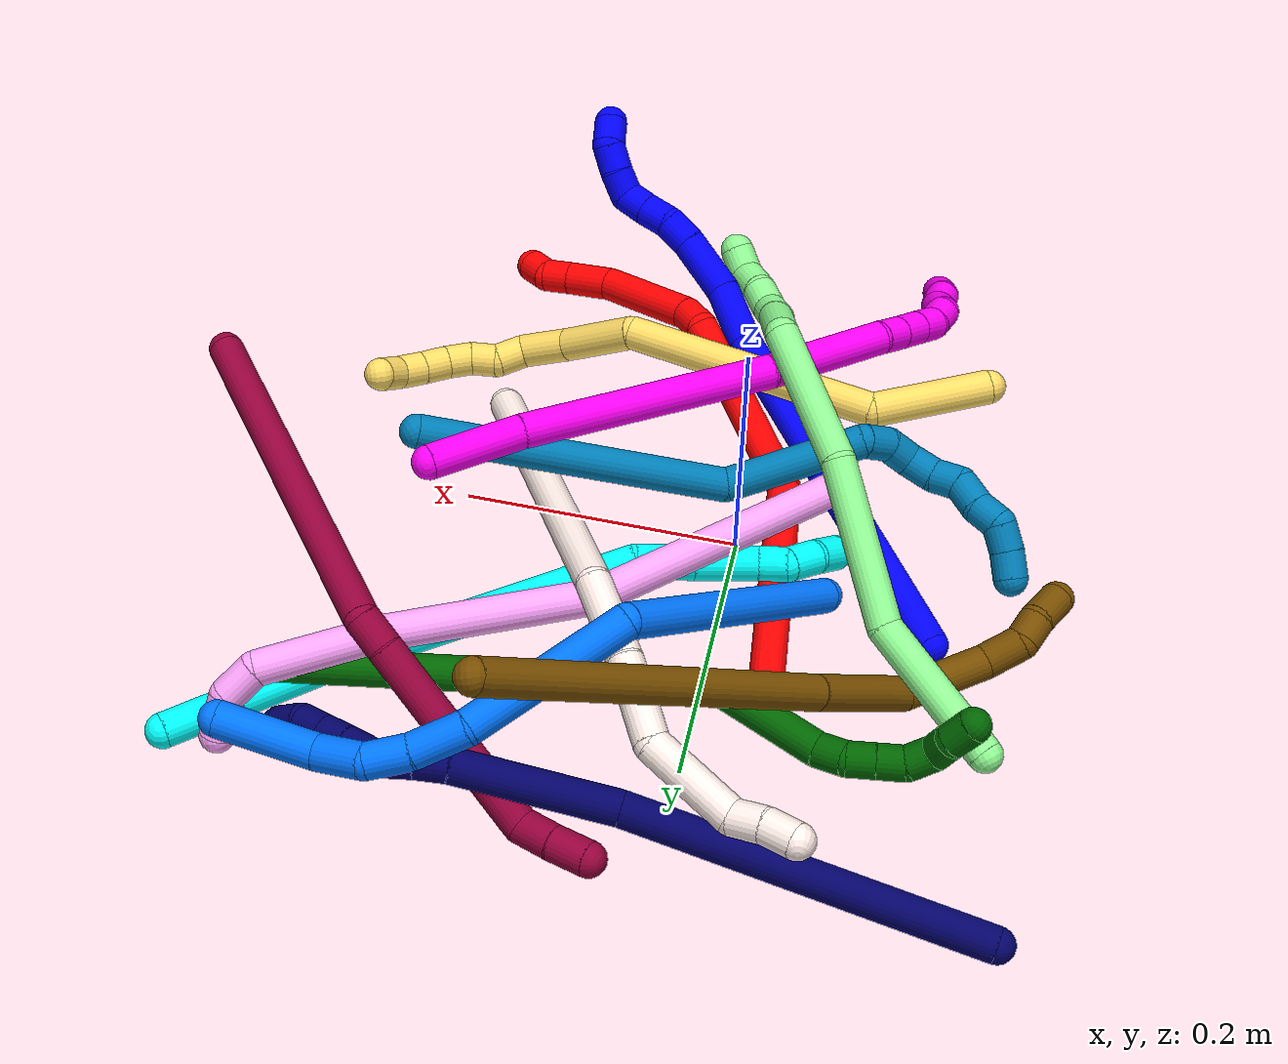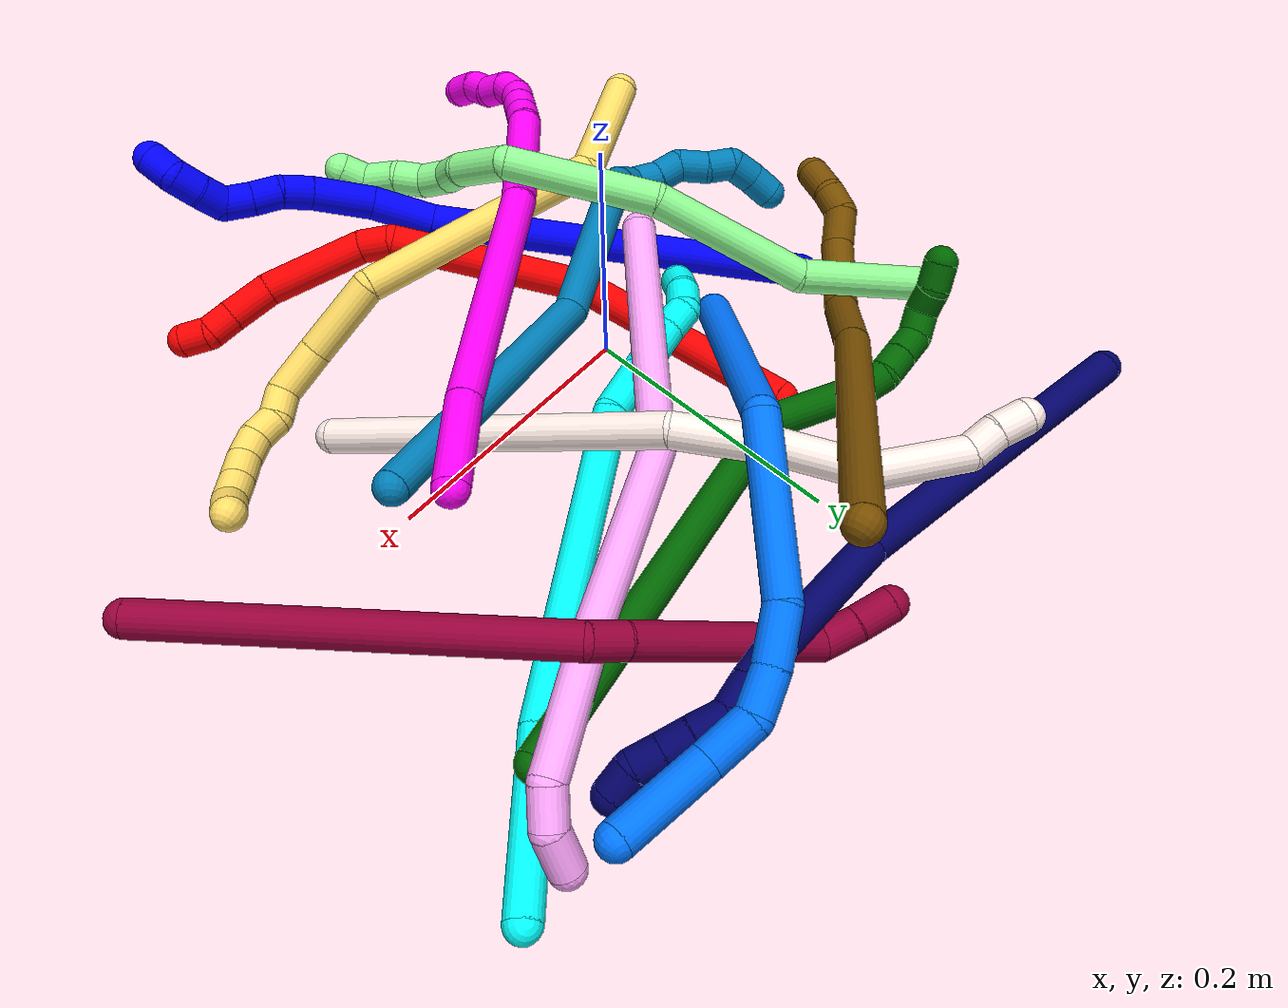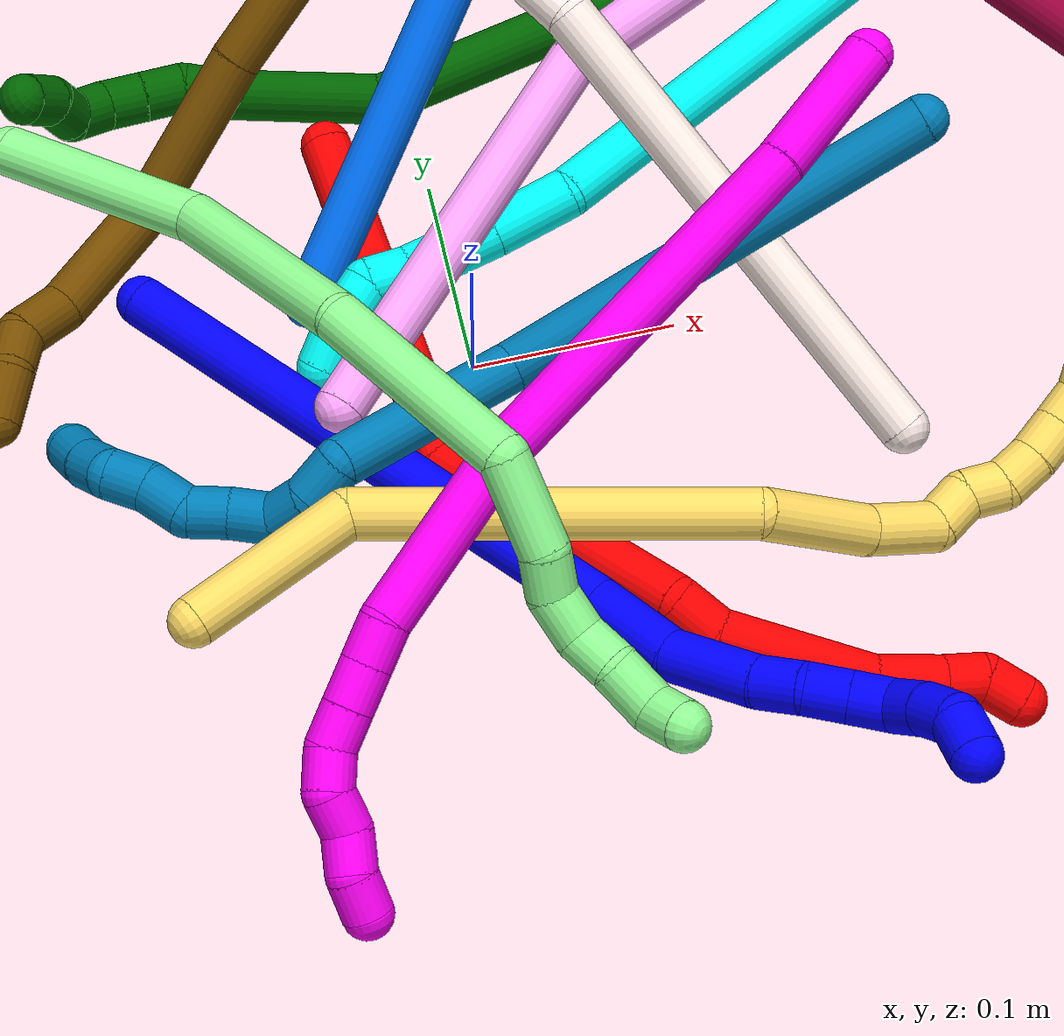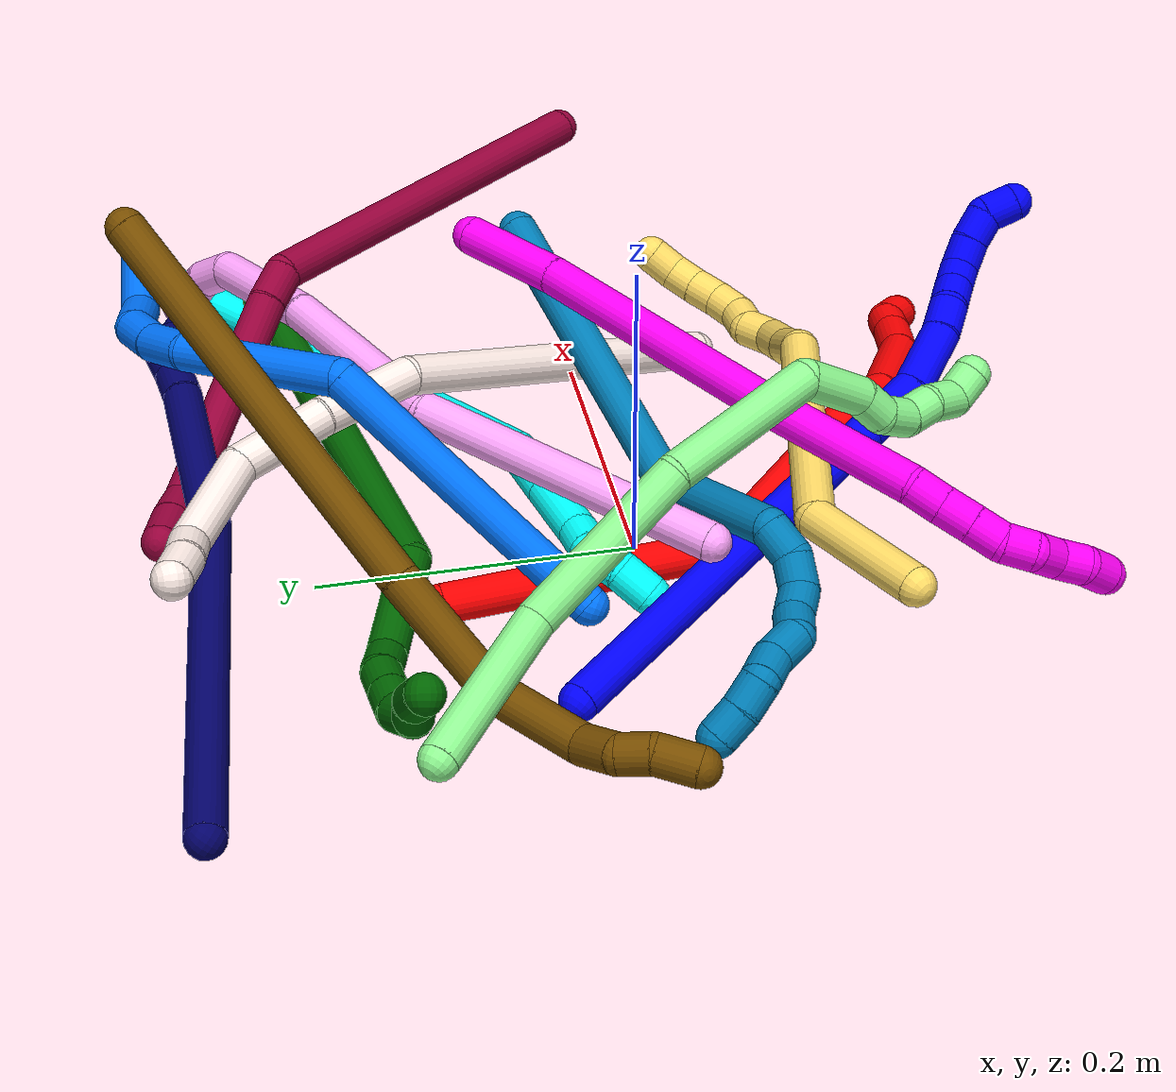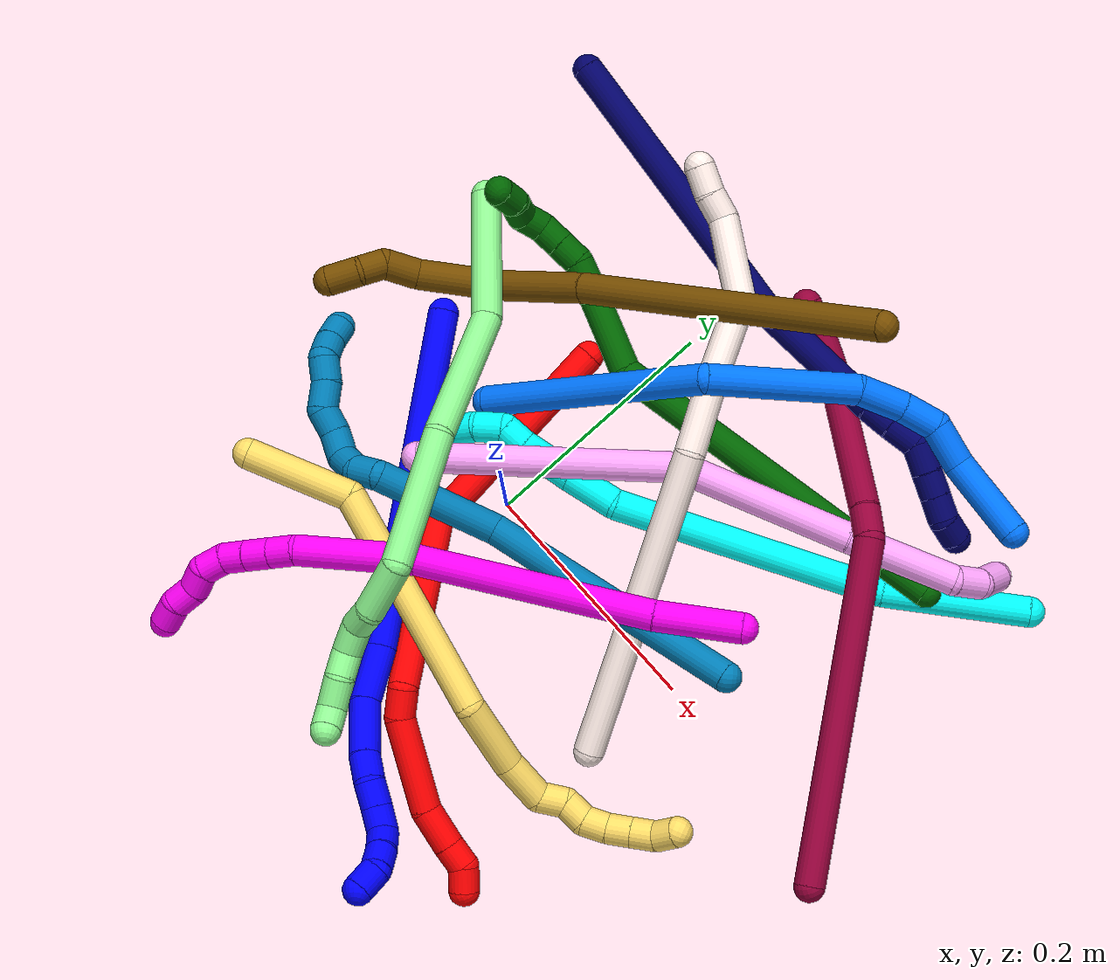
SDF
<sdf version="1.7">
 <world name="default">
  <plugin name="TubeGeneratorPlugin" filename="libtube_generator_plugin.so"/>
  <model name="photoneo_s_sensor">
   <static>1</static>
   <pose>0 0 2 1.57079 1.57079 3.14159</pose>
   <link name="link">
    <inertial><mass>0.1</mass></inertial>
    <sensor name="sensor" type="depth">
     <update_rate>30</update_rate>
     <camera>
      <horizontal_fov>1.22</horizontal_fov>
      <image><width>1920</width><height>1200</height><format>B8G8R8</format></image>
      <clip><near>0.1</near><far>4</far></clip>
      <depth_camera><output>points</output></depth_camera>
     </camera>
     <plugin name="camera_plugin" filename="libgazebo_ros_depth_camera.so">
      <baseline>0.2</baseline>
      <alwaysOn>1</alwaysOn>
      <updateRate>0.0</updateRate>
      <cameraName>camera_ir</cameraName>
      <imageTopicName>/camera/color/image_raw</imageTopicName>
      <cameraInfoTopicName>/camera/color/camera_info</cameraInfoTopicName>
      <depthImageTopicName>/camera/depth/image_raw</depthImageTopicName>
      <depthImageCameraInfoTopicName>/camera/depth/camera_info</depthImageCameraInfoTopicName>
      <pointCloudTopicName>/camera/depth/points</pointCloudTopicName>
      <frameName>fr_optical</frameName>
      <pointCloudCutoff>0.1</pointCloudCutoff>
      <pointCloudCutoffMax>2.0</pointCloudCutoffMax>
      <distortionK1>0</distortionK1>
      <distortionK2>0</distortionK2>
      <distortionK3>0</distortionK3>
      <distortionT1>0</distortionT1>
      <distortionT2>0</distortionT2>
      <CxPrime>0</CxPrime>
      <Cx>0</Cx>
      <Cy>0</Cy>
      <focalLength>0</focalLength>
      <hackBaseline>0</hackBaseline>
     </plugin>
    </sensor>
   </link>
  </model>
  <gravity>0 0 -9.8</gravity>
  <magnetic_field>6e-06 2.3e-05 -4.2e-05</magnetic_field>
  <atmosphere type="adiabatic"/>
  <physics name="default_physics" default="0" type="ode">
   <max_step_size>0.003</max_step_size>
   <real_time_factor>1</real_time_factor>
   <real_time_update_rate>1000</real_time_update_rate>
   <max_contacts>10000</max_contacts>
   <ode>
    <solver>
     <type>quick</type>
     <iters>100</iters>
     <sor>1.3</sor>
     <use_dynamic_moi_rescaling>0</use_dynamic_moi_rescaling>
    </solver>
    <constraints>
     <contact_max_correcting_vel>0</contact_max_correcting_vel>
     <contact_surface_layer>0.001</contact_surface_layer>
     <cfm>0</cfm>
     <erp>0.2</erp>
    </constraints>
   </ode>
  </physics>
  <scene><ambient>0.4 0.4 0.4 1</ambient><background>0.7 0.7 0.7 1</background><shadows>0</shadows></scene>
  <audio><device>default</device></audio>
  <spherical_coordinates>
   <surface_model>EARTH_WGS84</surface_model>
   <latitude_deg>0</latitude_deg>
   <longitude_deg>0</longitude_deg>
   <elevation>0</elevation>
   <heading_deg>0</heading_deg>
  </spherical_coordinates>
  <model name="bin">
   <static>1</static>
   <link name="bottom">
    <collision name="collision-bottom">
     <pose>0 0 -0.01 0 -0 0</pose>
     <geometry><box><size>0.8 0.6 0.02</size></box></geometry>
     <surface>
      <friction><ode><mu>100</mu><mu2>100</mu2></ode></friction>
      <contact><collide_bitmask>65535</collide_bitmask></contact>
     </surface>
    </collision>
   </link>
   <link name="west_wall">
    <collision name="collision-west_wall">
     <pose>-0.41 0 0.1 0 -0 0</pose>
     <geometry><box><size>0.02 0.6 0.2</size></box></geometry>
     <surface>
      <friction><ode><mu>100</mu><mu2>100</mu2></ode></friction>
      <contact><collide_bitmask>65535</collide_bitmask></contact>
     </surface>
    </collision>
   </link>
   <link name="east_wall">
    <collision name="collision-east_wall">
     <pose>0.41 0 0.1 0 -0 0</pose>
     <geometry><box><size>0.02 0.6 0.2</size></box></geometry>
     <surface>
      <friction><ode><mu>100</mu><mu2>100</mu2></ode></friction>
      <contact><collide_bitmask>65535</collide_bitmask></contact>
     </surface>
    </collision>
   </link>
   <link name="south_wall">
    <collision name="collision-south_wall">
     <pose>0 -0.31 0.1 0 -0 0</pose>
     <geometry><box><size>0.8 0.02 0.2</size></box></geometry>
     <surface>
      <friction><ode><mu>100</mu><mu2>100</mu2></ode></friction>
      <contact><collide_bitmask>65535</collide_bitmask></contact>
     </surface>
    </collision>
   </link>
   <link name="north_wall">
    <collision name="collision-north_wall">
     <pose>0 0.31 0.1 0 -0 0</pose>
     <geometry><box><size>0.8 0.02 0.2</size></box></geometry>
     <surface>
      <friction><ode><mu>100</mu><mu2>100</mu2></ode></friction>
      <contact><collide_bitmask>65535</collide_bitmask></contact>
     </surface>
    </collision>
   </link>
  </model>
  <model name="1">
   <static>0</static>
   <link name="1">
    <collision name="collision-cylinder-e_1_1_4">
     <pose>0.023128 -0.03682 0.134424 0.267354 0.164438 0.022163</pose>
     <geometry><cylinder><radius>0.0125</radius><length>0.282564</length></cylinder></geometry>
     <surface>
      <friction><ode><mu>1.16</mu><mu2>1.16</mu2><slip1>0</slip1><slip2>0</slip2></ode></friction>
      <contact><ode><kp>1e+06</kp><kd>1</kd><max_vel>0</max_vel><min_depth>0.001</min_depth></ode></contact>
     </surface>
    </collision>
    <visual name="visual-cylinder-e_1_1_4">
     <pose>0.023128 -0.03682 0.134424 0.267354 0.164438 0.022163</pose>
     <geometry><cylinder><radius>0.0125</radius><length>0.282564</length></cylinder></geometry>
     <material><ambient>0 0 1 1</ambient></material>
    </visual>
    <collision name="collision-cylinder-e_2_4_5">
     <pose>0.046409 -0.078474 0.291579 0.209531 0.00662 0.000696</pose>
     <geometry><cylinder><radius>0.0125</radius><length>0.046478</length></cylinder></geometry>
     <surface>
      <friction><ode><mu>1.16</mu><mu2>1.16</mu2><slip1>0</slip1><slip2>0</slip2></ode></friction>
      <contact><ode><kp>1e+06</kp><kd>1</kd><max_vel>0</max_vel><min_depth>0.001</min_depth></ode></contact>
     </surface>
    </collision>
    <visual name="visual-cylinder-e_2_4_5">
     <pose>0.046409 -0.078474 0.291579 0.209531 0.00662 0.000696</pose>
     <geometry><cylinder><radius>0.0125</radius><length>0.046478</length></cylinder></geometry>
     <material><ambient>0 0 1 1</ambient></material>
    </visual>
    <collision name="collision-cylinder-e_3_5_6">
     <pose>0.050072 -0.082521 0.337061 -0.034567 0.152958 -0.002649</pose>
     <geometry><cylinder><radius>0.0125</radius><length>0.046069</length></cylinder></geometry>
     <surface>
      <friction><ode><mu>1.16</mu><mu2>1.16</mu2><slip1>0</slip1><slip2>0</slip2></ode></friction>
      <contact><ode><kp>1e+06</kp><kd>1</kd><max_vel>0</max_vel><min_depth>0.001</min_depth></ode></contact>
     </surface>
    </collision>
    <visual name="visual-cylinder-e_3_5_6">
     <pose>0.050072 -0.082521 0.337061 -0.034567 0.152958 -0.002649</pose>
     <geometry><cylinder><radius>0.0125</radius><length>0.046069</length></cylinder></geometry>
     <material><ambient>0 0 1 1</ambient></material>
    </visual>
    <collision name="collision-cylinder-e_4_6_7">
     <pose>0.056644 -0.080062 0.370458 -0.155805 0.276864 -0.02175</pose>
     <geometry><cylinder><radius>0.0125</radius><length>0.022404</length></cylinder></geometry>
     <surface>
      <friction><ode><mu>1.16</mu><mu2>1.16</mu2><slip1>0</slip1><slip2>0</slip2></ode></friction>
      <contact><ode><kp>1e+06</kp><kd>1</kd><max_vel>0</max_vel><min_depth>0.001</min_depth></ode></contact>
     </surface>
    </collision>
    <visual name="visual-cylinder-e_4_6_7">
     <pose>0.056644 -0.080062 0.370458 -0.155805 0.276864 -0.02175</pose>
     <geometry><cylinder><radius>0.0125</radius><length>0.022404</length></cylinder></geometry>
     <material><ambient>0 0 1 1</ambient></material>
    </visual>
    <collision name="collision-cylinder-e_5_7_8">
     <pose>0.065253 -0.078531 0.389952 0.015848 0.55985 0.004556</pose>
     <geometry><cylinder><radius>0.0125</radius><length>0.02089</length></cylinder></geometry>
     <surface>
      <friction><ode><mu>1.16</mu><mu2>1.16</mu2><slip1>0</slip1><slip2>0</slip2></ode></friction>
      <contact><ode><kp>1e+06</kp><kd>1</kd><max_vel>0</max_vel><min_depth>0.001</min_depth></ode></contact>
     </surface>
    </collision>
    <visual name="visual-cylinder-e_5_7_8">
     <pose>0.065253 -0.078531 0.389952 0.015848 0.55985 0.004556</pose>
     <geometry><cylinder><radius>0.0125</radius><length>0.02089</length></cylinder></geometry>
     <material><ambient>0 0 1 1</ambient></material>
    </visual>
    <collision name="collision-cylinder-e_6_8_9">
     <pose>0.075595 -0.078548 0.407876 -0.013503 0.486107 -0.003348</pose>
     <geometry><cylinder><radius>0.0125</radius><length>0.02053</length></cylinder></geometry>
     <surface>
      <friction><ode><mu>1.16</mu><mu2>1.16</mu2><slip1>0</slip1><slip2>0</slip2></ode></friction>
      <contact><ode><kp>1e+06</kp><kd>1</kd><max_vel>0</max_vel><min_depth>0.001</min_depth></ode></contact>
     </surface>
    </collision>
    <visual name="visual-cylinder-e_6_8_9">
     <pose>0.075595 -0.078548 0.407876 -0.013503 0.486107 -0.003348</pose>
     <geometry><cylinder><radius>0.0125</radius><length>0.02053</length></cylinder></geometry>
     <material><ambient>0 0 1 1</ambient></material>
    </visual>
    <collision name="collision-cylinder-e_7_9_10">
     <pose>0.078544 -0.07525 0.426461 -0.322306 -0.182188 0.029697</pose>
     <geometry><cylinder><radius>0.0125</radius><length>0.02039</length></cylinder></geometry>
     <surface>
      <friction><ode><mu>1.16</mu><mu2>1.16</mu2><slip1>0</slip1><slip2>0</slip2></ode></friction>
      <contact><ode><kp>1e+06</kp><kd>1</kd><max_vel>0</max_vel><min_depth>0.001</min_depth></ode></contact>
     </surface>
    </collision>
    <visual name="visual-cylinder-e_7_9_10">
     <pose>0.078544 -0.07525 0.426461 -0.322306 -0.182188 0.029697</pose>
     <geometry><cylinder><radius>0.0125</radius><length>0.02039</length></cylinder></geometry>
     <material><ambient>0 0 1 1</ambient></material>
    </visual>
    <collision name="collision-cylinder-e_8_10_11">
     <pose>0.074348 -0.070443 0.4456 -0.167782 -0.235982 0.019935</pose>
     <geometry><cylinder><radius>0.0125</radius><length>0.02009</length></cylinder></geometry>
     <surface>
      <friction><ode><mu>1.16</mu><mu2>1.16</mu2><slip1>0</slip1><slip2>0</slip2></ode></friction>
      <contact><ode><kp>1e+06</kp><kd>1</kd><max_vel>0</max_vel><min_depth>0.001</min_depth></ode></contact>
     </surface>
    </collision>
    <visual name="visual-cylinder-e_8_10_11">
     <pose>0.074348 -0.070443 0.4456 -0.167782 -0.235982 0.019935</pose>
     <geometry><cylinder><radius>0.0125</radius><length>0.02009</length></cylinder></geometry>
     <material><ambient>0 0 1 1</ambient></material>
    </visual>
    <collision name="collision-cylinder-e_9_11_2">
     <pose>0.068472 -0.073118 0.463888 0.461504 -0.349812 -0.082984</pose>
     <geometry><cylinder><radius>0.0125</radius><length>0.020586</length></cylinder></geometry>
     <surface>
      <friction><ode><mu>1.16</mu><mu2>1.16</mu2><slip1>0</slip1><slip2>0</slip2></ode></friction>
      <contact><ode><kp>1e+06</kp><kd>1</kd><max_vel>0</max_vel><min_depth>0.001</min_depth></ode></contact>
     </surface>
    </collision>
    <visual name="visual-cylinder-e_9_11_2">
     <pose>0.068472 -0.073118 0.463888 0.461504 -0.349812 -0.082984</pose>
     <geometry><cylinder><radius>0.0125</radius><length>0.020586</length></cylinder></geometry>
     <material><ambient>0 0 1 1</ambient></material>
    </visual>
    <collision name="collision-sphere-2">
     <pose>0.064944 -0.077424 0.472546 0 -0 0</pose>
     <geometry><sphere><radius>0.0125</radius></sphere></geometry>
     <surface>
      <friction><ode><mu>1.16</mu><mu2>1.16</mu2><slip1>0</slip1><slip2>0</slip2></ode></friction>
      <contact><ode><kp>1e+06</kp><kd>1</kd><max_vel>0</max_vel><min_depth>0.001</min_depth></ode></contact>
     </surface>
    </collision>
    <visual name="visual-sphere-2">
     <pose>0.064944 -0.077424 0.472546 0 -0 0</pose>
     <geometry><sphere><radius>0.0125</radius></sphere></geometry>
     <material><ambient>0 0 1 1</ambient></material>
    </visual>
    <collision name="collision-sphere-11">
     <pose>0.072 -0.068812 0.45523 0 -0 0</pose>
     <geometry><sphere><radius>0.0125</radius></sphere></geometry>
     <surface>
      <friction><ode><mu>1.16</mu><mu2>1.16</mu2><slip1>0</slip1><slip2>0</slip2></ode></friction>
      <contact><ode><kp>1e+06</kp><kd>1</kd><max_vel>0</max_vel><min_depth>0.001</min_depth></ode></contact>
     </surface>
    </collision>
    <visual name="visual-sphere-11">
     <pose>0.072 -0.068812 0.45523 0 -0 0</pose>
     <geometry><sphere><radius>0.0125</radius></sphere></geometry>
     <material><ambient>0 0 1 1</ambient></material>
    </visual>
    <collision name="collision-sphere-10">
     <pose>0.076697 -0.072074 0.435971 0 -0 0</pose>
     <geometry><sphere><radius>0.0125</radius></sphere></geometry>
     <surface>
      <friction><ode><mu>1.16</mu><mu2>1.16</mu2><slip1>0</slip1><slip2>0</slip2></ode></friction>
      <contact><ode><kp>1e+06</kp><kd>1</kd><max_vel>0</max_vel><min_depth>0.001</min_depth></ode></contact>
     </surface>
    </collision>
    <visual name="visual-sphere-10">
     <pose>0.076697 -0.072074 0.435971 0 -0 0</pose>
     <geometry><sphere><radius>0.0125</radius></sphere></geometry>
     <material><ambient>0 0 1 1</ambient></material>
    </visual>
    <collision name="collision-sphere-9">
     <pose>0.080391 -0.078426 0.416951 0 -0 0</pose>
     <geometry><sphere><radius>0.0125</radius></sphere></geometry>
     <surface>
      <friction><ode><mu>1.16</mu><mu2>1.16</mu2><slip1>0</slip1><slip2>0</slip2></ode></friction>
      <contact><ode><kp>1e+06</kp><kd>1</kd><max_vel>0</max_vel><min_depth>0.001</min_depth></ode></contact>
     </surface>
    </collision>
    <visual name="visual-sphere-9">
     <pose>0.080391 -0.078426 0.416951 0 -0 0</pose>
     <geometry><sphere><radius>0.0125</radius></sphere></geometry>
     <material><ambient>0 0 1 1</ambient></material>
    </visual>
    <collision name="collision-sphere-4">
     <pose>0.046255 -0.073641 0.268849 0 -0 0</pose>
     <geometry><sphere><radius>0.0125</radius></sphere></geometry>
     <surface>
      <friction><ode><mu>1.16</mu><mu2>1.16</mu2><slip1>0</slip1><slip2>0</slip2></ode></friction>
      <contact><ode><kp>1e+06</kp><kd>1</kd><max_vel>0</max_vel><min_depth>0.001</min_depth></ode></contact>
     </surface>
    </collision>
    <visual name="visual-sphere-4">
     <pose>0.046255 -0.073641 0.268849 0 -0 0</pose>
     <geometry><sphere><radius>0.0125</radius></sphere></geometry>
     <material><ambient>0 0 1 1</ambient></material>
    </visual>
    <collision name="collision-sphere-1">
     <geometry><sphere><radius>0.0125</radius></sphere></geometry>
     <surface>
      <friction><ode><mu>1.16</mu><mu2>1.16</mu2><slip1>0</slip1><slip2>0</slip2></ode></friction>
      <contact><ode><kp>1e+06</kp><kd>1</kd><max_vel>0</max_vel><min_depth>0.001</min_depth></ode></contact>
     </surface>
    </collision>
    <visual name="visual-sphere-1">
     <geometry><sphere><radius>0.0125</radius></sphere></geometry>
     <material><ambient>0 0 1 1</ambient></material>
    </visual>
    <collision name="collision-sphere-8">
     <pose>0.0708 -0.078671 0.398801 0 -0 0</pose>
     <geometry><sphere><radius>0.0125</radius></sphere></geometry>
     <surface>
      <friction><ode><mu>1.16</mu><mu2>1.16</mu2><slip1>0</slip1><slip2>0</slip2></ode></friction>
      <contact><ode><kp>1e+06</kp><kd>1</kd><max_vel>0</max_vel><min_depth>0.001</min_depth></ode></contact>
     </surface>
    </collision>
    <visual name="visual-sphere-8">
     <pose>0.0708 -0.078671 0.398801 0 -0 0</pose>
     <geometry><sphere><radius>0.0125</radius></sphere></geometry>
     <material><ambient>0 0 1 1</ambient></material>
    </visual>
    <collision name="collision-sphere-5">
     <pose>0.046563 -0.083308 0.314309 0 -0 0</pose>
     <geometry><sphere><radius>0.0125</radius></sphere></geometry>
     <surface>
      <friction><ode><mu>1.16</mu><mu2>1.16</mu2><slip1>0</slip1><slip2>0</slip2></ode></friction>
      <contact><ode><kp>1e+06</kp><kd>1</kd><max_vel>0</max_vel><min_depth>0.001</min_depth></ode></contact>
     </surface>
    </collision>
    <visual name="visual-sphere-5">
     <pose>0.046563 -0.083308 0.314309 0 -0 0</pose>
     <geometry><sphere><radius>0.0125</radius></sphere></geometry>
     <material><ambient>0 0 1 1</ambient></material>
    </visual>
    <collision name="collision-sphere-6">
     <pose>0.053582 -0.081735 0.359813 0 -0 0</pose>
     <geometry><sphere><radius>0.0125</radius></sphere></geometry>
     <surface>
      <friction><ode><mu>1.16</mu><mu2>1.16</mu2><slip1>0</slip1><slip2>0</slip2></ode></friction>
      <contact><ode><kp>1e+06</kp><kd>1</kd><max_vel>0</max_vel><min_depth>0.001</min_depth></ode></contact>
     </surface>
    </collision>
    <visual name="visual-sphere-6">
     <pose>0.053582 -0.081735 0.359813 0 -0 0</pose>
     <geometry><sphere><radius>0.0125</radius></sphere></geometry>
     <material><ambient>0 0 1 1</ambient></material>
    </visual>
    <collision name="collision-sphere-7">
     <pose>0.059706 -0.07839 0.381103 0 -0 0</pose>
     <geometry><sphere><radius>0.0125</radius></sphere></geometry>
     <surface>
      <friction><ode><mu>1.16</mu><mu2>1.16</mu2><slip1>0</slip1><slip2>0</slip2></ode></friction>
      <contact><ode><kp>1e+06</kp><kd>1</kd><max_vel>0</max_vel><min_depth>0.001</min_depth></ode></contact>
     </surface>
    </collision>
    <visual name="visual-sphere-7">
     <pose>0.059706 -0.07839 0.381103 0 -0 0</pose>
     <geometry><sphere><radius>0.0125</radius></sphere></geometry>
     <material><ambient>0 0 1 1</ambient></material>
    </visual>
    <inertial>
     <pose>0.039375 -0.054709 0.23816 0 -0 0</pose>
     <mass>0.5</mass>
     <inertia>
      <ixx>0.00194</ixx>
      <ixy>0</ixy>
      <ixz>0</ixz>
      <iyy>0.001889</iyy>
      <iyz>0</iyz>
      <izz>0.000219</izz>
     </inertia>
    </inertial>
   </link>
   <pose>-0.150514 0.065092 0.011465 1.01077 0.630585 0.368362</pose>
  </model>
  <model name="2">
   <static>0</static>
   <link name="2">
    <collision name="collision-cylinder-e_1_1_4">
     <pose>-0.002847 -0.031276 0.084442 0.35472 -0.031606 -0.005666</pose>
     <geometry><cylinder><radius>0.0125</radius><length>0.180187</length></cylinder></geometry>
     <surface>
      <friction><ode><mu>1.16</mu><mu2>1.16</mu2><slip1>0</slip1><slip2>0</slip2></ode></friction>
      <contact><ode><kp>1e+06</kp><kd>1</kd><max_vel>0</max_vel><min_depth>0.001</min_depth></ode></contact>
     </surface>
    </collision>
    <visual name="visual-cylinder-e_1_1_4">
     <pose>-0.002847 -0.031276 0.084442 0.35472 -0.031606 -0.005666</pose>
     <geometry><cylinder><radius>0.0125</radius><length>0.180187</length></cylinder></geometry>
     <material><ambient>1 0 0 1</ambient></material>
    </visual>
    <collision name="collision-cylinder-e_2_4_5">
     <pose>0.033742 -0.086785 0.22478 0.409065 0.574491 0.122405</pose>
     <geometry><cylinder><radius>0.0125</radius><length>0.145144</length></cylinder></geometry>
     <surface>
      <friction><ode><mu>1.16</mu><mu2>1.16</mu2><slip1>0</slip1><slip2>0</slip2></ode></friction>
      <contact><ode><kp>1e+06</kp><kd>1</kd><max_vel>0</max_vel><min_depth>0.001</min_depth></ode></contact>
     </surface>
    </collision>
    <visual name="visual-cylinder-e_2_4_5">
     <pose>0.033742 -0.086785 0.22478 0.409065 0.574491 0.122405</pose>
     <geometry><cylinder><radius>0.0125</radius><length>0.145144</length></cylinder></geometry>
     <material><ambient>1 0 0 1</ambient></material>
    </visual>
    <collision name="collision-cylinder-e_3_5_6">
     <pose>0.076863 -0.120195 0.287661 0.920283 0.30924 0.154194</pose>
     <geometry><cylinder><radius>0.0125</radius><length>0.024216</length></cylinder></geometry>
     <surface>
      <friction><ode><mu>1.16</mu><mu2>1.16</mu2><slip1>0</slip1><slip2>0</slip2></ode></friction>
      <contact><ode><kp>1e+06</kp><kd>1</kd><max_vel>0</max_vel><min_depth>0.001</min_depth></ode></contact>
     </surface>
    </collision>
    <visual name="visual-cylinder-e_3_5_6">
     <pose>0.076863 -0.120195 0.287661 0.920283 0.30924 0.154194</pose>
     <geometry><cylinder><radius>0.0125</radius><length>0.024216</length></cylinder></geometry>
     <material><ambient>1 0 0 1</ambient></material>
    </visual>
    <collision name="collision-cylinder-e_4_6_7">
     <pose>0.102477 -0.1587 0.305648 1.21189 0.610781 0.43012</pose>
     <geometry><cylinder><radius>0.0125</radius><length>0.076473</length></cylinder></geometry>
     <surface>
      <friction><ode><mu>1.16</mu><mu2>1.16</mu2><slip1>0</slip1><slip2>0</slip2></ode></friction>
      <contact><ode><kp>1e+06</kp><kd>1</kd><max_vel>0</max_vel><min_depth>0.001</min_depth></ode></contact>
     </surface>
    </collision>
    <visual name="visual-cylinder-e_4_6_7">
     <pose>0.102477 -0.1587 0.305648 1.21189 0.610781 0.43012</pose>
     <geometry><cylinder><radius>0.0125</radius><length>0.076473</length></cylinder></geometry>
     <material><ambient>1 0 0 1</ambient></material>
    </visual>
    <collision name="collision-cylinder-e_5_7_8">
     <pose>0.13611 -0.200004 0.317248 1.52089 0.773272 0.739023</pose>
     <geometry><cylinder><radius>0.0125</radius><length>0.033512</length></cylinder></geometry>
     <surface>
      <friction><ode><mu>1.16</mu><mu2>1.16</mu2><slip1>0</slip1><slip2>0</slip2></ode></friction>
      <contact><ode><kp>1e+06</kp><kd>1</kd><max_vel>0</max_vel><min_depth>0.001</min_depth></ode></contact>
     </surface>
    </collision>
    <visual name="visual-cylinder-e_5_7_8">
     <pose>0.13611 -0.200004 0.317248 1.52089 0.773272 0.739023</pose>
     <geometry><cylinder><radius>0.0125</radius><length>0.033512</length></cylinder></geometry>
     <material><ambient>1 0 0 1</ambient></material>
    </visual>
    <collision name="collision-cylinder-e_6_8_9">
     <pose>0.155246 -0.218919 0.317722 1.5887 0.819647 0.832816</pose>
     <geometry><cylinder><radius>0.0125</radius><length>0.020338</length></cylinder></geometry>
     <surface>
      <friction><ode><mu>1.16</mu><mu2>1.16</mu2><slip1>0</slip1><slip2>0</slip2></ode></friction>
      <contact><ode><kp>1e+06</kp><kd>1</kd><max_vel>0</max_vel><min_depth>0.001</min_depth></ode></contact>
     </surface>
    </collision>
    <visual name="visual-cylinder-e_6_8_9">
     <pose>0.155246 -0.218919 0.317722 1.5887 0.819647 0.832816</pose>
     <geometry><cylinder><radius>0.0125</radius><length>0.020338</length></cylinder></geometry>
     <material><ambient>1 0 0 1</ambient></material>
    </visual>
    <collision name="collision-cylinder-e_7_9_2">
     <pose>0.166841 -0.233716 0.322312 1.03048 0.426378 0.243947</pose>
     <geometry><cylinder><radius>0.0125</radius><length>0.02013</length></cylinder></geometry>
     <surface>
      <friction><ode><mu>1.16</mu><mu2>1.16</mu2><slip1>0</slip1><slip2>0</slip2></ode></friction>
      <contact><ode><kp>1e+06</kp><kd>1</kd><max_vel>0</max_vel><min_depth>0.001</min_depth></ode></contact>
     </surface>
    </collision>
    <visual name="visual-cylinder-e_7_9_2">
     <pose>0.166841 -0.233716 0.322312 1.03048 0.426378 0.243947</pose>
     <geometry><cylinder><radius>0.0125</radius><length>0.02013</length></cylinder></geometry>
     <material><ambient>1 0 0 1</ambient></material>
    </visual>
    <collision name="collision-sphere-2">
     <pose>0.171004 -0.241575 0.327026 0 -0 0</pose>
     <geometry><sphere><radius>0.0125</radius></sphere></geometry>
     <surface>
      <friction><ode><mu>1.16</mu><mu2>1.16</mu2><slip1>0</slip1><slip2>0</slip2></ode></friction>
      <contact><ode><kp>1e+06</kp><kd>1</kd><max_vel>0</max_vel><min_depth>0.001</min_depth></ode></contact>
     </surface>
    </collision>
    <visual name="visual-sphere-2">
     <pose>0.171004 -0.241575 0.327026 0 -0 0</pose>
     <geometry><sphere><radius>0.0125</radius></sphere></geometry>
     <material><ambient>1 0 0 1</ambient></material>
    </visual>
    <collision name="collision-sphere-9">
     <pose>0.162679 -0.225858 0.317598 0 -0 0</pose>
     <geometry><sphere><radius>0.0125</radius></sphere></geometry>
     <surface>
      <friction><ode><mu>1.16</mu><mu2>1.16</mu2><slip1>0</slip1><slip2>0</slip2></ode></friction>
      <contact><ode><kp>1e+06</kp><kd>1</kd><max_vel>0</max_vel><min_depth>0.001</min_depth></ode></contact>
     </surface>
    </collision>
    <visual name="visual-sphere-9">
     <pose>0.162679 -0.225858 0.317598 0 -0 0</pose>
     <geometry><sphere><radius>0.0125</radius></sphere></geometry>
     <material><ambient>1 0 0 1</ambient></material>
    </visual>
    <collision name="collision-sphere-4">
     <pose>-0.005694 -0.062553 0.168885 0 -0 0</pose>
     <geometry><sphere><radius>0.0125</radius></sphere></geometry>
     <surface>
      <friction><ode><mu>1.16</mu><mu2>1.16</mu2><slip1>0</slip1><slip2>0</slip2></ode></friction>
      <contact><ode><kp>1e+06</kp><kd>1</kd><max_vel>0</max_vel><min_depth>0.001</min_depth></ode></contact>
     </surface>
    </collision>
    <visual name="visual-sphere-4">
     <pose>-0.005694 -0.062553 0.168885 0 -0 0</pose>
     <geometry><sphere><radius>0.0125</radius></sphere></geometry>
     <material><ambient>1 0 0 1</ambient></material>
    </visual>
    <collision name="collision-sphere-1">
     <geometry><sphere><radius>0.0125</radius></sphere></geometry>
     <surface>
      <friction><ode><mu>1.16</mu><mu2>1.16</mu2><slip1>0</slip1><slip2>0</slip2></ode></friction>
      <contact><ode><kp>1e+06</kp><kd>1</kd><max_vel>0</max_vel><min_depth>0.001</min_depth></ode></contact>
     </surface>
    </collision>
    <visual name="visual-sphere-1">
     <geometry><sphere><radius>0.0125</radius></sphere></geometry>
     <material><ambient>1 0 0 1</ambient></material>
    </visual>
    <collision name="collision-sphere-8">
     <pose>0.147813 -0.21198 0.317846 0 -0 0</pose>
     <geometry><sphere><radius>0.0125</radius></sphere></geometry>
     <surface>
      <friction><ode><mu>1.16</mu><mu2>1.16</mu2><slip1>0</slip1><slip2>0</slip2></ode></friction>
      <contact><ode><kp>1e+06</kp><kd>1</kd><max_vel>0</max_vel><min_depth>0.001</min_depth></ode></contact>
     </surface>
    </collision>
    <visual name="visual-sphere-8">
     <pose>0.147813 -0.21198 0.317846 0 -0 0</pose>
     <geometry><sphere><radius>0.0125</radius></sphere></geometry>
     <material><ambient>1 0 0 1</ambient></material>
    </visual>
    <collision name="collision-sphere-5">
     <pose>0.073179 -0.111016 0.280676 0 -0 0</pose>
     <geometry><sphere><radius>0.0125</radius></sphere></geometry>
     <surface>
      <friction><ode><mu>1.16</mu><mu2>1.16</mu2><slip1>0</slip1><slip2>0</slip2></ode></friction>
      <contact><ode><kp>1e+06</kp><kd>1</kd><max_vel>0</max_vel><min_depth>0.001</min_depth></ode></contact>
     </surface>
    </collision>
    <visual name="visual-sphere-5">
     <pose>0.073179 -0.111016 0.280676 0 -0 0</pose>
     <geometry><sphere><radius>0.0125</radius></sphere></geometry>
     <material><ambient>1 0 0 1</ambient></material>
    </visual>
    <collision name="collision-sphere-6">
     <pose>0.080548 -0.129373 0.294645 0 -0 0</pose>
     <geometry><sphere><radius>0.0125</radius></sphere></geometry>
     <surface>
      <friction><ode><mu>1.16</mu><mu2>1.16</mu2><slip1>0</slip1><slip2>0</slip2></ode></friction>
      <contact><ode><kp>1e+06</kp><kd>1</kd><max_vel>0</max_vel><min_depth>0.001</min_depth></ode></contact>
     </surface>
    </collision>
    <visual name="visual-sphere-6">
     <pose>0.080548 -0.129373 0.294645 0 -0 0</pose>
     <geometry><sphere><radius>0.0125</radius></sphere></geometry>
     <material><ambient>1 0 0 1</ambient></material>
    </visual>
    <collision name="collision-sphere-7">
     <pose>0.124406 -0.188027 0.31665 0 -0 0</pose>
     <geometry><sphere><radius>0.0125</radius></sphere></geometry>
     <surface>
      <friction><ode><mu>1.16</mu><mu2>1.16</mu2><slip1>0</slip1><slip2>0</slip2></ode></friction>
      <contact><ode><kp>1e+06</kp><kd>1</kd><max_vel>0</max_vel><min_depth>0.001</min_depth></ode></contact>
     </surface>
    </collision>
    <visual name="visual-sphere-7">
     <pose>0.124406 -0.188027 0.31665 0 -0 0</pose>
     <geometry><sphere><radius>0.0125</radius></sphere></geometry>
     <material><ambient>1 0 0 1</ambient></material>
    </visual>
    <inertial>
     <pose>0.05032 -0.098277 0.203525 0 -0 0</pose>
     <mass>0.5</mass>
     <inertia>
      <ixx>0.000802</ixx>
      <ixy>0</ixy>
      <ixz>0</ixz>
      <iyy>0.000757</iyy>
      <iyz>0</iyz>
      <izz>0.000168</izz>
     </inertia>
    </inertial>
   </link>
   <pose>-0.045662 0.129153 0.011456 1.19397 -0.552429 0.145218</pose>
  </model>
  <model name="3">
   <static>0</static>
   <link name="3">
    <collision name="collision-cylinder-e_1_1_4">
     <pose>-0.055306 -0.019465 0.011481 1.03789 -1.18288 -0.732614</pose>
     <geometry><cylinder><radius>0.0125</radius><length>0.119491</length></cylinder></geometry>
     <surface>
      <friction><ode><mu>1.16</mu><mu2>1.16</mu2><slip1>0</slip1><slip2>0</slip2></ode></friction>
      <contact><ode><kp>1e+06</kp><kd>1</kd><max_vel>0</max_vel><min_depth>0.001</min_depth></ode></contact>
     </surface>
    </collision>
    <visual name="visual-cylinder-e_1_1_4">
     <pose>-0.055306 -0.019465 0.011481 1.03789 -1.18288 -0.732614</pose>
     <geometry><cylinder><radius>0.0125</radius><length>0.119491</length></cylinder></geometry>
     <material><ambient>0.003922 1 0.996078 1</ambient></material>
    </visual>
    <collision name="collision-cylinder-e_2_4_5">
     <pose>-0.212458 -0.088135 0.023857 1.55261 -1.12068 -1.10437</pose>
     <geometry><cylinder><radius>0.0125</radius><length>0.226224</length></cylinder></geometry>
     <surface>
      <friction><ode><mu>1.16</mu><mu2>1.16</mu2><slip1>0</slip1><slip2>0</slip2></ode></friction>
      <contact><ode><kp>1e+06</kp><kd>1</kd><max_vel>0</max_vel><min_depth>0.001</min_depth></ode></contact>
     </surface>
    </collision>
    <visual name="visual-cylinder-e_2_4_5">
     <pose>-0.212458 -0.088135 0.023857 1.55261 -1.12068 -1.10437</pose>
     <geometry><cylinder><radius>0.0125</radius><length>0.226224</length></cylinder></geometry>
     <material><ambient>0.003922 1 0.996078 1</ambient></material>
    </visual>
    <collision name="collision-cylinder-e_3_5_6">
     <pose>-0.328895 -0.151794 0.027335 1.39394 -0.78222 -0.664769</pose>
     <geometry><cylinder><radius>0.0125</radius><length>0.041403</length></cylinder></geometry>
     <surface>
      <friction><ode><mu>1.16</mu><mu2>1.16</mu2><slip1>0</slip1><slip2>0</slip2></ode></friction>
      <contact><ode><kp>1e+06</kp><kd>1</kd><max_vel>0</max_vel><min_depth>0.001</min_depth></ode></contact>
     </surface>
    </collision>
    <visual name="visual-cylinder-e_3_5_6">
     <pose>-0.328895 -0.151794 0.027335 1.39394 -0.78222 -0.664769</pose>
     <geometry><cylinder><radius>0.0125</radius><length>0.041403</length></cylinder></geometry>
     <material><ambient>0.003922 1 0.996078 1</ambient></material>
    </visual>
    <collision name="collision-cylinder-e_4_6_7">
     <pose>-0.35961 -0.182221 0.031073 1.49867 -0.788817 -0.738898</pose>
     <geometry><cylinder><radius>0.0125</radius><length>0.045449</length></cylinder></geometry>
     <surface>
      <friction><ode><mu>1.16</mu><mu2>1.16</mu2><slip1>0</slip1><slip2>0</slip2></ode></friction>
      <contact><ode><kp>1e+06</kp><kd>1</kd><max_vel>0</max_vel><min_depth>0.001</min_depth></ode></contact>
     </surface>
    </collision>
    <visual name="visual-cylinder-e_4_6_7">
     <pose>-0.35961 -0.182221 0.031073 1.49867 -0.788817 -0.738898</pose>
     <geometry><cylinder><radius>0.0125</radius><length>0.045449</length></cylinder></geometry>
     <material><ambient>0.003922 1 0.996078 1</ambient></material>
    </visual>
    <collision name="collision-cylinder-e_5_7_8">
     <pose>-0.382555 -0.206079 0.031429 1.67161 -0.710628 -0.779034</pose>
     <geometry><cylinder><radius>0.0125</radius><length>0.020914</length></cylinder></geometry>
     <surface>
      <friction><ode><mu>1.16</mu><mu2>1.16</mu2><slip1>0</slip1><slip2>0</slip2></ode></friction>
      <contact><ode><kp>1e+06</kp><kd>1</kd><max_vel>0</max_vel><min_depth>0.001</min_depth></ode></contact>
     </surface>
    </collision>
    <visual name="visual-cylinder-e_5_7_8">
     <pose>-0.382555 -0.206079 0.031429 1.67161 -0.710628 -0.779034</pose>
     <geometry><cylinder><radius>0.0125</radius><length>0.020914</length></cylinder></geometry>
     <material><ambient>0.003922 1 0.996078 1</ambient></material>
    </visual>
    <collision name="collision-cylinder-e_6_8_9">
     <pose>-0.399326 -0.217878 0.035571 0.670024 -1.00622 -0.3786</pose>
     <geometry><cylinder><radius>0.0125</radius><length>0.023555</length></cylinder></geometry>
     <surface>
      <friction><ode><mu>1.16</mu><mu2>1.16</mu2><slip1>0</slip1><slip2>0</slip2></ode></friction>
      <contact><ode><kp>1e+06</kp><kd>1</kd><max_vel>0</max_vel><min_depth>0.001</min_depth></ode></contact>
     </surface>
    </collision>
    <visual name="visual-cylinder-e_6_8_9">
     <pose>-0.399326 -0.217878 0.035571 0.670024 -1.00622 -0.3786</pose>
     <geometry><cylinder><radius>0.0125</radius><length>0.023555</length></cylinder></geometry>
     <material><ambient>0.003922 1 0.996078 1</ambient></material>
    </visual>
    <collision name="collision-cylinder-e_7_9_2">
     <pose>-0.417426 -0.224639 0.04808 0.359798 -0.789269 -0.151199</pose>
     <geometry><cylinder><radius>0.0125</radius><length>0.022964</length></cylinder></geometry>
     <surface>
      <friction><ode><mu>1.16</mu><mu2>1.16</mu2><slip1>0</slip1><slip2>0</slip2></ode></friction>
      <contact><ode><kp>1e+06</kp><kd>1</kd><max_vel>0</max_vel><min_depth>0.001</min_depth></ode></contact>
     </surface>
    </collision>
    <visual name="visual-cylinder-e_7_9_2">
     <pose>-0.417426 -0.224639 0.04808 0.359798 -0.789269 -0.151199</pose>
     <geometry><cylinder><radius>0.0125</radius><length>0.022964</length></cylinder></geometry>
     <material><ambient>0.003922 1 0.996078 1</ambient></material>
    </visual>
    <collision name="collision-sphere-2">
     <pose>-0.425577 -0.227486 0.05565 0 -0 0</pose>
     <geometry><sphere><radius>0.0125</radius></sphere></geometry>
     <surface>
      <friction><ode><mu>1.16</mu><mu2>1.16</mu2><slip1>0</slip1><slip2>0</slip2></ode></friction>
      <contact><ode><kp>1e+06</kp><kd>1</kd><max_vel>0</max_vel><min_depth>0.001</min_depth></ode></contact>
     </surface>
    </collision>
    <visual name="visual-sphere-2">
     <pose>-0.425577 -0.227486 0.05565 0 -0 0</pose>
     <geometry><sphere><radius>0.0125</radius></sphere></geometry>
     <material><ambient>0.003922 1 0.996078 1</ambient></material>
    </visual>
    <collision name="collision-sphere-9">
     <pose>-0.409276 -0.221791 0.04051 0 -0 0</pose>
     <geometry><sphere><radius>0.0125</radius></sphere></geometry>
     <surface>
      <friction><ode><mu>1.16</mu><mu2>1.16</mu2><slip1>0</slip1><slip2>0</slip2></ode></friction>
      <contact><ode><kp>1e+06</kp><kd>1</kd><max_vel>0</max_vel><min_depth>0.001</min_depth></ode></contact>
     </surface>
    </collision>
    <visual name="visual-sphere-9">
     <pose>-0.409276 -0.221791 0.04051 0 -0 0</pose>
     <geometry><sphere><radius>0.0125</radius></sphere></geometry>
     <material><ambient>0.003922 1 0.996078 1</ambient></material>
    </visual>
    <collision name="collision-sphere-4">
     <pose>-0.110613 -0.038931 0.022962 0 -0 0</pose>
     <geometry><sphere><radius>0.0125</radius></sphere></geometry>
     <surface>
      <friction><ode><mu>1.16</mu><mu2>1.16</mu2><slip1>0</slip1><slip2>0</slip2></ode></friction>
      <contact><ode><kp>1e+06</kp><kd>1</kd><max_vel>0</max_vel><min_depth>0.001</min_depth></ode></contact>
     </surface>
    </collision>
    <visual name="visual-sphere-4">
     <pose>-0.110613 -0.038931 0.022962 0 -0 0</pose>
     <geometry><sphere><radius>0.0125</radius></sphere></geometry>
     <material><ambient>0.003922 1 0.996078 1</ambient></material>
    </visual>
    <collision name="collision-sphere-1">
     <geometry><sphere><radius>0.0125</radius></sphere></geometry>
     <surface>
      <friction><ode><mu>1.16</mu><mu2>1.16</mu2><slip1>0</slip1><slip2>0</slip2></ode></friction>
      <contact><ode><kp>1e+06</kp><kd>1</kd><max_vel>0</max_vel><min_depth>0.001</min_depth></ode></contact>
     </surface>
    </collision>
    <visual name="visual-sphere-1">
     <geometry><sphere><radius>0.0125</radius></sphere></geometry>
     <material><ambient>0.003922 1 0.996078 1</ambient></material>
    </visual>
    <collision name="collision-sphere-8">
     <pose>-0.389376 -0.213964 0.030632 0 -0 0</pose>
     <geometry><sphere><radius>0.0125</radius></sphere></geometry>
     <surface>
      <friction><ode><mu>1.16</mu><mu2>1.16</mu2><slip1>0</slip1><slip2>0</slip2></ode></friction>
      <contact><ode><kp>1e+06</kp><kd>1</kd><max_vel>0</max_vel><min_depth>0.001</min_depth></ode></contact>
     </surface>
    </collision>
    <visual name="visual-sphere-8">
     <pose>-0.389376 -0.213964 0.030632 0 -0 0</pose>
     <geometry><sphere><radius>0.0125</radius></sphere></geometry>
     <material><ambient>0.003922 1 0.996078 1</ambient></material>
    </visual>
    <collision name="collision-sphere-5">
     <pose>-0.314304 -0.137338 0.024752 0 -0 0</pose>
     <geometry><sphere><radius>0.0125</radius></sphere></geometry>
     <surface>
      <friction><ode><mu>1.16</mu><mu2>1.16</mu2><slip1>0</slip1><slip2>0</slip2></ode></friction>
      <contact><ode><kp>1e+06</kp><kd>1</kd><max_vel>0</max_vel><min_depth>0.001</min_depth></ode></contact>
     </surface>
    </collision>
    <visual name="visual-sphere-5">
     <pose>-0.314304 -0.137338 0.024752 0 -0 0</pose>
     <geometry><sphere><radius>0.0125</radius></sphere></geometry>
     <material><ambient>0.003922 1 0.996078 1</ambient></material>
    </visual>
    <collision name="collision-sphere-6">
     <pose>-0.343487 -0.166249 0.029919 0 -0 0</pose>
     <geometry><sphere><radius>0.0125</radius></sphere></geometry>
     <surface>
      <friction><ode><mu>1.16</mu><mu2>1.16</mu2><slip1>0</slip1><slip2>0</slip2></ode></friction>
      <contact><ode><kp>1e+06</kp><kd>1</kd><max_vel>0</max_vel><min_depth>0.001</min_depth></ode></contact>
     </surface>
    </collision>
    <visual name="visual-sphere-6">
     <pose>-0.343487 -0.166249 0.029919 0 -0 0</pose>
     <geometry><sphere><radius>0.0125</radius></sphere></geometry>
     <material><ambient>0.003922 1 0.996078 1</ambient></material>
    </visual>
    <collision name="collision-sphere-7">
     <pose>-0.375734 -0.198193 0.032227 0 -0 0</pose>
     <geometry><sphere><radius>0.0125</radius></sphere></geometry>
     <surface>
      <friction><ode><mu>1.16</mu><mu2>1.16</mu2><slip1>0</slip1><slip2>0</slip2></ode></friction>
      <contact><ode><kp>1e+06</kp><kd>1</kd><max_vel>0</max_vel><min_depth>0.001</min_depth></ode></contact>
     </surface>
    </collision>
    <visual name="visual-sphere-7">
     <pose>-0.375734 -0.198193 0.032227 0 -0 0</pose>
     <geometry><sphere><radius>0.0125</radius></sphere></geometry>
     <material><ambient>0.003922 1 0.996078 1</ambient></material>
    </visual>
    <inertial>
     <pose>-0.223251 -0.102863 0.023825 0 -0 0</pose>
     <mass>0.5</mass>
     <inertia>
      <ixx>-0.000214</ixx>
      <ixy>0</ixy>
      <ixz>0</ixz>
      <iyy>0.000496</iyy>
      <iyz>0</iyz>
      <izz>0.001519</izz>
     </inertia>
    </inertial>
   </link>
   <pose>0.345021 0.253938 0.013144 2.89465 0.267935 0.974876</pose>
  </model>
  <model name="4">
   <static>0</static>
   <link name="4">
    <collision name="collision-cylinder-e_1_1_4">
     <pose>0.056621 -0.004102 -0.088759 3.09542 0.567351 2.98351</pose>
     <geometry><cylinder><radius>0.0125</radius><length>0.210721</length></cylinder></geometry>
     <surface>
      <friction><ode><mu>1.16</mu><mu2>1.16</mu2><slip1>0</slip1><slip2>0</slip2></ode></friction>
      <contact><ode><kp>1e+06</kp><kd>1</kd><max_vel>0</max_vel><min_depth>0.001</min_depth></ode></contact>
     </surface>
    </collision>
    <visual name="visual-cylinder-e_1_1_4">
     <pose>0.056621 -0.004102 -0.088759 3.09542 0.567351 2.98351</pose>
     <geometry><cylinder><radius>0.0125</radius><length>0.210721</length></cylinder></geometry>
     <material><ambient>1 0.65098 0.996078 1</ambient></material>
    </visual>
    <collision name="collision-cylinder-e_2_4_5">
     <pose>0.128639 -0.017286 -0.246747 3.01114 0.217045 2.06143</pose>
     <geometry><cylinder><radius>0.0125</radius><length>0.142999</length></cylinder></geometry>
     <surface>
      <friction><ode><mu>1.16</mu><mu2>1.16</mu2><slip1>0</slip1><slip2>0</slip2></ode></friction>
      <contact><ode><kp>1e+06</kp><kd>1</kd><max_vel>0</max_vel><min_depth>0.001</min_depth></ode></contact>
     </surface>
    </collision>
    <visual name="visual-cylinder-e_2_4_5">
     <pose>0.128639 -0.017286 -0.246747 3.01114 0.217045 2.06143</pose>
     <geometry><cylinder><radius>0.0125</radius><length>0.142999</length></cylinder></geometry>
     <material><ambient>1 0.65098 0.996078 1</ambient></material>
    </visual>
    <collision name="collision-cylinder-e_3_5_6">
     <pose>0.15267 -0.026279 -0.360107 -3.13957 0.1932 -3.1207</pose>
     <geometry><cylinder><radius>0.0125</radius><length>0.089937</length></cylinder></geometry>
     <surface>
      <friction><ode><mu>1.16</mu><mu2>1.16</mu2><slip1>0</slip1><slip2>0</slip2></ode></friction>
      <contact><ode><kp>1e+06</kp><kd>1</kd><max_vel>0</max_vel><min_depth>0.001</min_depth></ode></contact>
     </surface>
    </collision>
    <visual name="visual-cylinder-e_3_5_6">
     <pose>0.15267 -0.026279 -0.360107 -3.13957 0.1932 -3.1207</pose>
     <geometry><cylinder><radius>0.0125</radius><length>0.089937</length></cylinder></geometry>
     <material><ambient>1 0.65098 0.996078 1</ambient></material>
    </visual>
    <collision name="collision-cylinder-e_4_6_7">
     <pose>0.164095 -0.019412 -0.415431 -2.59707 0.210193 -0.722478</pose>
     <geometry><cylinder><radius>0.0125</radius><length>0.026759</length></cylinder></geometry>
     <surface>
      <friction><ode><mu>1.16</mu><mu2>1.16</mu2><slip1>0</slip1><slip2>0</slip2></ode></friction>
      <contact><ode><kp>1e+06</kp><kd>1</kd><max_vel>0</max_vel><min_depth>0.001</min_depth></ode></contact>
     </surface>
    </collision>
    <visual name="visual-cylinder-e_4_6_7">
     <pose>0.164095 -0.019412 -0.415431 -2.59707 0.210193 -0.722478</pose>
     <geometry><cylinder><radius>0.0125</radius><length>0.026759</length></cylinder></geometry>
     <material><ambient>1 0.65098 0.996078 1</ambient></material>
    </visual>
    <collision name="collision-cylinder-e_5_7_2">
     <pose>0.169425 0.00025 -0.433434 -2.05706 0.172425 -0.284942</pose>
     <geometry><cylinder><radius>0.0125</radius><length>0.029584</length></cylinder></geometry>
     <surface>
      <friction><ode><mu>1.16</mu><mu2>1.16</mu2><slip1>0</slip1><slip2>0</slip2></ode></friction>
      <contact><ode><kp>1e+06</kp><kd>1</kd><max_vel>0</max_vel><min_depth>0.001</min_depth></ode></contact>
     </surface>
    </collision>
    <visual name="visual-cylinder-e_5_7_2">
     <pose>0.169425 0.00025 -0.433434 -2.05706 0.172425 -0.284942</pose>
     <geometry><cylinder><radius>0.0125</radius><length>0.029584</length></cylinder></geometry>
     <material><ambient>1 0.65098 0.996078 1</ambient></material>
    </visual>
    <collision name="collision-sphere-2">
     <pose>0.171963 0.013133 -0.440244 0 -0 0</pose>
     <geometry><sphere><radius>0.0125</radius></sphere></geometry>
     <surface>
      <friction><ode><mu>1.16</mu><mu2>1.16</mu2><slip1>0</slip1><slip2>0</slip2></ode></friction>
      <contact><ode><kp>1e+06</kp><kd>1</kd><max_vel>0</max_vel><min_depth>0.001</min_depth></ode></contact>
     </surface>
    </collision>
    <visual name="visual-sphere-2">
     <pose>0.171963 0.013133 -0.440244 0 -0 0</pose>
     <geometry><sphere><radius>0.0125</radius></sphere></geometry>
     <material><ambient>1 0.65098 0.996078 1</ambient></material>
    </visual>
    <collision name="collision-sphere-7">
     <pose>0.166887 -0.012634 -0.426624 0 -0 0</pose>
     <geometry><sphere><radius>0.0125</radius></sphere></geometry>
     <surface>
      <friction><ode><mu>1.16</mu><mu2>1.16</mu2><slip1>0</slip1><slip2>0</slip2></ode></friction>
      <contact><ode><kp>1e+06</kp><kd>1</kd><max_vel>0</max_vel><min_depth>0.001</min_depth></ode></contact>
     </surface>
    </collision>
    <visual name="visual-sphere-7">
     <pose>0.166887 -0.012634 -0.426624 0 -0 0</pose>
     <geometry><sphere><radius>0.0125</radius></sphere></geometry>
     <material><ambient>1 0.65098 0.996078 1</ambient></material>
    </visual>
    <collision name="collision-sphere-6">
     <pose>0.161304 -0.02619 -0.404239 0 -0 0</pose>
     <geometry><sphere><radius>0.0125</radius></sphere></geometry>
     <surface>
      <friction><ode><mu>1.16</mu><mu2>1.16</mu2><slip1>0</slip1><slip2>0</slip2></ode></friction>
      <contact><ode><kp>1e+06</kp><kd>1</kd><max_vel>0</max_vel><min_depth>0.001</min_depth></ode></contact>
     </surface>
    </collision>
    <visual name="visual-sphere-6">
     <pose>0.161304 -0.02619 -0.404239 0 -0 0</pose>
     <geometry><sphere><radius>0.0125</radius></sphere></geometry>
     <material><ambient>1 0.65098 0.996078 1</ambient></material>
    </visual>
    <collision name="collision-sphere-5">
     <pose>0.144036 -0.026369 -0.315975 0 -0 0</pose>
     <geometry><sphere><radius>0.0125</radius></sphere></geometry>
     <surface>
      <friction><ode><mu>1.16</mu><mu2>1.16</mu2><slip1>0</slip1><slip2>0</slip2></ode></friction>
      <contact><ode><kp>1e+06</kp><kd>1</kd><max_vel>0</max_vel><min_depth>0.001</min_depth></ode></contact>
     </surface>
    </collision>
    <visual name="visual-sphere-5">
     <pose>0.144036 -0.026369 -0.315975 0 -0 0</pose>
     <geometry><sphere><radius>0.0125</radius></sphere></geometry>
     <material><ambient>1 0.65098 0.996078 1</ambient></material>
    </visual>
    <collision name="collision-sphere-1">
     <geometry><sphere><radius>0.0125</radius></sphere></geometry>
     <surface>
      <friction><ode><mu>1.16</mu><mu2>1.16</mu2><slip1>0</slip1><slip2>0</slip2></ode></friction>
      <contact><ode><kp>1e+06</kp><kd>1</kd><max_vel>0</max_vel><min_depth>0.001</min_depth></ode></contact>
     </surface>
    </collision>
    <visual name="visual-sphere-1">
     <geometry><sphere><radius>0.0125</radius></sphere></geometry>
     <material><ambient>1 0.65098 0.996078 1</ambient></material>
    </visual>
    <collision name="collision-sphere-4">
     <pose>0.113242 -0.008203 -0.177518 0 -0 0</pose>
     <geometry><sphere><radius>0.0125</radius></sphere></geometry>
     <surface>
      <friction><ode><mu>1.16</mu><mu2>1.16</mu2><slip1>0</slip1><slip2>0</slip2></ode></friction>
      <contact><ode><kp>1e+06</kp><kd>1</kd><max_vel>0</max_vel><min_depth>0.001</min_depth></ode></contact>
     </surface>
    </collision>
    <visual name="visual-sphere-4">
     <pose>0.113242 -0.008203 -0.177518 0 -0 0</pose>
     <geometry><sphere><radius>0.0125</radius></sphere></geometry>
     <material><ambient>1 0.65098 0.996078 1</ambient></material>
    </visual>
    <inertial>
     <pose>0.106921 -0.012423 -0.220628 0 -0 0</pose>
     <mass>0.5</mass>
     <inertia>
      <ixx>-0.0005</ixx>
      <ixy>0</ixy>
      <ixz>0</ixz>
      <iyy>0.001281</iyy>
      <iyz>0</iyz>
      <izz>-0.000467</izz>
     </inertia>
    </inertial>
   </link>
   <pose>-0.070763 -0.031146 0.052415 -1.34713 -0.404212 1.77353</pose>
  </model>
  <model name="5">
   <static>0</static>
   <link name="5">
    <collision name="collision-cylinder-e_1_1_4">
     <pose>-0.000319 0.002116 0.043763 -0.048311 -0.007272 0.000176</pose>
     <geometry><cylinder><radius>0.0125</radius><length>0.087631</length></cylinder></geometry>
     <surface>
      <friction><ode><mu>1.16</mu><mu2>1.16</mu2><slip1>0</slip1><slip2>0</slip2></ode></friction>
      <contact><ode><kp>1e+06</kp><kd>1</kd><max_vel>0</max_vel><min_depth>0.001</min_depth></ode></contact>
     </surface>
    </collision>
    <visual name="visual-cylinder-e_1_1_4">
     <pose>-0.000319 0.002116 0.043763 -0.048311 -0.007272 0.000176</pose>
     <geometry><cylinder><radius>0.0125</radius><length>0.087631</length></cylinder></geometry>
     <material><ambient>1 0.858824 0.4 1</ambient></material>
    </visual>
    <collision name="collision-cylinder-e_2_4_5">
     <pose>0.045704 -0.027515 0.164987 0.388967 0.505575 0.101674</pose>
     <geometry><cylinder><radius>0.0125</radius><length>0.191369</length></cylinder></geometry>
     <surface>
      <friction><ode><mu>1.16</mu><mu2>1.16</mu2><slip1>0</slip1><slip2>0</slip2></ode></friction>
      <contact><ode><kp>1e+06</kp><kd>1</kd><max_vel>0</max_vel><min_depth>0.001</min_depth></ode></contact>
     </surface>
    </collision>
    <visual name="visual-cylinder-e_2_4_5">
     <pose>0.045704 -0.027515 0.164987 0.388967 0.505575 0.101674</pose>
     <geometry><cylinder><radius>0.0125</radius><length>0.191369</length></cylinder></geometry>
     <material><ambient>1 0.858824 0.4 1</ambient></material>
    </visual>
    <collision name="collision-cylinder-e_3_5_6">
     <pose>0.112056 -0.05442 0.264586 -0.215339 0.723377 -0.08174</pose>
     <geometry><cylinder><radius>0.0125</radius><length>0.060465</length></cylinder></geometry>
     <surface>
      <friction><ode><mu>1.16</mu><mu2>1.16</mu2><slip1>0</slip1><slip2>0</slip2></ode></friction>
      <contact><ode><kp>1e+06</kp><kd>1</kd><max_vel>0</max_vel><min_depth>0.001</min_depth></ode></contact>
     </surface>
    </collision>
    <visual name="visual-cylinder-e_3_5_6">
     <pose>0.112056 -0.05442 0.264586 -0.215339 0.723377 -0.08174</pose>
     <geometry><cylinder><radius>0.0125</radius><length>0.060465</length></cylinder></geometry>
     <material><ambient>1 0.858824 0.4 1</ambient></material>
    </visual>
    <collision name="collision-cylinder-e_4_6_7">
     <pose>0.142009 -0.047637 0.302912 -0.119332 0.547532 -0.033547</pose>
     <geometry><cylinder><radius>0.0125</radius><length>0.038192</length></cylinder></geometry>
     <surface>
      <friction><ode><mu>1.16</mu><mu2>1.16</mu2><slip1>0</slip1><slip2>0</slip2></ode></friction>
      <contact><ode><kp>1e+06</kp><kd>1</kd><max_vel>0</max_vel><min_depth>0.001</min_depth></ode></contact>
     </surface>
    </collision>
    <visual name="visual-cylinder-e_4_6_7">
     <pose>0.142009 -0.047637 0.302912 -0.119332 0.547532 -0.033547</pose>
     <geometry><cylinder><radius>0.0125</radius><length>0.038192</length></cylinder></geometry>
     <material><ambient>1 0.858824 0.4 1</ambient></material>
    </visual>
    <collision name="collision-cylinder-e_5_7_8">
     <pose>0.150468 -0.043692 0.329969 -0.182315 -0.133313 0.012204</pose>
     <geometry><cylinder><radius>0.0125</radius><length>0.022301</length></cylinder></geometry>
     <surface>
      <friction><ode><mu>1.16</mu><mu2>1.16</mu2><slip1>0</slip1><slip2>0</slip2></ode></friction>
      <contact><ode><kp>1e+06</kp><kd>1</kd><max_vel>0</max_vel><min_depth>0.001</min_depth></ode></contact>
     </surface>
    </collision>
    <visual name="visual-cylinder-e_5_7_8">
     <pose>0.150468 -0.043692 0.329969 -0.182315 -0.133313 0.012204</pose>
     <geometry><cylinder><radius>0.0125</radius><length>0.022301</length></cylinder></geometry>
     <material><ambient>1 0.858824 0.4 1</ambient></material>
    </visual>
    <collision name="collision-cylinder-e_6_8_9">
     <pose>0.15194 -0.043397 0.350245 0.17964 0.299704 0.027194</pose>
     <geometry><cylinder><radius>0.0125</radius><length>0.020015</length></cylinder></geometry>
     <surface>
      <friction><ode><mu>1.16</mu><mu2>1.16</mu2><slip1>0</slip1><slip2>0</slip2></ode></friction>
      <contact><ode><kp>1e+06</kp><kd>1</kd><max_vel>0</max_vel><min_depth>0.001</min_depth></ode></contact>
     </surface>
    </collision>
    <visual name="visual-cylinder-e_6_8_9">
     <pose>0.15194 -0.043397 0.350245 0.17964 0.299704 0.027194</pose>
     <geometry><cylinder><radius>0.0125</radius><length>0.020015</length></cylinder></geometry>
     <material><ambient>1 0.858824 0.4 1</ambient></material>
    </visual>
    <collision name="collision-cylinder-e_7_9_10">
     <pose>0.153604 -0.045212 0.369579 0.010807 -0.12934 -0.0007</pose>
     <geometry><cylinder><radius>0.0125</radius><length>0.020021</length></cylinder></geometry>
     <surface>
      <friction><ode><mu>1.16</mu><mu2>1.16</mu2><slip1>0</slip1><slip2>0</slip2></ode></friction>
      <contact><ode><kp>1e+06</kp><kd>1</kd><max_vel>0</max_vel><min_depth>0.001</min_depth></ode></contact>
     </surface>
    </collision>
    <visual name="visual-cylinder-e_7_9_10">
     <pose>0.153604 -0.045212 0.369579 0.010807 -0.12934 -0.0007</pose>
     <geometry><cylinder><radius>0.0125</radius><length>0.020021</length></cylinder></geometry>
     <material><ambient>1 0.858824 0.4 1</ambient></material>
    </visual>
    <collision name="collision-cylinder-e_8_10_11">
     <pose>0.149379 -0.044992 0.389061 -0.034235 -0.297694 0.005134</pose>
     <geometry><cylinder><radius>0.0125</radius><length>0.020001</length></cylinder></geometry>
     <surface>
      <friction><ode><mu>1.16</mu><mu2>1.16</mu2><slip1>0</slip1><slip2>0</slip2></ode></friction>
      <contact><ode><kp>1e+06</kp><kd>1</kd><max_vel>0</max_vel><min_depth>0.001</min_depth></ode></contact>
     </surface>
    </collision>
    <visual name="visual-cylinder-e_8_10_11">
     <pose>0.149379 -0.044992 0.389061 -0.034235 -0.297694 0.005134</pose>
     <geometry><cylinder><radius>0.0125</radius><length>0.020001</length></cylinder></geometry>
     <material><ambient>1 0.858824 0.4 1</ambient></material>
    </visual>
    <collision name="collision-cylinder-e_9_11_12">
     <pose>0.143185 -0.044865 0.408067 0.021104 -0.33216 -0.003538</pose>
     <geometry><cylinder><radius>0.0125</radius><length>0.020001</length></cylinder></geometry>
     <surface>
      <friction><ode><mu>1.16</mu><mu2>1.16</mu2><slip1>0</slip1><slip2>0</slip2></ode></friction>
      <contact><ode><kp>1e+06</kp><kd>1</kd><max_vel>0</max_vel><min_depth>0.001</min_depth></ode></contact>
     </surface>
    </collision>
    <visual name="visual-cylinder-e_9_11_12">
     <pose>0.143185 -0.044865 0.408067 0.021104 -0.33216 -0.003538</pose>
     <geometry><cylinder><radius>0.0125</radius><length>0.020001</length></cylinder></geometry>
     <material><ambient>1 0.858824 0.4 1</ambient></material>
    </visual>
    <collision name="collision-cylinder-e_10_12_2">
     <pose>0.132749 -0.046718 0.424288 0.239645 -0.800003 -0.101721</pose>
     <geometry><cylinder><radius>0.0125</radius><length>0.020004</length></cylinder></geometry>
     <surface>
      <friction><ode><mu>1.16</mu><mu2>1.16</mu2><slip1>0</slip1><slip2>0</slip2></ode></friction>
      <contact><ode><kp>1e+06</kp><kd>1</kd><max_vel>0</max_vel><min_depth>0.001</min_depth></ode></contact>
     </surface>
    </collision>
    <visual name="visual-cylinder-e_10_12_2">
     <pose>0.132749 -0.046718 0.424288 0.239645 -0.800003 -0.101721</pose>
     <geometry><cylinder><radius>0.0125</radius><length>0.020004</length></cylinder></geometry>
     <material><ambient>1 0.858824 0.4 1</ambient></material>
    </visual>
    <collision name="collision-sphere-2">
     <pose>0.125574 -0.048372 0.431058 0 -0 0</pose>
     <geometry><sphere><radius>0.0125</radius></sphere></geometry>
     <surface>
      <friction><ode><mu>1.16</mu><mu2>1.16</mu2><slip1>0</slip1><slip2>0</slip2></ode></friction>
      <contact><ode><kp>1e+06</kp><kd>1</kd><max_vel>0</max_vel><min_depth>0.001</min_depth></ode></contact>
     </surface>
    </collision>
    <visual name="visual-sphere-2">
     <pose>0.125574 -0.048372 0.431058 0 -0 0</pose>
     <geometry><sphere><radius>0.0125</radius></sphere></geometry>
     <material><ambient>1 0.858824 0.4 1</ambient></material>
    </visual>
    <collision name="collision-sphere-12">
     <pose>0.139924 -0.045064 0.417519 0 -0 0</pose>
     <geometry><sphere><radius>0.0125</radius></sphere></geometry>
     <surface>
      <friction><ode><mu>1.16</mu><mu2>1.16</mu2><slip1>0</slip1><slip2>0</slip2></ode></friction>
      <contact><ode><kp>1e+06</kp><kd>1</kd><max_vel>0</max_vel><min_depth>0.001</min_depth></ode></contact>
     </surface>
    </collision>
    <visual name="visual-sphere-12">
     <pose>0.139924 -0.045064 0.417519 0 -0 0</pose>
     <geometry><sphere><radius>0.0125</radius></sphere></geometry>
     <material><ambient>1 0.858824 0.4 1</ambient></material>
    </visual>
    <collision name="collision-sphere-11">
     <pose>0.146446 -0.044665 0.398616 0 -0 0</pose>
     <geometry><sphere><radius>0.0125</radius></sphere></geometry>
     <surface>
      <friction><ode><mu>1.16</mu><mu2>1.16</mu2><slip1>0</slip1><slip2>0</slip2></ode></friction>
      <contact><ode><kp>1e+06</kp><kd>1</kd><max_vel>0</max_vel><min_depth>0.001</min_depth></ode></contact>
     </surface>
    </collision>
    <visual name="visual-sphere-11">
     <pose>0.146446 -0.044665 0.398616 0 -0 0</pose>
     <geometry><sphere><radius>0.0125</radius></sphere></geometry>
     <material><ambient>1 0.858824 0.4 1</ambient></material>
    </visual>
    <collision name="collision-sphere-10">
     <pose>0.152312 -0.04532 0.379506 0 -0 0</pose>
     <geometry><sphere><radius>0.0125</radius></sphere></geometry>
     <surface>
      <friction><ode><mu>1.16</mu><mu2>1.16</mu2><slip1>0</slip1><slip2>0</slip2></ode></friction>
      <contact><ode><kp>1e+06</kp><kd>1</kd><max_vel>0</max_vel><min_depth>0.001</min_depth></ode></contact>
     </surface>
    </collision>
    <visual name="visual-sphere-10">
     <pose>0.152312 -0.04532 0.379506 0 -0 0</pose>
     <geometry><sphere><radius>0.0125</radius></sphere></geometry>
     <material><ambient>1 0.858824 0.4 1</ambient></material>
    </visual>
    <collision name="collision-sphere-9">
     <pose>0.154895 -0.045105 0.359653 0 -0 0</pose>
     <geometry><sphere><radius>0.0125</radius></sphere></geometry>
     <surface>
      <friction><ode><mu>1.16</mu><mu2>1.16</mu2><slip1>0</slip1><slip2>0</slip2></ode></friction>
      <contact><ode><kp>1e+06</kp><kd>1</kd><max_vel>0</max_vel><min_depth>0.001</min_depth></ode></contact>
     </surface>
    </collision>
    <visual name="visual-sphere-9">
     <pose>0.154895 -0.045105 0.359653 0 -0 0</pose>
     <geometry><sphere><radius>0.0125</radius></sphere></geometry>
     <material><ambient>1 0.858824 0.4 1</ambient></material>
    </visual>
    <collision name="collision-sphere-4">
     <pose>-0.000637 0.004232 0.087526 0 -0 0</pose>
     <geometry><sphere><radius>0.0125</radius></sphere></geometry>
     <surface>
      <friction><ode><mu>1.16</mu><mu2>1.16</mu2><slip1>0</slip1><slip2>0</slip2></ode></friction>
      <contact><ode><kp>1e+06</kp><kd>1</kd><max_vel>0</max_vel><min_depth>0.001</min_depth></ode></contact>
     </surface>
    </collision>
    <visual name="visual-sphere-4">
     <pose>-0.000637 0.004232 0.087526 0 -0 0</pose>
     <geometry><sphere><radius>0.0125</radius></sphere></geometry>
     <material><ambient>1 0.858824 0.4 1</ambient></material>
    </visual>
    <collision name="collision-sphere-1">
     <geometry><sphere><radius>0.0125</radius></sphere></geometry>
     <surface>
      <friction><ode><mu>1.16</mu><mu2>1.16</mu2><slip1>0</slip1><slip2>0</slip2></ode></friction>
      <contact><ode><kp>1e+06</kp><kd>1</kd><max_vel>0</max_vel><min_depth>0.001</min_depth></ode></contact>
     </surface>
    </collision>
    <visual name="visual-sphere-1">
     <geometry><sphere><radius>0.0125</radius></sphere></geometry>
     <material><ambient>1 0.858824 0.4 1</ambient></material>
    </visual>
    <collision name="collision-sphere-8">
     <pose>0.148986 -0.041688 0.340838 0 -0 0</pose>
     <geometry><sphere><radius>0.0125</radius></sphere></geometry>
     <surface>
      <friction><ode><mu>1.16</mu><mu2>1.16</mu2><slip1>0</slip1><slip2>0</slip2></ode></friction>
      <contact><ode><kp>1e+06</kp><kd>1</kd><max_vel>0</max_vel><min_depth>0.001</min_depth></ode></contact>
     </surface>
    </collision>
    <visual name="visual-sphere-8">
     <pose>0.148986 -0.041688 0.340838 0 -0 0</pose>
     <geometry><sphere><radius>0.0125</radius></sphere></geometry>
     <material><ambient>1 0.858824 0.4 1</ambient></material>
    </visual>
    <collision name="collision-sphere-5">
     <pose>0.092045 -0.059262 0.242448 0 -0 0</pose>
     <geometry><sphere><radius>0.0125</radius></sphere></geometry>
     <surface>
      <friction><ode><mu>1.16</mu><mu2>1.16</mu2><slip1>0</slip1><slip2>0</slip2></ode></friction>
      <contact><ode><kp>1e+06</kp><kd>1</kd><max_vel>0</max_vel><min_depth>0.001</min_depth></ode></contact>
     </surface>
    </collision>
    <visual name="visual-sphere-5">
     <pose>0.092045 -0.059262 0.242448 0 -0 0</pose>
     <geometry><sphere><radius>0.0125</radius></sphere></geometry>
     <material><ambient>1 0.858824 0.4 1</ambient></material>
    </visual>
    <collision name="collision-sphere-6">
     <pose>0.132068 -0.049578 0.286724 0 -0 0</pose>
     <geometry><sphere><radius>0.0125</radius></sphere></geometry>
     <surface>
      <friction><ode><mu>1.16</mu><mu2>1.16</mu2><slip1>0</slip1><slip2>0</slip2></ode></friction>
      <contact><ode><kp>1e+06</kp><kd>1</kd><max_vel>0</max_vel><min_depth>0.001</min_depth></ode></contact>
     </surface>
    </collision>
    <visual name="visual-sphere-6">
     <pose>0.132068 -0.049578 0.286724 0 -0 0</pose>
     <geometry><sphere><radius>0.0125</radius></sphere></geometry>
     <material><ambient>1 0.858824 0.4 1</ambient></material>
    </visual>
    <collision name="collision-sphere-7">
     <pose>0.15195 -0.045696 0.319101 0 -0 0</pose>
     <geometry><sphere><radius>0.0125</radius></sphere></geometry>
     <surface>
      <friction><ode><mu>1.16</mu><mu2>1.16</mu2><slip1>0</slip1><slip2>0</slip2></ode></friction>
      <contact><ode><kp>1e+06</kp><kd>1</kd><max_vel>0</max_vel><min_depth>0.001</min_depth></ode></contact>
     </surface>
    </collision>
    <visual name="visual-sphere-7">
     <pose>0.15195 -0.045696 0.319101 0 -0 0</pose>
     <geometry><sphere><radius>0.0125</radius></sphere></geometry>
     <material><ambient>1 0.858824 0.4 1</ambient></material>
    </visual>
    <inertial>
     <pose>0.077793 -0.03134 0.218349 0 -0 0</pose>
     <mass>0.5</mass>
     <inertia>
      <ixx>0.000664</ixx>
      <ixy>0</ixy>
      <ixz>0</ixz>
      <iyy>0.000698</iyy>
      <iyz>0</iyz>
      <izz>-7.8e-05</izz>
     </inertia>
    </inertial>
   </link>
   <pose>-0.158837 -0.129709 0.071135 -1.57776 0.641603 -1.16</pose>
  </model>
  <model name="6">
   <static>0</static>
   <link name="6">
    <collision name="collision-cylinder-e_1_1_4">
     <pose>-0.078619 0.081281 0.097539 -0.69473 -0.554424 0.205307</pose>
     <geometry><cylinder><radius>0.0125</radius><length>0.298672</length></cylinder></geometry>
     <surface>
      <friction><ode><mu>1.16</mu><mu2>1.16</mu2><slip1>0</slip1><slip2>0</slip2></ode></friction>
      <contact><ode><kp>1e+06</kp><kd>1</kd><max_vel>0</max_vel><min_depth>0.001</min_depth></ode></contact>
     </surface>
    </collision>
    <visual name="visual-cylinder-e_1_1_4">
     <pose>-0.078619 0.081281 0.097539 -0.69473 -0.554424 0.205307</pose>
     <geometry><cylinder><radius>0.0125</radius><length>0.298672</length></cylinder></geometry>
     <material><ambient>0 0.392157 0.003922 1</ambient></material>
    </visual>
    <collision name="collision-cylinder-e_2_4_5">
     <pose>-0.182852 0.163608 0.225206 -0.034726 -0.704299 0.012762</pose>
     <geometry><cylinder><radius>0.0125</radius><length>0.079118</length></cylinder></geometry>
     <surface>
      <friction><ode><mu>1.16</mu><mu2>1.16</mu2><slip1>0</slip1><slip2>0</slip2></ode></friction>
      <contact><ode><kp>1e+06</kp><kd>1</kd><max_vel>0</max_vel><min_depth>0.001</min_depth></ode></contact>
     </surface>
    </collision>
    <visual name="visual-cylinder-e_2_4_5">
     <pose>-0.182852 0.163608 0.225206 -0.034726 -0.704299 0.012762</pose>
     <geometry><cylinder><radius>0.0125</radius><length>0.079118</length></cylinder></geometry>
     <material><ambient>0 0.392157 0.003922 1</ambient></material>
    </visual>
    <collision name="collision-cylinder-e_3_5_6">
     <pose>-0.217746 0.166304 0.260667 -0.299909 -1.02928 0.170457</pose>
     <geometry><cylinder><radius>0.0125</radius><length>0.021657</length></cylinder></geometry>
     <surface>
      <friction><ode><mu>1.16</mu><mu2>1.16</mu2><slip1>0</slip1><slip2>0</slip2></ode></friction>
      <contact><ode><kp>1e+06</kp><kd>1</kd><max_vel>0</max_vel><min_depth>0.001</min_depth></ode></contact>
     </surface>
    </collision>
    <visual name="visual-cylinder-e_3_5_6">
     <pose>-0.217746 0.166304 0.260667 -0.299909 -1.02928 0.170457</pose>
     <geometry><cylinder><radius>0.0125</radius><length>0.021657</length></cylinder></geometry>
     <material><ambient>0 0.392157 0.003922 1</ambient></material>
    </visual>
    <collision name="collision-cylinder-e_4_6_7">
     <pose>-0.233756 0.172788 0.271909 -0.685742 -0.722536 0.268145</pose>
     <geometry><cylinder><radius>0.0125</radius><length>0.020358</length></cylinder></geometry>
     <surface>
      <friction><ode><mu>1.16</mu><mu2>1.16</mu2><slip1>0</slip1><slip2>0</slip2></ode></friction>
      <contact><ode><kp>1e+06</kp><kd>1</kd><max_vel>0</max_vel><min_depth>0.001</min_depth></ode></contact>
     </surface>
    </collision>
    <visual name="visual-cylinder-e_4_6_7">
     <pose>-0.233756 0.172788 0.271909 -0.685742 -0.722536 0.268145</pose>
     <geometry><cylinder><radius>0.0125</radius><length>0.020358</length></cylinder></geometry>
     <material><ambient>0 0.392157 0.003922 1</ambient></material>
    </visual>
    <collision name="collision-cylinder-e_5_7_8">
     <pose>-0.247093 0.182351 0.283652 -0.681093 -0.721521 0.265798</pose>
     <geometry><cylinder><radius>0.0125</radius><length>0.020003</length></cylinder></geometry>
     <surface>
      <friction><ode><mu>1.16</mu><mu2>1.16</mu2><slip1>0</slip1><slip2>0</slip2></ode></friction>
      <contact><ode><kp>1e+06</kp><kd>1</kd><max_vel>0</max_vel><min_depth>0.001</min_depth></ode></contact>
     </surface>
    </collision>
    <visual name="visual-cylinder-e_5_7_8">
     <pose>-0.247093 0.182351 0.283652 -0.681093 -0.721521 0.265798</pose>
     <geometry><cylinder><radius>0.0125</radius><length>0.020003</length></cylinder></geometry>
     <material><ambient>0 0.392157 0.003922 1</ambient></material>
    </visual>
    <collision name="collision-cylinder-e_6_8_9">
     <pose>-0.260324 0.194415 0.29144 -1.31042 -0.717535 0.561134</pose>
     <geometry><cylinder><radius>0.0125</radius><length>0.02015</length></cylinder></geometry>
     <surface>
      <friction><ode><mu>1.16</mu><mu2>1.16</mu2><slip1>0</slip1><slip2>0</slip2></ode></friction>
      <contact><ode><kp>1e+06</kp><kd>1</kd><max_vel>0</max_vel><min_depth>0.001</min_depth></ode></contact>
     </surface>
    </collision>
    <visual name="visual-cylinder-e_6_8_9">
     <pose>-0.260324 0.194415 0.29144 -1.31042 -0.717535 0.561134</pose>
     <geometry><cylinder><radius>0.0125</radius><length>0.02015</length></cylinder></geometry>
     <material><ambient>0 0.392157 0.003922 1</ambient></material>
    </visual>
    <collision name="collision-cylinder-e_7_9_10">
     <pose>-0.275586 0.204925 0.289475 -2.46059 -1.04218 2.03559</pose>
     <geometry><cylinder><radius>0.0125</radius><length>0.020004</length></cylinder></geometry>
     <surface>
      <friction><ode><mu>1.16</mu><mu2>1.16</mu2><slip1>0</slip1><slip2>0</slip2></ode></friction>
      <contact><ode><kp>1e+06</kp><kd>1</kd><max_vel>0</max_vel><min_depth>0.001</min_depth></ode></contact>
     </surface>
    </collision>
    <visual name="visual-cylinder-e_7_9_10">
     <pose>-0.275586 0.204925 0.289475 -2.46059 -1.04218 2.03559</pose>
     <geometry><cylinder><radius>0.0125</radius><length>0.020004</length></cylinder></geometry>
     <material><ambient>0 0.392157 0.003922 1</ambient></material>
    </visual>
    <collision name="collision-cylinder-e_8_10_2">
     <pose>-0.291983 0.214191 0.283806 -1.85066 -0.886126 1.12454</pose>
     <geometry><cylinder><radius>0.0125</radius><length>0.020037</length></cylinder></geometry>
     <surface>
      <friction><ode><mu>1.16</mu><mu2>1.16</mu2><slip1>0</slip1><slip2>0</slip2></ode></friction>
      <contact><ode><kp>1e+06</kp><kd>1</kd><max_vel>0</max_vel><min_depth>0.001</min_depth></ode></contact>
     </surface>
    </collision>
    <visual name="visual-cylinder-e_8_10_2">
     <pose>-0.291983 0.214191 0.283806 -1.85066 -0.886126 1.12454</pose>
     <geometry><cylinder><radius>0.0125</radius><length>0.020037</length></cylinder></geometry>
     <material><ambient>0 0.392157 0.003922 1</ambient></material>
    </visual>
    <collision name="collision-sphere-2">
     <pose>-0.299744 0.22028 0.282055 0 -0 0</pose>
     <geometry><sphere><radius>0.0125</radius></sphere></geometry>
     <surface>
      <friction><ode><mu>1.16</mu><mu2>1.16</mu2><slip1>0</slip1><slip2>0</slip2></ode></friction>
      <contact><ode><kp>1e+06</kp><kd>1</kd><max_vel>0</max_vel><min_depth>0.001</min_depth></ode></contact>
     </surface>
    </collision>
    <visual name="visual-sphere-2">
     <pose>-0.299744 0.22028 0.282055 0 -0 0</pose>
     <geometry><sphere><radius>0.0125</radius></sphere></geometry>
     <material><ambient>0 0.392157 0.003922 1</ambient></material>
    </visual>
    <collision name="collision-sphere-10">
     <pose>-0.284222 0.208101 0.285556 0 -0 0</pose>
     <geometry><sphere><radius>0.0125</radius></sphere></geometry>
     <surface>
      <friction><ode><mu>1.16</mu><mu2>1.16</mu2><slip1>0</slip1><slip2>0</slip2></ode></friction>
      <contact><ode><kp>1e+06</kp><kd>1</kd><max_vel>0</max_vel><min_depth>0.001</min_depth></ode></contact>
     </surface>
    </collision>
    <visual name="visual-sphere-10">
     <pose>-0.284222 0.208101 0.285556 0 -0 0</pose>
     <geometry><sphere><radius>0.0125</radius></sphere></geometry>
     <material><ambient>0 0.392157 0.003922 1</ambient></material>
    </visual>
    <collision name="collision-sphere-9">
     <pose>-0.266949 0.20175 0.293394 0 -0 0</pose>
     <geometry><sphere><radius>0.0125</radius></sphere></geometry>
     <surface>
      <friction><ode><mu>1.16</mu><mu2>1.16</mu2><slip1>0</slip1><slip2>0</slip2></ode></friction>
      <contact><ode><kp>1e+06</kp><kd>1</kd><max_vel>0</max_vel><min_depth>0.001</min_depth></ode></contact>
     </surface>
    </collision>
    <visual name="visual-sphere-9">
     <pose>-0.266949 0.20175 0.293394 0 -0 0</pose>
     <geometry><sphere><radius>0.0125</radius></sphere></geometry>
     <material><ambient>0 0.392157 0.003922 1</ambient></material>
    </visual>
    <collision name="collision-sphere-4">
     <pose>-0.157237 0.162562 0.195078 0 -0 0</pose>
     <geometry><sphere><radius>0.0125</radius></sphere></geometry>
     <surface>
      <friction><ode><mu>1.16</mu><mu2>1.16</mu2><slip1>0</slip1><slip2>0</slip2></ode></friction>
      <contact><ode><kp>1e+06</kp><kd>1</kd><max_vel>0</max_vel><min_depth>0.001</min_depth></ode></contact>
     </surface>
    </collision>
    <visual name="visual-sphere-4">
     <pose>-0.157237 0.162562 0.195078 0 -0 0</pose>
     <geometry><sphere><radius>0.0125</radius></sphere></geometry>
     <material><ambient>0 0.392157 0.003922 1</ambient></material>
    </visual>
    <collision name="collision-sphere-1">
     <geometry><sphere><radius>0.0125</radius></sphere></geometry>
     <surface>
      <friction><ode><mu>1.16</mu><mu2>1.16</mu2><slip1>0</slip1><slip2>0</slip2></ode></friction>
      <contact><ode><kp>1e+06</kp><kd>1</kd><max_vel>0</max_vel><min_depth>0.001</min_depth></ode></contact>
     </surface>
    </collision>
    <visual name="visual-sphere-1">
     <geometry><sphere><radius>0.0125</radius></sphere></geometry>
     <material><ambient>0 0.392157 0.003922 1</ambient></material>
    </visual>
    <collision name="collision-sphere-8">
     <pose>-0.2537 0.187079 0.289486 0 -0 0</pose>
     <geometry><sphere><radius>0.0125</radius></sphere></geometry>
     <surface>
      <friction><ode><mu>1.16</mu><mu2>1.16</mu2><slip1>0</slip1><slip2>0</slip2></ode></friction>
      <contact><ode><kp>1e+06</kp><kd>1</kd><max_vel>0</max_vel><min_depth>0.001</min_depth></ode></contact>
     </surface>
    </collision>
    <visual name="visual-sphere-8">
     <pose>-0.2537 0.187079 0.289486 0 -0 0</pose>
     <geometry><sphere><radius>0.0125</radius></sphere></geometry>
     <material><ambient>0 0.392157 0.003922 1</ambient></material>
    </visual>
    <collision name="collision-sphere-5">
     <pose>-0.208466 0.164655 0.255335 0 -0 0</pose>
     <geometry><sphere><radius>0.0125</radius></sphere></geometry>
     <surface>
      <friction><ode><mu>1.16</mu><mu2>1.16</mu2><slip1>0</slip1><slip2>0</slip2></ode></friction>
      <contact><ode><kp>1e+06</kp><kd>1</kd><max_vel>0</max_vel><min_depth>0.001</min_depth></ode></contact>
     </surface>
    </collision>
    <visual name="visual-sphere-5">
     <pose>-0.208466 0.164655 0.255335 0 -0 0</pose>
     <geometry><sphere><radius>0.0125</radius></sphere></geometry>
     <material><ambient>0 0.392157 0.003922 1</ambient></material>
    </visual>
    <collision name="collision-sphere-6">
     <pose>-0.227025 0.167953 0.265999 0 -0 0</pose>
     <geometry><sphere><radius>0.0125</radius></sphere></geometry>
     <surface>
      <friction><ode><mu>1.16</mu><mu2>1.16</mu2><slip1>0</slip1><slip2>0</slip2></ode></friction>
      <contact><ode><kp>1e+06</kp><kd>1</kd><max_vel>0</max_vel><min_depth>0.001</min_depth></ode></contact>
     </surface>
    </collision>
    <visual name="visual-sphere-6">
     <pose>-0.227025 0.167953 0.265999 0 -0 0</pose>
     <geometry><sphere><radius>0.0125</radius></sphere></geometry>
     <material><ambient>0 0.392157 0.003922 1</ambient></material>
    </visual>
    <collision name="collision-sphere-7">
     <pose>-0.240487 0.177623 0.277818 0 -0 0</pose>
     <geometry><sphere><radius>0.0125</radius></sphere></geometry>
     <surface>
      <friction><ode><mu>1.16</mu><mu2>1.16</mu2><slip1>0</slip1><slip2>0</slip2></ode></friction>
      <contact><ode><kp>1e+06</kp><kd>1</kd><max_vel>0</max_vel><min_depth>0.001</min_depth></ode></contact>
     </surface>
    </collision>
    <visual name="visual-sphere-7">
     <pose>-0.240487 0.177623 0.277818 0 -0 0</pose>
     <geometry><sphere><radius>0.0125</radius></sphere></geometry>
     <material><ambient>0 0.392157 0.003922 1</ambient></material>
    </visual>
    <inertial>
     <pose>-0.137948 0.120592 0.162309 0 -0 0</pose>
     <mass>0.5</mass>
     <inertia>
      <ixx>0.002262</ixx>
      <ixy>0</ixy>
      <ixz>0</ixz>
      <iyy>0.002291</iyy>
      <iyz>0</iyz>
      <izz>1.2e-05</izz>
     </inertia>
    </inertial>
   </link>
   <pose>0.278132 0.199484 0.037039 2.87829 0.688673 -0.57501</pose>
  </model>
  <model name="7">
   <static>0</static>
   <link name="7">
    <collision name="collision-cylinder-e_1_1_4">
     <pose>0.119814 -0.022493 0.034635 0.575981 1.23887 0.416331</pose>
     <geometry><cylinder><radius>0.0125</radius><length>0.253464</length></cylinder></geometry>
     <surface>
      <friction><ode><mu>1.16</mu><mu2>1.16</mu2><slip1>0</slip1><slip2>0</slip2></ode></friction>
      <contact><ode><kp>1e+06</kp><kd>1</kd><max_vel>0</max_vel><min_depth>0.001</min_depth></ode></contact>
     </surface>
    </collision>
    <visual name="visual-cylinder-e_1_1_4">
     <pose>0.119814 -0.022493 0.034635 0.575981 1.23887 0.416331</pose>
     <geometry><cylinder><radius>0.0125</radius><length>0.253464</length></cylinder></geometry>
     <material><ambient>0.003922 0 0.403922 1</ambient></material>
    </visual>
    <collision name="collision-cylinder-e_2_4_5">
     <pose>0.290478 -0.053069 0.094598 0.308889 1.08903 0.188004</pose>
     <geometry><cylinder><radius>0.0125</radius><length>0.11476</length></cylinder></geometry>
     <surface>
      <friction><ode><mu>1.16</mu><mu2>1.16</mu2><slip1>0</slip1><slip2>0</slip2></ode></friction>
      <contact><ode><kp>1e+06</kp><kd>1</kd><max_vel>0</max_vel><min_depth>0.001</min_depth></ode></contact>
     </surface>
    </collision>
    <visual name="visual-cylinder-e_2_4_5">
     <pose>0.290478 -0.053069 0.094598 0.308889 1.08903 0.188004</pose>
     <geometry><cylinder><radius>0.0125</radius><length>0.11476</length></cylinder></geometry>
     <material><ambient>0.003922 0 0.403922 1</ambient></material>
    </visual>
    <collision name="collision-cylinder-e_3_5_6">
     <pose>0.351591 -0.061215 0.12501 0.012518 1.11092 0.007769</pose>
     <geometry><cylinder><radius>0.0125</radius><length>0.022909</length></cylinder></geometry>
     <surface>
      <friction><ode><mu>1.16</mu><mu2>1.16</mu2><slip1>0</slip1><slip2>0</slip2></ode></friction>
      <contact><ode><kp>1e+06</kp><kd>1</kd><max_vel>0</max_vel><min_depth>0.001</min_depth></ode></contact>
     </surface>
    </collision>
    <visual name="visual-cylinder-e_3_5_6">
     <pose>0.351591 -0.061215 0.12501 0.012518 1.11092 0.007769</pose>
     <geometry><cylinder><radius>0.0125</radius><length>0.022909</length></cylinder></geometry>
     <material><ambient>0.003922 0 0.403922 1</ambient></material>
    </visual>
    <collision name="collision-cylinder-e_4_6_7">
     <pose>0.372948 -0.060568 0.135881 -0.122135 1.08684 -0.073839</pose>
     <geometry><cylinder><radius>0.0125</radius><length>0.025063</length></cylinder></geometry>
     <surface>
      <friction><ode><mu>1.16</mu><mu2>1.16</mu2><slip1>0</slip1><slip2>0</slip2></ode></friction>
      <contact><ode><kp>1e+06</kp><kd>1</kd><max_vel>0</max_vel><min_depth>0.001</min_depth></ode></contact>
     </surface>
    </collision>
    <visual name="visual-cylinder-e_4_6_7">
     <pose>0.372948 -0.060568 0.135881 -0.122135 1.08684 -0.073839</pose>
     <geometry><cylinder><radius>0.0125</radius><length>0.025063</length></cylinder></geometry>
     <material><ambient>0.003922 0 0.403922 1</ambient></material>
    </visual>
    <collision name="collision-cylinder-e_5_7_8">
     <pose>0.3957 -0.061508 0.140599 2.14578 1.40373 1.99882</pose>
     <geometry><cylinder><radius>0.0125</radius><length>0.023649</length></cylinder></geometry>
     <surface>
      <friction><ode><mu>1.16</mu><mu2>1.16</mu2><slip1>0</slip1><slip2>0</slip2></ode></friction>
      <contact><ode><kp>1e+06</kp><kd>1</kd><max_vel>0</max_vel><min_depth>0.001</min_depth></ode></contact>
     </surface>
    </collision>
    <visual name="visual-cylinder-e_5_7_8">
     <pose>0.3957 -0.061508 0.140599 2.14578 1.40373 1.99882</pose>
     <geometry><cylinder><radius>0.0125</radius><length>0.023649</length></cylinder></geometry>
     <material><ambient>0.003922 0 0.403922 1</ambient></material>
    </visual>
    <collision name="collision-cylinder-e_6_8_9">
     <pose>0.417336 -0.064115 0.138491 2.39708 1.43016 2.29649</pose>
     <geometry><cylinder><radius>0.0125</radius><length>0.020152</length></cylinder></geometry>
     <surface>
      <friction><ode><mu>1.16</mu><mu2>1.16</mu2><slip1>0</slip1><slip2>0</slip2></ode></friction>
      <contact><ode><kp>1e+06</kp><kd>1</kd><max_vel>0</max_vel><min_depth>0.001</min_depth></ode></contact>
     </surface>
    </collision>
    <visual name="visual-cylinder-e_6_8_9">
     <pose>0.417336 -0.064115 0.138491 2.39708 1.43016 2.29649</pose>
     <geometry><cylinder><radius>0.0125</radius><length>0.020152</length></cylinder></geometry>
     <material><ambient>0.003922 0 0.403922 1</ambient></material>
    </visual>
    <collision name="collision-cylinder-e_7_9_10">
     <pose>0.437197 -0.066139 0.136363 2.36638 1.41773 2.25294</pose>
     <geometry><cylinder><radius>0.0125</radius><length>0.020002</length></cylinder></geometry>
     <surface>
      <friction><ode><mu>1.16</mu><mu2>1.16</mu2><slip1>0</slip1><slip2>0</slip2></ode></friction>
      <contact><ode><kp>1e+06</kp><kd>1</kd><max_vel>0</max_vel><min_depth>0.001</min_depth></ode></contact>
     </surface>
    </collision>
    <visual name="visual-cylinder-e_7_9_10">
     <pose>0.437197 -0.066139 0.136363 2.36638 1.41773 2.25294</pose>
     <geometry><cylinder><radius>0.0125</radius><length>0.020002</length></cylinder></geometry>
     <material><ambient>0.003922 0 0.403922 1</ambient></material>
    </visual>
    <collision name="collision-cylinder-e_8_10_2">
     <pose>0.456357 -0.063578 0.134378 -1.81282 1.18783 -1.42308</pose>
     <geometry><cylinder><radius>0.0125</radius><length>0.020001</length></cylinder></geometry>
     <surface>
      <friction><ode><mu>1.16</mu><mu2>1.16</mu2><slip1>0</slip1><slip2>0</slip2></ode></friction>
      <contact><ode><kp>1e+06</kp><kd>1</kd><max_vel>0</max_vel><min_depth>0.001</min_depth></ode></contact>
     </surface>
    </collision>
    <visual name="visual-cylinder-e_8_10_2">
     <pose>0.456357 -0.063578 0.134378 -1.81282 1.18783 -1.42308</pose>
     <geometry><cylinder><radius>0.0125</radius><length>0.020001</length></cylinder></geometry>
     <material><ambient>0.003922 0 0.403922 1</ambient></material>
    </visual>
    <collision name="collision-sphere-2">
     <pose>0.465633 -0.05995 0.133482 0 -0 0</pose>
     <geometry><sphere><radius>0.0125</radius></sphere></geometry>
     <surface>
      <friction><ode><mu>1.16</mu><mu2>1.16</mu2><slip1>0</slip1><slip2>0</slip2></ode></friction>
      <contact><ode><kp>1e+06</kp><kd>1</kd><max_vel>0</max_vel><min_depth>0.001</min_depth></ode></contact>
     </surface>
    </collision>
    <visual name="visual-sphere-2">
     <pose>0.465633 -0.05995 0.133482 0 -0 0</pose>
     <geometry><sphere><radius>0.0125</radius></sphere></geometry>
     <material><ambient>0.003922 0 0.403922 1</ambient></material>
    </visual>
    <collision name="collision-sphere-10">
     <pose>0.447081 -0.067206 0.135274 0 -0 0</pose>
     <geometry><sphere><radius>0.0125</radius></sphere></geometry>
     <surface>
      <friction><ode><mu>1.16</mu><mu2>1.16</mu2><slip1>0</slip1><slip2>0</slip2></ode></friction>
      <contact><ode><kp>1e+06</kp><kd>1</kd><max_vel>0</max_vel><min_depth>0.001</min_depth></ode></contact>
     </surface>
    </collision>
    <visual name="visual-sphere-10">
     <pose>0.447081 -0.067206 0.135274 0 -0 0</pose>
     <geometry><sphere><radius>0.0125</radius></sphere></geometry>
     <material><ambient>0.003922 0 0.403922 1</ambient></material>
    </visual>
    <collision name="collision-sphere-9">
     <pose>0.427313 -0.065072 0.137452 0 -0 0</pose>
     <geometry><sphere><radius>0.0125</radius></sphere></geometry>
     <surface>
      <friction><ode><mu>1.16</mu><mu2>1.16</mu2><slip1>0</slip1><slip2>0</slip2></ode></friction>
      <contact><ode><kp>1e+06</kp><kd>1</kd><max_vel>0</max_vel><min_depth>0.001</min_depth></ode></contact>
     </surface>
    </collision>
    <visual name="visual-sphere-9">
     <pose>0.427313 -0.065072 0.137452 0 -0 0</pose>
     <geometry><sphere><radius>0.0125</radius></sphere></geometry>
     <material><ambient>0.003922 0 0.403922 1</ambient></material>
    </visual>
    <collision name="collision-sphere-4">
     <pose>0.239629 -0.044986 0.069269 0 -0 0</pose>
     <geometry><sphere><radius>0.0125</radius></sphere></geometry>
     <surface>
      <friction><ode><mu>1.16</mu><mu2>1.16</mu2><slip1>0</slip1><slip2>0</slip2></ode></friction>
      <contact><ode><kp>1e+06</kp><kd>1</kd><max_vel>0</max_vel><min_depth>0.001</min_depth></ode></contact>
     </surface>
    </collision>
    <visual name="visual-sphere-4">
     <pose>0.239629 -0.044986 0.069269 0 -0 0</pose>
     <geometry><sphere><radius>0.0125</radius></sphere></geometry>
     <material><ambient>0.003922 0 0.403922 1</ambient></material>
    </visual>
    <collision name="collision-sphere-1">
     <geometry><sphere><radius>0.0125</radius></sphere></geometry>
     <surface>
      <friction><ode><mu>1.16</mu><mu2>1.16</mu2><slip1>0</slip1><slip2>0</slip2></ode></friction>
      <contact><ode><kp>1e+06</kp><kd>1</kd><max_vel>0</max_vel><min_depth>0.001</min_depth></ode></contact>
     </surface>
    </collision>
    <visual name="visual-sphere-1">
     <geometry><sphere><radius>0.0125</radius></sphere></geometry>
     <material><ambient>0.003922 0 0.403922 1</ambient></material>
    </visual>
    <collision name="collision-sphere-8">
     <pose>0.40736 -0.063158 0.139529 0 -0 0</pose>
     <geometry><sphere><radius>0.0125</radius></sphere></geometry>
     <surface>
      <friction><ode><mu>1.16</mu><mu2>1.16</mu2><slip1>0</slip1><slip2>0</slip2></ode></friction>
      <contact><ode><kp>1e+06</kp><kd>1</kd><max_vel>0</max_vel><min_depth>0.001</min_depth></ode></contact>
     </surface>
    </collision>
    <visual name="visual-sphere-8">
     <pose>0.40736 -0.063158 0.139529 0 -0 0</pose>
     <geometry><sphere><radius>0.0125</radius></sphere></geometry>
     <material><ambient>0.003922 0 0.403922 1</ambient></material>
    </visual>
    <collision name="collision-sphere-5">
     <pose>0.341327 -0.061151 0.119926 0 -0 0</pose>
     <geometry><sphere><radius>0.0125</radius></sphere></geometry>
     <surface>
      <friction><ode><mu>1.16</mu><mu2>1.16</mu2><slip1>0</slip1><slip2>0</slip2></ode></friction>
      <contact><ode><kp>1e+06</kp><kd>1</kd><max_vel>0</max_vel><min_depth>0.001</min_depth></ode></contact>
     </surface>
    </collision>
    <visual name="visual-sphere-5">
     <pose>0.341327 -0.061151 0.119926 0 -0 0</pose>
     <geometry><sphere><radius>0.0125</radius></sphere></geometry>
     <material><ambient>0.003922 0 0.403922 1</ambient></material>
    </visual>
    <collision name="collision-sphere-6">
     <pose>0.361856 -0.061278 0.130094 0 -0 0</pose>
     <geometry><sphere><radius>0.0125</radius></sphere></geometry>
     <surface>
      <friction><ode><mu>1.16</mu><mu2>1.16</mu2><slip1>0</slip1><slip2>0</slip2></ode></friction>
      <contact><ode><kp>1e+06</kp><kd>1</kd><max_vel>0</max_vel><min_depth>0.001</min_depth></ode></contact>
     </surface>
    </collision>
    <visual name="visual-sphere-6">
     <pose>0.361856 -0.061278 0.130094 0 -0 0</pose>
     <geometry><sphere><radius>0.0125</radius></sphere></geometry>
     <material><ambient>0.003922 0 0.403922 1</ambient></material>
    </visual>
    <collision name="collision-sphere-7">
     <pose>0.384041 -0.059858 0.141668 0 -0 0</pose>
     <geometry><sphere><radius>0.0125</radius></sphere></geometry>
     <surface>
      <friction><ode><mu>1.16</mu><mu2>1.16</mu2><slip1>0</slip1><slip2>0</slip2></ode></friction>
      <contact><ode><kp>1e+06</kp><kd>1</kd><max_vel>0</max_vel><min_depth>0.001</min_depth></ode></contact>
     </surface>
    </collision>
    <visual name="visual-sphere-7">
     <pose>0.384041 -0.059858 0.141668 0 -0 0</pose>
     <geometry><sphere><radius>0.0125</radius></sphere></geometry>
     <material><ambient>0.003922 0 0.403922 1</ambient></material>
    </visual>
    <inertial>
     <pose>0.233492 -0.040106 0.07487 0 -0 0</pose>
     <mass>0.5</mass>
     <inertia>
      <ixx>0.000696</ixx>
      <ixy>0</ixy>
      <ixz>0</ixz>
      <iyy>0.001659</iyy>
      <iyz>0</iyz>
      <izz>-0.001146</izz>
     </inertia>
    </inertial>
   </link>
   <pose>-0.223673 0.287507 0.012502 -0.939998 0.214582 -0.233864</pose>
  </model>
  <model name="8">
   <static>0</static>
   <link name="8">
    <collision name="collision-cylinder-e_1_1_4">
     <pose>-0.066456 0.052887 0.107774 -0.456196 -0.505579 0.119786</pose>
     <geometry><cylinder><radius>0.0125</radius><length>0.274434</length></cylinder></geometry>
     <surface>
      <friction><ode><mu>1.16</mu><mu2>1.16</mu2><slip1>0</slip1><slip2>0</slip2></ode></friction>
      <contact><ode><kp>1e+06</kp><kd>1</kd><max_vel>0</max_vel><min_depth>0.001</min_depth></ode></contact>
     </surface>
    </collision>
    <visual name="visual-cylinder-e_1_1_4">
     <pose>-0.066456 0.052887 0.107774 -0.456196 -0.505579 0.119786</pose>
     <geometry><cylinder><radius>0.0125</radius><length>0.274434</length></cylinder></geometry>
     <material><ambient>0.584314 0 0.227451 1</ambient></material>
    </visual>
    <collision name="collision-cylinder-e_2_4_5">
     <pose>-0.142841 0.105911 0.223656 -0.016943 -0.885884 0.008038</pose>
     <geometry><cylinder><radius>0.0125</radius><length>0.02564</length></cylinder></geometry>
     <surface>
      <friction><ode><mu>1.16</mu><mu2>1.16</mu2><slip1>0</slip1><slip2>0</slip2></ode></friction>
      <contact><ode><kp>1e+06</kp><kd>1</kd><max_vel>0</max_vel><min_depth>0.001</min_depth></ode></contact>
     </surface>
    </collision>
    <visual name="visual-cylinder-e_2_4_5">
     <pose>-0.142841 0.105911 0.223656 -0.016943 -0.885884 0.008038</pose>
     <geometry><cylinder><radius>0.0125</radius><length>0.02564</length></cylinder></geometry>
     <material><ambient>0.584314 0 0.227451 1</ambient></material>
    </visual>
    <collision name="collision-cylinder-e_3_5_6">
     <pose>-0.213864 0.10164 0.27195 0.109244 -0.986236 -0.058749</pose>
     <geometry><cylinder><radius>0.0125</radius><length>0.146516</length></cylinder></geometry>
     <surface>
      <friction><ode><mu>1.16</mu><mu2>1.16</mu2><slip1>0</slip1><slip2>0</slip2></ode></friction>
      <contact><ode><kp>1e+06</kp><kd>1</kd><max_vel>0</max_vel><min_depth>0.001</min_depth></ode></contact>
     </surface>
    </collision>
    <visual name="visual-cylinder-e_3_5_6">
     <pose>-0.213864 0.10164 0.27195 0.109244 -0.986236 -0.058749</pose>
     <geometry><cylinder><radius>0.0125</radius><length>0.146516</length></cylinder></geometry>
     <material><ambient>0.584314 0 0.227451 1</ambient></material>
    </visual>
    <collision name="collision-cylinder-e_4_6_7">
     <pose>-0.27933 0.096039 0.324641 0.095223 -0.334965 -0.016111</pose>
     <geometry><cylinder><radius>0.0125</radius><length>0.026604</length></cylinder></geometry>
     <surface>
      <friction><ode><mu>1.16</mu><mu2>1.16</mu2><slip1>0</slip1><slip2>0</slip2></ode></friction>
      <contact><ode><kp>1e+06</kp><kd>1</kd><max_vel>0</max_vel><min_depth>0.001</min_depth></ode></contact>
     </surface>
    </collision>
    <visual name="visual-cylinder-e_4_6_7">
     <pose>-0.27933 0.096039 0.324641 0.095223 -0.334965 -0.016111</pose>
     <geometry><cylinder><radius>0.0125</radius><length>0.026604</length></cylinder></geometry>
     <material><ambient>0.584314 0 0.227451 1</ambient></material>
    </visual>
    <collision name="collision-cylinder-e_5_7_2">
     <pose>-0.288253 0.092507 0.349535 0.186487 -0.346368 -0.032715</pose>
     <geometry><cylinder><radius>0.0125</radius><length>0.026806</length></cylinder></geometry>
     <surface>
      <friction><ode><mu>1.16</mu><mu2>1.16</mu2><slip1>0</slip1><slip2>0</slip2></ode></friction>
      <contact><ode><kp>1e+06</kp><kd>1</kd><max_vel>0</max_vel><min_depth>0.001</min_depth></ode></contact>
     </surface>
    </collision>
    <visual name="visual-cylinder-e_5_7_2">
     <pose>-0.288253 0.092507 0.349535 0.186487 -0.346368 -0.032715</pose>
     <geometry><cylinder><radius>0.0125</radius><length>0.026806</length></cylinder></geometry>
     <material><ambient>0.584314 0 0.227451 1</ambient></material>
    </visual>
    <collision name="collision-sphere-2">
     <pose>-0.292803 0.090169 0.361923 0 -0 0</pose>
     <geometry><sphere><radius>0.0125</radius></sphere></geometry>
     <surface>
      <friction><ode><mu>1.16</mu><mu2>1.16</mu2><slip1>0</slip1><slip2>0</slip2></ode></friction>
      <contact><ode><kp>1e+06</kp><kd>1</kd><max_vel>0</max_vel><min_depth>0.001</min_depth></ode></contact>
     </surface>
    </collision>
    <visual name="visual-sphere-2">
     <pose>-0.292803 0.090169 0.361923 0 -0 0</pose>
     <geometry><sphere><radius>0.0125</radius></sphere></geometry>
     <material><ambient>0.584314 0 0.227451 1</ambient></material>
    </visual>
    <collision name="collision-sphere-7">
     <pose>-0.283703 0.094844 0.337146 0 -0 0</pose>
     <geometry><sphere><radius>0.0125</radius></sphere></geometry>
     <surface>
      <friction><ode><mu>1.16</mu><mu2>1.16</mu2><slip1>0</slip1><slip2>0</slip2></ode></friction>
      <contact><ode><kp>1e+06</kp><kd>1</kd><max_vel>0</max_vel><min_depth>0.001</min_depth></ode></contact>
     </surface>
    </collision>
    <visual name="visual-sphere-7">
     <pose>-0.283703 0.094844 0.337146 0 -0 0</pose>
     <geometry><sphere><radius>0.0125</radius></sphere></geometry>
     <material><ambient>0.584314 0 0.227451 1</ambient></material>
    </visual>
    <collision name="collision-sphere-6">
     <pose>-0.274957 0.097233 0.312135 0 -0 0</pose>
     <geometry><sphere><radius>0.0125</radius></sphere></geometry>
     <surface>
      <friction><ode><mu>1.16</mu><mu2>1.16</mu2><slip1>0</slip1><slip2>0</slip2></ode></friction>
      <contact><ode><kp>1e+06</kp><kd>1</kd><max_vel>0</max_vel><min_depth>0.001</min_depth></ode></contact>
     </surface>
    </collision>
    <visual name="visual-sphere-6">
     <pose>-0.274957 0.097233 0.312135 0 -0 0</pose>
     <geometry><sphere><radius>0.0125</radius></sphere></geometry>
     <material><ambient>0.584314 0 0.227451 1</ambient></material>
    </visual>
    <collision name="collision-sphere-5">
     <pose>-0.15277 0.106048 0.231765 0 -0 0</pose>
     <geometry><sphere><radius>0.0125</radius></sphere></geometry>
     <surface>
      <friction><ode><mu>1.16</mu><mu2>1.16</mu2><slip1>0</slip1><slip2>0</slip2></ode></friction>
      <contact><ode><kp>1e+06</kp><kd>1</kd><max_vel>0</max_vel><min_depth>0.001</min_depth></ode></contact>
     </surface>
    </collision>
    <visual name="visual-sphere-5">
     <pose>-0.15277 0.106048 0.231765 0 -0 0</pose>
     <geometry><sphere><radius>0.0125</radius></sphere></geometry>
     <material><ambient>0.584314 0 0.227451 1</ambient></material>
    </visual>
    <collision name="collision-sphere-1">
     <geometry><sphere><radius>0.0125</radius></sphere></geometry>
     <surface>
      <friction><ode><mu>1.16</mu><mu2>1.16</mu2><slip1>0</slip1><slip2>0</slip2></ode></friction>
      <contact><ode><kp>1e+06</kp><kd>1</kd><max_vel>0</max_vel><min_depth>0.001</min_depth></ode></contact>
     </surface>
    </collision>
    <visual name="visual-sphere-1">
     <geometry><sphere><radius>0.0125</radius></sphere></geometry>
     <material><ambient>0.584314 0 0.227451 1</ambient></material>
    </visual>
    <collision name="collision-sphere-4">
     <pose>-0.132912 0.105773 0.215547 0 -0 0</pose>
     <geometry><sphere><radius>0.0125</radius></sphere></geometry>
     <surface>
      <friction><ode><mu>1.16</mu><mu2>1.16</mu2><slip1>0</slip1><slip2>0</slip2></ode></friction>
      <contact><ode><kp>1e+06</kp><kd>1</kd><max_vel>0</max_vel><min_depth>0.001</min_depth></ode></contact>
     </surface>
    </collision>
    <visual name="visual-sphere-4">
     <pose>-0.132912 0.105773 0.215547 0 -0 0</pose>
     <geometry><sphere><radius>0.0125</radius></sphere></geometry>
     <material><ambient>0.584314 0 0.227451 1</ambient></material>
    </visual>
    <inertial>
     <pose>-0.136786 0.074312 0.186325 0 -0 0</pose>
     <mass>0.5</mass>
     <inertia>
      <ixx>0.001809</ixx>
      <ixy>0</ixy>
      <ixz>0</ixz>
      <iyy>0.002043</iyy>
      <iyz>0</iyz>
      <izz>0.000443</izz>
     </inertia>
    </inertial>
   </link>
   <pose>0.387541 -0.028687 0.083787 0.474697 -1.0334 -0.924048</pose>
  </model>
  <model name="9">
   <static>0</static>
   <link name="9">
    <collision name="collision-cylinder-e_1_1_4">
     <pose>-0.057841 -0.033409 0.091948 0.348521 -0.533956 -0.096225</pose>
     <geometry><cylinder><radius>0.0125</radius><length>0.227299</length></cylinder></geometry>
     <surface>
      <friction><ode><mu>1.16</mu><mu2>1.16</mu2><slip1>0</slip1><slip2>0</slip2></ode></friction>
      <contact><ode><kp>1e+06</kp><kd>1</kd><max_vel>0</max_vel><min_depth>0.001</min_depth></ode></contact>
     </surface>
    </collision>
    <visual name="visual-cylinder-e_1_1_4">
     <pose>-0.057841 -0.033409 0.091948 0.348521 -0.533956 -0.096225</pose>
     <geometry><cylinder><radius>0.0125</radius><length>0.227299</length></cylinder></geometry>
     <material><ambient>0 0.490196 0.709804 1</ambient></material>
    </visual>
    <collision name="collision-cylinder-e_2_4_5">
     <pose>-0.131317 -0.05641 0.232106 -0.212641 -0.306984 0.033019</pose>
     <geometry><cylinder><radius>0.0125</radius><length>0.103481</length></cylinder></geometry>
     <surface>
      <friction><ode><mu>1.16</mu><mu2>1.16</mu2><slip1>0</slip1><slip2>0</slip2></ode></friction>
      <contact><ode><kp>1e+06</kp><kd>1</kd><max_vel>0</max_vel><min_depth>0.001</min_depth></ode></contact>
     </surface>
    </collision>
    <visual name="visual-cylinder-e_2_4_5">
     <pose>-0.131317 -0.05641 0.232106 -0.212641 -0.306984 0.033019</pose>
     <geometry><cylinder><radius>0.0125</radius><length>0.103481</length></cylinder></geometry>
     <material><ambient>0 0.490196 0.709804 1</ambient></material>
    </visual>
    <collision name="collision-cylinder-e_3_5_6">
     <pose>-0.149799 -0.051633 0.289484 0.550859 -0.258621 -0.073466</pose>
     <geometry><cylinder><radius>0.0125</radius><length>0.022259</length></cylinder></geometry>
     <surface>
      <friction><ode><mu>1.16</mu><mu2>1.16</mu2><slip1>0</slip1><slip2>0</slip2></ode></friction>
      <contact><ode><kp>1e+06</kp><kd>1</kd><max_vel>0</max_vel><min_depth>0.001</min_depth></ode></contact>
     </surface>
    </collision>
    <visual name="visual-cylinder-e_3_5_6">
     <pose>-0.149799 -0.051633 0.289484 0.550859 -0.258621 -0.073466</pose>
     <geometry><cylinder><radius>0.0125</radius><length>0.022259</length></cylinder></geometry>
     <material><ambient>0 0.490196 0.709804 1</ambient></material>
    </visual>
    <collision name="collision-cylinder-e_4_6_7">
     <pose>-0.158673 -0.064001 0.304265 0.876175 -0.602276 -0.288956</pose>
     <geometry><cylinder><radius>0.0125</radius><length>0.021282</length></cylinder></geometry>
     <surface>
      <friction><ode><mu>1.16</mu><mu2>1.16</mu2><slip1>0</slip1><slip2>0</slip2></ode></friction>
      <contact><ode><kp>1e+06</kp><kd>1</kd><max_vel>0</max_vel><min_depth>0.001</min_depth></ode></contact>
     </surface>
    </collision>
    <visual name="visual-cylinder-e_4_6_7">
     <pose>-0.158673 -0.064001 0.304265 0.876175 -0.602276 -0.288956</pose>
     <geometry><cylinder><radius>0.0125</radius><length>0.021282</length></cylinder></geometry>
     <material><ambient>0 0.490196 0.709804 1</ambient></material>
    </visual>
    <collision name="collision-cylinder-e_5_7_8">
     <pose>-0.174939 -0.071255 0.313955 0.125993 -1.18907 -0.08525</pose>
     <geometry><cylinder><radius>0.0125</radius><length>0.022062</length></cylinder></geometry>
     <surface>
      <friction><ode><mu>1.16</mu><mu2>1.16</mu2><slip1>0</slip1><slip2>0</slip2></ode></friction>
      <contact><ode><kp>1e+06</kp><kd>1</kd><max_vel>0</max_vel><min_depth>0.001</min_depth></ode></contact>
     </surface>
    </collision>
    <visual name="visual-cylinder-e_5_7_8">
     <pose>-0.174939 -0.071255 0.313955 0.125993 -1.18907 -0.08525</pose>
     <geometry><cylinder><radius>0.0125</radius><length>0.022062</length></cylinder></geometry>
     <material><ambient>0 0.490196 0.709804 1</ambient></material>
    </visual>
    <collision name="collision-cylinder-e_6_8_9">
     <pose>-0.193581 -0.070621 0.323626 -0.202831 -0.973972 0.10767</pose>
     <geometry><cylinder><radius>0.0125</radius><length>0.020325</length></cylinder></geometry>
     <surface>
      <friction><ode><mu>1.16</mu><mu2>1.16</mu2><slip1>0</slip1><slip2>0</slip2></ode></friction>
      <contact><ode><kp>1e+06</kp><kd>1</kd><max_vel>0</max_vel><min_depth>0.001</min_depth></ode></contact>
     </surface>
    </collision>
    <visual name="visual-cylinder-e_6_8_9">
     <pose>-0.193581 -0.070621 0.323626 -0.202831 -0.973972 0.10767</pose>
     <geometry><cylinder><radius>0.0125</radius><length>0.020325</length></cylinder></geometry>
     <material><ambient>0 0.490196 0.709804 1</ambient></material>
    </visual>
    <collision name="collision-cylinder-e_7_9_10">
     <pose>-0.213347 -0.069267 0.328499 -2.86769 -1.50488 2.84927</pose>
     <geometry><cylinder><radius>0.0125</radius><length>0.022769</length></cylinder></geometry>
     <surface>
      <friction><ode><mu>1.16</mu><mu2>1.16</mu2><slip1>0</slip1><slip2>0</slip2></ode></friction>
      <contact><ode><kp>1e+06</kp><kd>1</kd><max_vel>0</max_vel><min_depth>0.001</min_depth></ode></contact>
     </surface>
    </collision>
    <visual name="visual-cylinder-e_7_9_10">
     <pose>-0.213347 -0.069267 0.328499 -2.86769 -1.50488 2.84927</pose>
     <geometry><cylinder><radius>0.0125</radius><length>0.022769</length></cylinder></geometry>
     <material><ambient>0 0.490196 0.709804 1</ambient></material>
    </visual>
    <collision name="collision-cylinder-e_8_10_11">
     <pose>-0.234563 -0.068721 0.329886 -0.161363 -1.3573 0.130228</pose>
     <geometry><cylinder><radius>0.0125</radius><length>0.020171</length></cylinder></geometry>
     <surface>
      <friction><ode><mu>1.16</mu><mu2>1.16</mu2><slip1>0</slip1><slip2>0</slip2></ode></friction>
      <contact><ode><kp>1e+06</kp><kd>1</kd><max_vel>0</max_vel><min_depth>0.001</min_depth></ode></contact>
     </surface>
    </collision>
    <visual name="visual-cylinder-e_8_10_11">
     <pose>-0.234563 -0.068721 0.329886 -0.161363 -1.3573 0.130228</pose>
     <geometry><cylinder><radius>0.0125</radius><length>0.020171</length></cylinder></geometry>
     <material><ambient>0 0.490196 0.709804 1</ambient></material>
    </visual>
    <collision name="collision-cylinder-e_9_11_12">
     <pose>-0.252801 -0.073784 0.330153 1.89905 -0.972676 -1.27229</pose>
     <geometry><cylinder><radius>0.0125</radius><length>0.020286</length></cylinder></geometry>
     <surface>
      <friction><ode><mu>1.16</mu><mu2>1.16</mu2><slip1>0</slip1><slip2>0</slip2></ode></friction>
      <contact><ode><kp>1e+06</kp><kd>1</kd><max_vel>0</max_vel><min_depth>0.001</min_depth></ode></contact>
     </surface>
    </collision>
    <visual name="visual-cylinder-e_9_11_12">
     <pose>-0.252801 -0.073784 0.330153 1.89905 -0.972676 -1.27229</pose>
     <geometry><cylinder><radius>0.0125</radius><length>0.020286</length></cylinder></geometry>
     <material><ambient>0 0.490196 0.709804 1</ambient></material>
    </visual>
    <collision name="collision-cylinder-e_10_12_2">
     <pose>-0.269186 -0.084202 0.324919 2.16594 -0.923268 -1.5064</pose>
     <geometry><cylinder><radius>0.0125</radius><length>0.020068</length></cylinder></geometry>
     <surface>
      <friction><ode><mu>1.16</mu><mu2>1.16</mu2><slip1>0</slip1><slip2>0</slip2></ode></friction>
      <contact><ode><kp>1e+06</kp><kd>1</kd><max_vel>0</max_vel><min_depth>0.001</min_depth></ode></contact>
     </surface>
    </collision>
    <visual name="visual-cylinder-e_10_12_2">
     <pose>-0.269186 -0.084202 0.324919 2.16594 -0.923268 -1.5064</pose>
     <geometry><cylinder><radius>0.0125</radius><length>0.020068</length></cylinder></geometry>
     <material><ambient>0 0.490196 0.709804 1</ambient></material>
    </visual>
    <collision name="collision-sphere-2">
     <pose>-0.277188 -0.089214 0.321526 0 -0 0</pose>
     <geometry><sphere><radius>0.0125</radius></sphere></geometry>
     <surface>
      <friction><ode><mu>1.16</mu><mu2>1.16</mu2><slip1>0</slip1><slip2>0</slip2></ode></friction>
      <contact><ode><kp>1e+06</kp><kd>1</kd><max_vel>0</max_vel><min_depth>0.001</min_depth></ode></contact>
     </surface>
    </collision>
    <visual name="visual-sphere-2">
     <pose>-0.277188 -0.089214 0.321526 0 -0 0</pose>
     <geometry><sphere><radius>0.0125</radius></sphere></geometry>
     <material><ambient>0 0.490196 0.709804 1</ambient></material>
    </visual>
    <collision name="collision-sphere-12">
     <pose>-0.261183 -0.07919 0.328312 0 -0 0</pose>
     <geometry><sphere><radius>0.0125</radius></sphere></geometry>
     <surface>
      <friction><ode><mu>1.16</mu><mu2>1.16</mu2><slip1>0</slip1><slip2>0</slip2></ode></friction>
      <contact><ode><kp>1e+06</kp><kd>1</kd><max_vel>0</max_vel><min_depth>0.001</min_depth></ode></contact>
     </surface>
    </collision>
    <visual name="visual-sphere-12">
     <pose>-0.261183 -0.07919 0.328312 0 -0 0</pose>
     <geometry><sphere><radius>0.0125</radius></sphere></geometry>
     <material><ambient>0 0.490196 0.709804 1</ambient></material>
    </visual>
    <collision name="collision-sphere-11">
     <pose>-0.244419 -0.068378 0.331995 0 -0 0</pose>
     <geometry><sphere><radius>0.0125</radius></sphere></geometry>
     <surface>
      <friction><ode><mu>1.16</mu><mu2>1.16</mu2><slip1>0</slip1><slip2>0</slip2></ode></friction>
      <contact><ode><kp>1e+06</kp><kd>1</kd><max_vel>0</max_vel><min_depth>0.001</min_depth></ode></contact>
     </surface>
    </collision>
    <visual name="visual-sphere-11">
     <pose>-0.244419 -0.068378 0.331995 0 -0 0</pose>
     <geometry><sphere><radius>0.0125</radius></sphere></geometry>
     <material><ambient>0 0.490196 0.709804 1</ambient></material>
    </visual>
    <collision name="collision-sphere-10">
     <pose>-0.224706 -0.069064 0.327777 0 -0 0</pose>
     <geometry><sphere><radius>0.0125</radius></sphere></geometry>
     <surface>
      <friction><ode><mu>1.16</mu><mu2>1.16</mu2><slip1>0</slip1><slip2>0</slip2></ode></friction>
      <contact><ode><kp>1e+06</kp><kd>1</kd><max_vel>0</max_vel><min_depth>0.001</min_depth></ode></contact>
     </surface>
    </collision>
    <visual name="visual-sphere-10">
     <pose>-0.224706 -0.069064 0.327777 0 -0 0</pose>
     <geometry><sphere><radius>0.0125</radius></sphere></geometry>
     <material><ambient>0 0.490196 0.709804 1</ambient></material>
    </visual>
    <collision name="collision-sphere-9">
     <pose>-0.201987 -0.06947 0.32922 0 -0 0</pose>
     <geometry><sphere><radius>0.0125</radius></sphere></geometry>
     <surface>
      <friction><ode><mu>1.16</mu><mu2>1.16</mu2><slip1>0</slip1><slip2>0</slip2></ode></friction>
      <contact><ode><kp>1e+06</kp><kd>1</kd><max_vel>0</max_vel><min_depth>0.001</min_depth></ode></contact>
     </surface>
    </collision>
    <visual name="visual-sphere-9">
     <pose>-0.201987 -0.06947 0.32922 0 -0 0</pose>
     <geometry><sphere><radius>0.0125</radius></sphere></geometry>
     <material><ambient>0 0.490196 0.709804 1</ambient></material>
    </visual>
    <collision name="collision-sphere-4">
     <pose>-0.115682 -0.066819 0.183895 0 -0 0</pose>
     <geometry><sphere><radius>0.0125</radius></sphere></geometry>
     <surface>
      <friction><ode><mu>1.16</mu><mu2>1.16</mu2><slip1>0</slip1><slip2>0</slip2></ode></friction>
      <contact><ode><kp>1e+06</kp><kd>1</kd><max_vel>0</max_vel><min_depth>0.001</min_depth></ode></contact>
     </surface>
    </collision>
    <visual name="visual-sphere-4">
     <pose>-0.115682 -0.066819 0.183895 0 -0 0</pose>
     <geometry><sphere><radius>0.0125</radius></sphere></geometry>
     <material><ambient>0 0.490196 0.709804 1</ambient></material>
    </visual>
    <collision name="collision-sphere-1">
     <geometry><sphere><radius>0.0125</radius></sphere></geometry>
     <surface>
      <friction><ode><mu>1.16</mu><mu2>1.16</mu2><slip1>0</slip1><slip2>0</slip2></ode></friction>
      <contact><ode><kp>1e+06</kp><kd>1</kd><max_vel>0</max_vel><min_depth>0.001</min_depth></ode></contact>
     </surface>
    </collision>
    <visual name="visual-sphere-1">
     <geometry><sphere><radius>0.0125</radius></sphere></geometry>
     <material><ambient>0 0.490196 0.709804 1</ambient></material>
    </visual>
    <collision name="collision-sphere-8">
     <pose>-0.185176 -0.071771 0.318031 0 -0 0</pose>
     <geometry><sphere><radius>0.0125</radius></sphere></geometry>
     <surface>
      <friction><ode><mu>1.16</mu><mu2>1.16</mu2><slip1>0</slip1><slip2>0</slip2></ode></friction>
      <contact><ode><kp>1e+06</kp><kd>1</kd><max_vel>0</max_vel><min_depth>0.001</min_depth></ode></contact>
     </surface>
    </collision>
    <visual name="visual-sphere-8">
     <pose>-0.185176 -0.071771 0.318031 0 -0 0</pose>
     <geometry><sphere><radius>0.0125</radius></sphere></geometry>
     <material><ambient>0 0.490196 0.709804 1</ambient></material>
    </visual>
    <collision name="collision-sphere-5">
     <pose>-0.146952 -0.046001 0.280317 0 -0 0</pose>
     <geometry><sphere><radius>0.0125</radius></sphere></geometry>
     <surface>
      <friction><ode><mu>1.16</mu><mu2>1.16</mu2><slip1>0</slip1><slip2>0</slip2></ode></friction>
      <contact><ode><kp>1e+06</kp><kd>1</kd><max_vel>0</max_vel><min_depth>0.001</min_depth></ode></contact>
     </surface>
    </collision>
    <visual name="visual-sphere-5">
     <pose>-0.146952 -0.046001 0.280317 0 -0 0</pose>
     <geometry><sphere><radius>0.0125</radius></sphere></geometry>
     <material><ambient>0 0.490196 0.709804 1</ambient></material>
    </visual>
    <collision name="collision-sphere-6">
     <pose>-0.152645 -0.057265 0.298652 0 -0 0</pose>
     <geometry><sphere><radius>0.0125</radius></sphere></geometry>
     <surface>
      <friction><ode><mu>1.16</mu><mu2>1.16</mu2><slip1>0</slip1><slip2>0</slip2></ode></friction>
      <contact><ode><kp>1e+06</kp><kd>1</kd><max_vel>0</max_vel><min_depth>0.001</min_depth></ode></contact>
     </surface>
    </collision>
    <visual name="visual-sphere-6">
     <pose>-0.152645 -0.057265 0.298652 0 -0 0</pose>
     <geometry><sphere><radius>0.0125</radius></sphere></geometry>
     <material><ambient>0 0.490196 0.709804 1</ambient></material>
    </visual>
    <collision name="collision-sphere-7">
     <pose>-0.164702 -0.070738 0.309878 0 -0 0</pose>
     <geometry><sphere><radius>0.0125</radius></sphere></geometry>
     <surface>
      <friction><ode><mu>1.16</mu><mu2>1.16</mu2><slip1>0</slip1><slip2>0</slip2></ode></friction>
      <contact><ode><kp>1e+06</kp><kd>1</kd><max_vel>0</max_vel><min_depth>0.001</min_depth></ode></contact>
     </surface>
    </collision>
    <visual name="visual-sphere-7">
     <pose>-0.164702 -0.070738 0.309878 0 -0 0</pose>
     <geometry><sphere><radius>0.0125</radius></sphere></geometry>
     <material><ambient>0 0.490196 0.709804 1</ambient></material>
    </visual>
    <inertial>
     <pose>-0.122721 -0.0502 0.197385 0 -0 0</pose>
     <mass>0.5</mass>
     <inertia>
      <ixx>0.000841</ixx>
      <ixy>0</ixy>
      <ixz>0</ixz>
      <iyy>0.000958</iyy>
      <iyz>0</iyz>
      <izz>0.000841</izz>
     </inertia>
    </inertial>
   </link>
   <pose>0.224878 0.03071 0.101879 1.49457 -0.093556 -0.796705</pose>
  </model>
  <model name="10">
   <static>0</static>
   <link name="10">
    <collision name="collision-cylinder-e_1_1_4">
     <pose>-0.028111 -0.015146 -0.013805 2.3099 -0.940873 -1.71143</pose>
     <geometry><cylinder><radius>0.0125</radius><length>0.069576</length></cylinder></geometry>
     <surface>
      <friction><ode><mu>1.16</mu><mu2>1.16</mu2><slip1>0</slip1><slip2>0</slip2></ode></friction>
      <contact><ode><kp>1e+06</kp><kd>1</kd><max_vel>0</max_vel><min_depth>0.001</min_depth></ode></contact>
     </surface>
    </collision>
    <visual name="visual-cylinder-e_1_1_4">
     <pose>-0.028111 -0.015146 -0.013805 2.3099 -0.940873 -1.71143</pose>
     <geometry><cylinder><radius>0.0125</radius><length>0.069576</length></cylinder></geometry>
     <material><ambient>1 0 0.964706 1</ambient></material>
    </visual>
    <collision name="collision-cylinder-e_2_4_5">
     <pose>-0.138222 -0.066137 -0.060886 2.31904 -1.03297 -1.83176</pose>
     <geometry><cylinder><radius>0.0125</radius><length>0.190958</length></cylinder></geometry>
     <surface>
      <friction><ode><mu>1.16</mu><mu2>1.16</mu2><slip1>0</slip1><slip2>0</slip2></ode></friction>
      <contact><ode><kp>1e+06</kp><kd>1</kd><max_vel>0</max_vel><min_depth>0.001</min_depth></ode></contact>
     </surface>
    </collision>
    <visual name="visual-cylinder-e_2_4_5">
     <pose>-0.138222 -0.066137 -0.060886 2.31904 -1.03297 -1.83176</pose>
     <geometry><cylinder><radius>0.0125</radius><length>0.190958</length></cylinder></geometry>
     <material><ambient>1 0 0.964706 1</ambient></material>
    </visual>
    <collision name="collision-cylinder-e_3_5_6">
     <pose>-0.25803 -0.120661 -0.117835 2.47358 -0.89755 -1.89273</pose>
     <geometry><cylinder><radius>0.0125</radius><length>0.09672</length></cylinder></geometry>
     <surface>
      <friction><ode><mu>1.16</mu><mu2>1.16</mu2><slip1>0</slip1><slip2>0</slip2></ode></friction>
      <contact><ode><kp>1e+06</kp><kd>1</kd><max_vel>0</max_vel><min_depth>0.001</min_depth></ode></contact>
     </surface>
    </collision>
    <visual name="visual-cylinder-e_3_5_6">
     <pose>-0.25803 -0.120661 -0.117835 2.47358 -0.89755 -1.89273</pose>
     <geometry><cylinder><radius>0.0125</radius><length>0.09672</length></cylinder></geometry>
     <material><ambient>1 0 0.964706 1</ambient></material>
    </visual>
    <collision name="collision-cylinder-e_4_6_7">
     <pose>-0.3029 -0.142056 -0.149018 2.79453 -0.724007 -2.27454</pose>
     <geometry><cylinder><radius>0.0125</radius><length>0.021323</length></cylinder></geometry>
     <surface>
      <friction><ode><mu>1.16</mu><mu2>1.16</mu2><slip1>0</slip1><slip2>0</slip2></ode></friction>
      <contact><ode><kp>1e+06</kp><kd>1</kd><max_vel>0</max_vel><min_depth>0.001</min_depth></ode></contact>
     </surface>
    </collision>
    <visual name="visual-cylinder-e_4_6_7">
     <pose>-0.3029 -0.142056 -0.149018 2.79453 -0.724007 -2.27454</pose>
     <geometry><cylinder><radius>0.0125</radius><length>0.021323</length></cylinder></geometry>
     <material><ambient>1 0 0.964706 1</ambient></material>
    </visual>
    <collision name="collision-cylinder-e_5_7_8">
     <pose>-0.317003 -0.147809 -0.163941 2.75287 -0.721101 -2.17925</pose>
     <geometry><cylinder><radius>0.0125</radius><length>0.021329</length></cylinder></geometry>
     <surface>
      <friction><ode><mu>1.16</mu><mu2>1.16</mu2><slip1>0</slip1><slip2>0</slip2></ode></friction>
      <contact><ode><kp>1e+06</kp><kd>1</kd><max_vel>0</max_vel><min_depth>0.001</min_depth></ode></contact>
     </surface>
    </collision>
    <visual name="visual-cylinder-e_5_7_8">
     <pose>-0.317003 -0.147809 -0.163941 2.75287 -0.721101 -2.17925</pose>
     <geometry><cylinder><radius>0.0125</radius><length>0.021329</length></cylinder></geometry>
     <material><ambient>1 0 0.964706 1</ambient></material>
    </visual>
    <collision name="collision-cylinder-e_6_8_9">
     <pose>-0.33063 -0.153542 -0.178409 2.77636 -0.717169 -2.22594</pose>
     <geometry><cylinder><radius>0.0125</radius><length>0.020043</length></cylinder></geometry>
     <surface>
      <friction><ode><mu>1.16</mu><mu2>1.16</mu2><slip1>0</slip1><slip2>0</slip2></ode></friction>
      <contact><ode><kp>1e+06</kp><kd>1</kd><max_vel>0</max_vel><min_depth>0.001</min_depth></ode></contact>
     </surface>
    </collision>
    <visual name="visual-cylinder-e_6_8_9">
     <pose>-0.33063 -0.153542 -0.178409 2.77636 -0.717169 -2.22594</pose>
     <geometry><cylinder><radius>0.0125</radius><length>0.020043</length></cylinder></geometry>
     <material><ambient>1 0 0.964706 1</ambient></material>
    </visual>
    <collision name="collision-cylinder-e_7_9_10">
     <pose>-0.340739 -0.160681 -0.193731 2.64866 -0.358974 -1.24962</pose>
     <geometry><cylinder><radius>0.0125</radius><length>0.020047</length></cylinder></geometry>
     <surface>
      <friction><ode><mu>1.16</mu><mu2>1.16</mu2><slip1>0</slip1><slip2>0</slip2></ode></friction>
      <contact><ode><kp>1e+06</kp><kd>1</kd><max_vel>0</max_vel><min_depth>0.001</min_depth></ode></contact>
     </surface>
    </collision>
    <visual name="visual-cylinder-e_7_9_10">
     <pose>-0.340739 -0.160681 -0.193731 2.64866 -0.358974 -1.24962</pose>
     <geometry><cylinder><radius>0.0125</radius><length>0.020047</length></cylinder></geometry>
     <material><ambient>1 0 0.964706 1</ambient></material>
    </visual>
    <collision name="collision-cylinder-e_8_10_11">
     <pose>-0.343001 -0.166483 -0.211826 3.00394 0.126253 1.48418</pose>
     <geometry><cylinder><radius>0.0125</radius><length>0.020002</length></cylinder></geometry>
     <surface>
      <friction><ode><mu>1.16</mu><mu2>1.16</mu2><slip1>0</slip1><slip2>0</slip2></ode></friction>
      <contact><ode><kp>1e+06</kp><kd>1</kd><max_vel>0</max_vel><min_depth>0.001</min_depth></ode></contact>
     </surface>
    </collision>
    <visual name="visual-cylinder-e_8_10_11">
     <pose>-0.343001 -0.166483 -0.211826 3.00394 0.126253 1.48418</pose>
     <geometry><cylinder><radius>0.0125</radius><length>0.020002</length></cylinder></geometry>
     <material><ambient>1 0 0.964706 1</ambient></material>
    </visual>
    <collision name="collision-cylinder-e_9_11_12">
     <pose>-0.343803 -0.171923 -0.230549 2.71168 -0.207617 -0.890463</pose>
     <geometry><cylinder><radius>0.0125</radius><length>0.020001</length></cylinder></geometry>
     <surface>
      <friction><ode><mu>1.16</mu><mu2>1.16</mu2><slip1>0</slip1><slip2>0</slip2></ode></friction>
      <contact><ode><kp>1e+06</kp><kd>1</kd><max_vel>0</max_vel><min_depth>0.001</min_depth></ode></contact>
     </surface>
    </collision>
    <visual name="visual-cylinder-e_9_11_12">
     <pose>-0.343803 -0.171923 -0.230549 2.71168 -0.207617 -0.890463</pose>
     <geometry><cylinder><radius>0.0125</radius><length>0.020001</length></cylinder></geometry>
     <material><ambient>1 0 0.964706 1</ambient></material>
    </visual>
    <collision name="collision-cylinder-e_10_12_2">
     <pose>-0.345312 -0.176977 -0.249381 3.04374 0.05525 1.02751</pose>
     <geometry><cylinder><radius>0.0125</radius><length>0.02</length></cylinder></geometry>
     <surface>
      <friction><ode><mu>1.16</mu><mu2>1.16</mu2><slip1>0</slip1><slip2>0</slip2></ode></friction>
      <contact><ode><kp>1e+06</kp><kd>1</kd><max_vel>0</max_vel><min_depth>0.001</min_depth></ode></contact>
     </surface>
    </collision>
    <visual name="visual-cylinder-e_10_12_2">
     <pose>-0.345312 -0.176977 -0.249381 3.04374 0.05525 1.02751</pose>
     <geometry><cylinder><radius>0.0125</radius><length>0.02</length></cylinder></geometry>
     <material><ambient>1 0 0.964706 1</ambient></material>
    </visual>
    <collision name="collision-sphere-2">
     <pose>-0.34476 -0.177953 -0.259318 0 -0 0</pose>
     <geometry><sphere><radius>0.0125</radius></sphere></geometry>
     <surface>
      <friction><ode><mu>1.16</mu><mu2>1.16</mu2><slip1>0</slip1><slip2>0</slip2></ode></friction>
      <contact><ode><kp>1e+06</kp><kd>1</kd><max_vel>0</max_vel><min_depth>0.001</min_depth></ode></contact>
     </surface>
    </collision>
    <visual name="visual-sphere-2">
     <pose>-0.34476 -0.177953 -0.259318 0 -0 0</pose>
     <geometry><sphere><radius>0.0125</radius></sphere></geometry>
     <material><ambient>1 0 0.964706 1</ambient></material>
    </visual>
    <collision name="collision-sphere-12">
     <pose>-0.345864 -0.176002 -0.239444 0 -0 0</pose>
     <geometry><sphere><radius>0.0125</radius></sphere></geometry>
     <surface>
      <friction><ode><mu>1.16</mu><mu2>1.16</mu2><slip1>0</slip1><slip2>0</slip2></ode></friction>
      <contact><ode><kp>1e+06</kp><kd>1</kd><max_vel>0</max_vel><min_depth>0.001</min_depth></ode></contact>
     </surface>
    </collision>
    <visual name="visual-sphere-12">
     <pose>-0.345864 -0.176002 -0.239444 0 -0 0</pose>
     <geometry><sphere><radius>0.0125</radius></sphere></geometry>
     <material><ambient>1 0 0.964706 1</ambient></material>
    </visual>
    <collision name="collision-sphere-11">
     <pose>-0.341741 -0.167845 -0.221654 0 -0 0</pose>
     <geometry><sphere><radius>0.0125</radius></sphere></geometry>
     <surface>
      <friction><ode><mu>1.16</mu><mu2>1.16</mu2><slip1>0</slip1><slip2>0</slip2></ode></friction>
      <contact><ode><kp>1e+06</kp><kd>1</kd><max_vel>0</max_vel><min_depth>0.001</min_depth></ode></contact>
     </surface>
    </collision>
    <visual name="visual-sphere-11">
     <pose>-0.341741 -0.167845 -0.221654 0 -0 0</pose>
     <geometry><sphere><radius>0.0125</radius></sphere></geometry>
     <material><ambient>1 0 0.964706 1</ambient></material>
    </visual>
    <collision name="collision-sphere-10">
     <pose>-0.34426 -0.165122 -0.201998 0 -0 0</pose>
     <geometry><sphere><radius>0.0125</radius></sphere></geometry>
     <surface>
      <friction><ode><mu>1.16</mu><mu2>1.16</mu2><slip1>0</slip1><slip2>0</slip2></ode></friction>
      <contact><ode><kp>1e+06</kp><kd>1</kd><max_vel>0</max_vel><min_depth>0.001</min_depth></ode></contact>
     </surface>
    </collision>
    <visual name="visual-sphere-10">
     <pose>-0.34426 -0.165122 -0.201998 0 -0 0</pose>
     <geometry><sphere><radius>0.0125</radius></sphere></geometry>
     <material><ambient>1 0 0.964706 1</ambient></material>
    </visual>
    <collision name="collision-sphere-9">
     <pose>-0.337217 -0.15624 -0.185463 0 -0 0</pose>
     <geometry><sphere><radius>0.0125</radius></sphere></geometry>
     <surface>
      <friction><ode><mu>1.16</mu><mu2>1.16</mu2><slip1>0</slip1><slip2>0</slip2></ode></friction>
      <contact><ode><kp>1e+06</kp><kd>1</kd><max_vel>0</max_vel><min_depth>0.001</min_depth></ode></contact>
     </surface>
    </collision>
    <visual name="visual-sphere-9">
     <pose>-0.337217 -0.15624 -0.185463 0 -0 0</pose>
     <geometry><sphere><radius>0.0125</radius></sphere></geometry>
     <material><ambient>1 0 0.964706 1</ambient></material>
    </visual>
    <collision name="collision-sphere-4">
     <pose>-0.056222 -0.030291 -0.027609 0 -0 0</pose>
     <geometry><sphere><radius>0.0125</radius></sphere></geometry>
     <surface>
      <friction><ode><mu>1.16</mu><mu2>1.16</mu2><slip1>0</slip1><slip2>0</slip2></ode></friction>
      <contact><ode><kp>1e+06</kp><kd>1</kd><max_vel>0</max_vel><min_depth>0.001</min_depth></ode></contact>
     </surface>
    </collision>
    <visual name="visual-sphere-4">
     <pose>-0.056222 -0.030291 -0.027609 0 -0 0</pose>
     <geometry><sphere><radius>0.0125</radius></sphere></geometry>
     <material><ambient>1 0 0.964706 1</ambient></material>
    </visual>
    <collision name="collision-sphere-1">
     <geometry><sphere><radius>0.0125</radius></sphere></geometry>
     <surface>
      <friction><ode><mu>1.16</mu><mu2>1.16</mu2><slip1>0</slip1><slip2>0</slip2></ode></friction>
      <contact><ode><kp>1e+06</kp><kd>1</kd><max_vel>0</max_vel><min_depth>0.001</min_depth></ode></contact>
     </surface>
    </collision>
    <visual name="visual-sphere-1">
     <geometry><sphere><radius>0.0125</radius></sphere></geometry>
     <material><ambient>1 0 0.964706 1</ambient></material>
    </visual>
    <collision name="collision-sphere-8">
     <pose>-0.324044 -0.150844 -0.171354 0 -0 0</pose>
     <geometry><sphere><radius>0.0125</radius></sphere></geometry>
     <surface>
      <friction><ode><mu>1.16</mu><mu2>1.16</mu2><slip1>0</slip1><slip2>0</slip2></ode></friction>
      <contact><ode><kp>1e+06</kp><kd>1</kd><max_vel>0</max_vel><min_depth>0.001</min_depth></ode></contact>
     </surface>
    </collision>
    <visual name="visual-sphere-8">
     <pose>-0.324044 -0.150844 -0.171354 0 -0 0</pose>
     <geometry><sphere><radius>0.0125</radius></sphere></geometry>
     <material><ambient>1 0 0.964706 1</ambient></material>
    </visual>
    <collision name="collision-sphere-5">
     <pose>-0.220222 -0.101983 -0.094163 0 -0 0</pose>
     <geometry><sphere><radius>0.0125</radius></sphere></geometry>
     <surface>
      <friction><ode><mu>1.16</mu><mu2>1.16</mu2><slip1>0</slip1><slip2>0</slip2></ode></friction>
      <contact><ode><kp>1e+06</kp><kd>1</kd><max_vel>0</max_vel><min_depth>0.001</min_depth></ode></contact>
     </surface>
    </collision>
    <visual name="visual-sphere-5">
     <pose>-0.220222 -0.101983 -0.094163 0 -0 0</pose>
     <geometry><sphere><radius>0.0125</radius></sphere></geometry>
     <material><ambient>1 0 0.964706 1</ambient></material>
    </visual>
    <collision name="collision-sphere-6">
     <pose>-0.295838 -0.139339 -0.141507 0 -0 0</pose>
     <geometry><sphere><radius>0.0125</radius></sphere></geometry>
     <surface>
      <friction><ode><mu>1.16</mu><mu2>1.16</mu2><slip1>0</slip1><slip2>0</slip2></ode></friction>
      <contact><ode><kp>1e+06</kp><kd>1</kd><max_vel>0</max_vel><min_depth>0.001</min_depth></ode></contact>
     </surface>
    </collision>
    <visual name="visual-sphere-6">
     <pose>-0.295838 -0.139339 -0.141507 0 -0 0</pose>
     <geometry><sphere><radius>0.0125</radius></sphere></geometry>
     <material><ambient>1 0 0.964706 1</ambient></material>
    </visual>
    <collision name="collision-sphere-7">
     <pose>-0.309962 -0.144773 -0.156529 0 -0 0</pose>
     <geometry><sphere><radius>0.0125</radius></sphere></geometry>
     <surface>
      <friction><ode><mu>1.16</mu><mu2>1.16</mu2><slip1>0</slip1><slip2>0</slip2></ode></friction>
      <contact><ode><kp>1e+06</kp><kd>1</kd><max_vel>0</max_vel><min_depth>0.001</min_depth></ode></contact>
     </surface>
    </collision>
    <visual name="visual-sphere-7">
     <pose>-0.309962 -0.144773 -0.156529 0 -0 0</pose>
     <geometry><sphere><radius>0.0125</radius></sphere></geometry>
     <material><ambient>1 0 0.964706 1</ambient></material>
    </visual>
    <inertial>
     <pose>-0.201257 -0.096284 -0.103908 0 -0 0</pose>
     <mass>0.5</mass>
     <inertia>
      <ixx>-0.000481</ixx>
      <ixy>0</ixy>
      <ixz>0</ixz>
      <iyy>0.000167</iyy>
      <iyz>0</iyz>
      <izz>0.000842</izz>
     </inertia>
    </inertial>
   </link>
   <pose>0.205876 0.064637 0.113059 -0.81281 -0.127546 0.063977</pose>
  </model>
  <model name="11">
   <static>0</static>
   <link name="11">
    <collision name="collision-cylinder-e_1_1_4">
     <pose>-0.023764 -0.037598 0.119591 0.304607 -0.187342 -0.028838</pose>
     <geometry><cylinder><radius>0.0125</radius><length>0.255189</length></cylinder></geometry>
     <surface>
      <friction><ode><mu>1.16</mu><mu2>1.16</mu2><slip1>0</slip1><slip2>0</slip2></ode></friction>
      <contact><ode><kp>1e+06</kp><kd>1</kd><max_vel>0</max_vel><min_depth>0.001</min_depth></ode></contact>
     </surface>
    </collision>
    <visual name="visual-cylinder-e_1_1_4">
     <pose>-0.023764 -0.037598 0.119591 0.304607 -0.187342 -0.028838</pose>
     <geometry><cylinder><radius>0.0125</radius><length>0.255189</length></cylinder></geometry>
     <material><ambient>1 0.933333 0.909804 1</ambient></material>
    </visual>
    <collision name="collision-cylinder-e_2_4_5">
     <pose>-0.059461 -0.075807 0.270654 0.019398 -0.362338 -0.003553</pose>
     <geometry><cylinder><radius>0.0125</radius><length>0.067327</length></cylinder></geometry>
     <surface>
      <friction><ode><mu>1.16</mu><mu2>1.16</mu2><slip1>0</slip1><slip2>0</slip2></ode></friction>
      <contact><ode><kp>1e+06</kp><kd>1</kd><max_vel>0</max_vel><min_depth>0.001</min_depth></ode></contact>
     </surface>
    </collision>
    <visual name="visual-cylinder-e_2_4_5">
     <pose>-0.059461 -0.075807 0.270654 0.019398 -0.362338 -0.003553</pose>
     <geometry><cylinder><radius>0.0125</radius><length>0.067327</length></cylinder></geometry>
     <material><ambient>1 0.933333 0.909804 1</ambient></material>
    </visual>
    <collision name="collision-cylinder-e_3_5_6">
     <pose>-0.082852 -0.072718 0.330935 -0.12771 -0.375771 0.024313</pose>
     <geometry><cylinder><radius>0.0125</radius><length>0.062449</length></cylinder></geometry>
     <surface>
      <friction><ode><mu>1.16</mu><mu2>1.16</mu2><slip1>0</slip1><slip2>0</slip2></ode></friction>
      <contact><ode><kp>1e+06</kp><kd>1</kd><max_vel>0</max_vel><min_depth>0.001</min_depth></ode></contact>
     </surface>
    </collision>
    <visual name="visual-cylinder-e_3_5_6">
     <pose>-0.082852 -0.072718 0.330935 -0.12771 -0.375771 0.024313</pose>
     <geometry><cylinder><radius>0.0125</radius><length>0.062449</length></cylinder></geometry>
     <material><ambient>1 0.933333 0.909804 1</ambient></material>
    </visual>
    <collision name="collision-cylinder-e_4_6_7">
     <pose>-0.120713 -0.071542 0.382165 0.112073 -0.86365 -0.051689</pose>
     <geometry><cylinder><radius>0.0125</radius><length>0.069458</length></cylinder></geometry>
     <surface>
      <friction><ode><mu>1.16</mu><mu2>1.16</mu2><slip1>0</slip1><slip2>0</slip2></ode></friction>
      <contact><ode><kp>1e+06</kp><kd>1</kd><max_vel>0</max_vel><min_depth>0.001</min_depth></ode></contact>
     </surface>
    </collision>
    <visual name="visual-cylinder-e_4_6_7">
     <pose>-0.120713 -0.071542 0.382165 0.112073 -0.86365 -0.051689</pose>
     <geometry><cylinder><radius>0.0125</radius><length>0.069458</length></cylinder></geometry>
     <material><ambient>1 0.933333 0.909804 1</ambient></material>
    </visual>
    <collision name="collision-cylinder-e_5_7_8">
     <pose>-0.155773 -0.079775 0.40924 0.886879 -0.86582 -0.432176</pose>
     <geometry><cylinder><radius>0.0125</radius><length>0.022735</length></cylinder></geometry>
     <surface>
      <friction><ode><mu>1.16</mu><mu2>1.16</mu2><slip1>0</slip1><slip2>0</slip2></ode></friction>
      <contact><ode><kp>1e+06</kp><kd>1</kd><max_vel>0</max_vel><min_depth>0.001</min_depth></ode></contact>
     </surface>
    </collision>
    <visual name="visual-cylinder-e_5_7_8">
     <pose>-0.155773 -0.079775 0.40924 0.886879 -0.86582 -0.432176</pose>
     <geometry><cylinder><radius>0.0125</radius><length>0.022735</length></cylinder></geometry>
     <material><ambient>1 0.933333 0.909804 1</ambient></material>
    </visual>
    <collision name="collision-cylinder-e_6_8_2">
     <pose>-0.172942 -0.089686 0.420244 0.584516 -0.841003 -0.26748</pose>
     <geometry><cylinder><radius>0.0125</radius><length>0.022842</length></cylinder></geometry>
     <surface>
      <friction><ode><mu>1.16</mu><mu2>1.16</mu2><slip1>0</slip1><slip2>0</slip2></ode></friction>
      <contact><ode><kp>1e+06</kp><kd>1</kd><max_vel>0</max_vel><min_depth>0.001</min_depth></ode></contact>
     </surface>
    </collision>
    <visual name="visual-cylinder-e_6_8_2">
     <pose>-0.172942 -0.089686 0.420244 0.584516 -0.841003 -0.26748</pose>
     <geometry><cylinder><radius>0.0125</radius><length>0.022842</length></cylinder></geometry>
     <material><ambient>1 0.933333 0.909804 1</ambient></material>
    </visual>
    <collision name="collision-sphere-2">
     <pose>-0.181455 -0.093888 0.426595 0 -0 0</pose>
     <geometry><sphere><radius>0.0125</radius></sphere></geometry>
     <surface>
      <friction><ode><mu>1.16</mu><mu2>1.16</mu2><slip1>0</slip1><slip2>0</slip2></ode></friction>
      <contact><ode><kp>1e+06</kp><kd>1</kd><max_vel>0</max_vel><min_depth>0.001</min_depth></ode></contact>
     </surface>
    </collision>
    <visual name="visual-sphere-2">
     <pose>-0.181455 -0.093888 0.426595 0 -0 0</pose>
     <geometry><sphere><radius>0.0125</radius></sphere></geometry>
     <material><ambient>1 0.933333 0.909804 1</ambient></material>
    </visual>
    <collision name="collision-sphere-4">
     <pose>-0.047528 -0.075197 0.239182 0 -0 0</pose>
     <geometry><sphere><radius>0.0125</radius></sphere></geometry>
     <surface>
      <friction><ode><mu>1.16</mu><mu2>1.16</mu2><slip1>0</slip1><slip2>0</slip2></ode></friction>
      <contact><ode><kp>1e+06</kp><kd>1</kd><max_vel>0</max_vel><min_depth>0.001</min_depth></ode></contact>
     </surface>
    </collision>
    <visual name="visual-sphere-4">
     <pose>-0.047528 -0.075197 0.239182 0 -0 0</pose>
     <geometry><sphere><radius>0.0125</radius></sphere></geometry>
     <material><ambient>1 0.933333 0.909804 1</ambient></material>
    </visual>
    <collision name="collision-sphere-1">
     <geometry><sphere><radius>0.0125</radius></sphere></geometry>
     <surface>
      <friction><ode><mu>1.16</mu><mu2>1.16</mu2><slip1>0</slip1><slip2>0</slip2></ode></friction>
      <contact><ode><kp>1e+06</kp><kd>1</kd><max_vel>0</max_vel><min_depth>0.001</min_depth></ode></contact>
     </surface>
    </collision>
    <visual name="visual-sphere-1">
     <geometry><sphere><radius>0.0125</radius></sphere></geometry>
     <material><ambient>1 0.933333 0.909804 1</ambient></material>
    </visual>
    <collision name="collision-sphere-8">
     <pose>-0.16443 -0.085485 0.413894 0 -0 0</pose>
     <geometry><sphere><radius>0.0125</radius></sphere></geometry>
     <surface>
      <friction><ode><mu>1.16</mu><mu2>1.16</mu2><slip1>0</slip1><slip2>0</slip2></ode></friction>
      <contact><ode><kp>1e+06</kp><kd>1</kd><max_vel>0</max_vel><min_depth>0.001</min_depth></ode></contact>
     </surface>
    </collision>
    <visual name="visual-sphere-8">
     <pose>-0.16443 -0.085485 0.413894 0 -0 0</pose>
     <geometry><sphere><radius>0.0125</radius></sphere></geometry>
     <material><ambient>1 0.933333 0.909804 1</ambient></material>
    </visual>
    <collision name="collision-sphere-5">
     <pose>-0.071393 -0.076418 0.302125 0 -0 0</pose>
     <geometry><sphere><radius>0.0125</radius></sphere></geometry>
     <surface>
      <friction><ode><mu>1.16</mu><mu2>1.16</mu2><slip1>0</slip1><slip2>0</slip2></ode></friction>
      <contact><ode><kp>1e+06</kp><kd>1</kd><max_vel>0</max_vel><min_depth>0.001</min_depth></ode></contact>
     </surface>
    </collision>
    <visual name="visual-sphere-5">
     <pose>-0.071393 -0.076418 0.302125 0 -0 0</pose>
     <geometry><sphere><radius>0.0125</radius></sphere></geometry>
     <material><ambient>1 0.933333 0.909804 1</ambient></material>
    </visual>
    <collision name="collision-sphere-6">
     <pose>-0.094312 -0.069019 0.359744 0 -0 0</pose>
     <geometry><sphere><radius>0.0125</radius></sphere></geometry>
     <surface>
      <friction><ode><mu>1.16</mu><mu2>1.16</mu2><slip1>0</slip1><slip2>0</slip2></ode></friction>
      <contact><ode><kp>1e+06</kp><kd>1</kd><max_vel>0</max_vel><min_depth>0.001</min_depth></ode></contact>
     </surface>
    </collision>
    <visual name="visual-sphere-6">
     <pose>-0.094312 -0.069019 0.359744 0 -0 0</pose>
     <geometry><sphere><radius>0.0125</radius></sphere></geometry>
     <material><ambient>1 0.933333 0.909804 1</ambient></material>
    </visual>
    <collision name="collision-sphere-7">
     <pose>-0.147115 -0.074066 0.404586 0 -0 0</pose>
     <geometry><sphere><radius>0.0125</radius></sphere></geometry>
     <surface>
      <friction><ode><mu>1.16</mu><mu2>1.16</mu2><slip1>0</slip1><slip2>0</slip2></ode></friction>
      <contact><ode><kp>1e+06</kp><kd>1</kd><max_vel>0</max_vel><min_depth>0.001</min_depth></ode></contact>
     </surface>
    </collision>
    <visual name="visual-sphere-7">
     <pose>-0.147115 -0.074066 0.404586 0 -0 0</pose>
     <geometry><sphere><radius>0.0125</radius></sphere></geometry>
     <material><ambient>1 0.933333 0.909804 1</ambient></material>
    </visual>
    <inertial>
     <pose>-0.062236 -0.056142 0.22971 0 -0 0</pose>
     <mass>0.5</mass>
     <inertia>
      <ixx>0.001384</ixx>
      <ixy>0</ixy>
      <ixz>0</ixz>
      <iyy>0.001368</iyy>
      <iyz>0</iyz>
      <izz>0.00075</izz>
     </inertia>
    </inertial>
   </link>
   <pose>0.192742 -0.083407 0.012489 -1.41952 -0.387928 0.14299</pose>
  </model>
  <model name="12">
   <static>0</static>
   <link name="12">
    <collision name="collision-cylinder-e_1_1_4">
     <pose>-0.025498 -0.103181 0.084339 0.88554 -0.189052 -0.08985</pose>
     <geometry><cylinder><radius>0.0125</radius><length>0.271363</length></cylinder></geometry>
     <surface>
      <friction><ode><mu>1.16</mu><mu2>1.16</mu2><slip1>0</slip1><slip2>0</slip2></ode></friction>
      <contact><ode><kp>1e+06</kp><kd>1</kd><max_vel>0</max_vel><min_depth>0.001</min_depth></ode></contact>
     </surface>
    </collision>
    <visual name="visual-cylinder-e_1_1_4">
     <pose>-0.025498 -0.103181 0.084339 0.88554 -0.189052 -0.08985</pose>
     <geometry><cylinder><radius>0.0125</radius><length>0.271363</length></cylinder></geometry>
     <material><ambient>0.466667 0.301961 0 1</ambient></material>
    </visual>
    <collision name="collision-cylinder-e_2_4_5">
     <pose>-0.057832 -0.240852 0.192561 0.965159 -0.161517 -0.084751</pose>
     <geometry><cylinder><radius>0.0125</radius><length>0.085011</length></cylinder></geometry>
     <surface>
      <friction><ode><mu>1.16</mu><mu2>1.16</mu2><slip1>0</slip1><slip2>0</slip2></ode></friction>
      <contact><ode><kp>1e+06</kp><kd>1</kd><max_vel>0</max_vel><min_depth>0.001</min_depth></ode></contact>
     </surface>
    </collision>
    <visual name="visual-cylinder-e_2_4_5">
     <pose>-0.057832 -0.240852 0.192561 0.965159 -0.161517 -0.084751</pose>
     <geometry><cylinder><radius>0.0125</radius><length>0.085011</length></cylinder></geometry>
     <material><ambient>0.466667 0.301961 0 1</ambient></material>
    </visual>
    <collision name="collision-cylinder-e_3_5_6">
     <pose>-0.058538 -0.293214 0.243831 0.578153 0.185287 0.05525</pose>
     <geometry><cylinder><radius>0.0125</radius><length>0.066543</length></cylinder></geometry>
     <surface>
      <friction><ode><mu>1.16</mu><mu2>1.16</mu2><slip1>0</slip1><slip2>0</slip2></ode></friction>
      <contact><ode><kp>1e+06</kp><kd>1</kd><max_vel>0</max_vel><min_depth>0.001</min_depth></ode></contact>
     </surface>
    </collision>
    <visual name="visual-cylinder-e_3_5_6">
     <pose>-0.058538 -0.293214 0.243831 0.578153 0.185287 0.05525</pose>
     <geometry><cylinder><radius>0.0125</radius><length>0.066543</length></cylinder></geometry>
     <material><ambient>0.466667 0.301961 0 1</ambient></material>
    </visual>
    <collision name="collision-cylinder-e_4_6_7">
     <pose>-0.047273 -0.313726 0.284681 0.193754 0.358173 0.035181</pose>
     <geometry><cylinder><radius>0.0125</radius><length>0.029299</length></cylinder></geometry>
     <surface>
      <friction><ode><mu>1.16</mu><mu2>1.16</mu2><slip1>0</slip1><slip2>0</slip2></ode></friction>
      <contact><ode><kp>1e+06</kp><kd>1</kd><max_vel>0</max_vel><min_depth>0.001</min_depth></ode></contact>
     </surface>
    </collision>
    <visual name="visual-cylinder-e_4_6_7">
     <pose>-0.047273 -0.313726 0.284681 0.193754 0.358173 0.035181</pose>
     <geometry><cylinder><radius>0.0125</radius><length>0.029299</length></cylinder></geometry>
     <material><ambient>0.466667 0.301961 0 1</ambient></material>
    </visual>
    <collision name="collision-cylinder-e_5_7_8">
     <pose>-0.035331 -0.321577 0.303907 0.735014 0.719517 0.287617</pose>
     <geometry><cylinder><radius>0.0125</radius><length>0.020656</length></cylinder></geometry>
     <surface>
      <friction><ode><mu>1.16</mu><mu2>1.16</mu2><slip1>0</slip1><slip2>0</slip2></ode></friction>
      <contact><ode><kp>1e+06</kp><kd>1</kd><max_vel>0</max_vel><min_depth>0.001</min_depth></ode></contact>
     </surface>
    </collision>
    <visual name="visual-cylinder-e_5_7_8">
     <pose>-0.035331 -0.321577 0.303907 0.735014 0.719517 0.287617</pose>
     <geometry><cylinder><radius>0.0125</radius><length>0.020656</length></cylinder></geometry>
     <material><ambient>0.466667 0.301961 0 1</ambient></material>
    </visual>
    <collision name="collision-cylinder-e_6_8_2">
     <pose>-0.022848 -0.336824 0.316811 0.952419 0.431833 0.225309</pose>
     <geometry><cylinder><radius>0.0125</radius><length>0.027128</length></cylinder></geometry>
     <surface>
      <friction><ode><mu>1.16</mu><mu2>1.16</mu2><slip1>0</slip1><slip2>0</slip2></ode></friction>
      <contact><ode><kp>1e+06</kp><kd>1</kd><max_vel>0</max_vel><min_depth>0.001</min_depth></ode></contact>
     </surface>
    </collision>
    <visual name="visual-cylinder-e_6_8_2">
     <pose>-0.022848 -0.336824 0.316811 0.952419 0.431833 0.225309</pose>
     <geometry><cylinder><radius>0.0125</radius><length>0.027128</length></cylinder></geometry>
     <material><ambient>0.466667 0.301961 0 1</ambient></material>
    </visual>
    <collision name="collision-sphere-2">
     <pose>-0.017171 -0.346861 0.323952 0 -0 0</pose>
     <geometry><sphere><radius>0.0125</radius></sphere></geometry>
     <surface>
      <friction><ode><mu>1.16</mu><mu2>1.16</mu2><slip1>0</slip1><slip2>0</slip2></ode></friction>
      <contact><ode><kp>1e+06</kp><kd>1</kd><max_vel>0</max_vel><min_depth>0.001</min_depth></ode></contact>
     </surface>
    </collision>
    <visual name="visual-sphere-2">
     <pose>-0.017171 -0.346861 0.323952 0 -0 0</pose>
     <geometry><sphere><radius>0.0125</radius></sphere></geometry>
     <material><ambient>0.466667 0.301961 0 1</ambient></material>
    </visual>
    <collision name="collision-sphere-4">
     <pose>-0.050997 -0.206361 0.168678 0 -0 0</pose>
     <geometry><sphere><radius>0.0125</radius></sphere></geometry>
     <surface>
      <friction><ode><mu>1.16</mu><mu2>1.16</mu2><slip1>0</slip1><slip2>0</slip2></ode></friction>
      <contact><ode><kp>1e+06</kp><kd>1</kd><max_vel>0</max_vel><min_depth>0.001</min_depth></ode></contact>
     </surface>
    </collision>
    <visual name="visual-sphere-4">
     <pose>-0.050997 -0.206361 0.168678 0 -0 0</pose>
     <geometry><sphere><radius>0.0125</radius></sphere></geometry>
     <material><ambient>0.466667 0.301961 0 1</ambient></material>
    </visual>
    <collision name="collision-sphere-1">
     <geometry><sphere><radius>0.0125</radius></sphere></geometry>
     <surface>
      <friction><ode><mu>1.16</mu><mu2>1.16</mu2><slip1>0</slip1><slip2>0</slip2></ode></friction>
      <contact><ode><kp>1e+06</kp><kd>1</kd><max_vel>0</max_vel><min_depth>0.001</min_depth></ode></contact>
     </surface>
    </collision>
    <visual name="visual-sphere-1">
     <geometry><sphere><radius>0.0125</radius></sphere></geometry>
     <material><ambient>0.466667 0.301961 0 1</ambient></material>
    </visual>
    <collision name="collision-sphere-8">
     <pose>-0.028525 -0.326786 0.309669 0 -0 0</pose>
     <geometry><sphere><radius>0.0125</radius></sphere></geometry>
     <surface>
      <friction><ode><mu>1.16</mu><mu2>1.16</mu2><slip1>0</slip1><slip2>0</slip2></ode></friction>
      <contact><ode><kp>1e+06</kp><kd>1</kd><max_vel>0</max_vel><min_depth>0.001</min_depth></ode></contact>
     </surface>
    </collision>
    <visual name="visual-sphere-8">
     <pose>-0.028525 -0.326786 0.309669 0 -0 0</pose>
     <geometry><sphere><radius>0.0125</radius></sphere></geometry>
     <material><ambient>0.466667 0.301961 0 1</ambient></material>
    </visual>
    <collision name="collision-sphere-5">
     <pose>-0.064668 -0.275343 0.216444 0 -0 0</pose>
     <geometry><sphere><radius>0.0125</radius></sphere></geometry>
     <surface>
      <friction><ode><mu>1.16</mu><mu2>1.16</mu2><slip1>0</slip1><slip2>0</slip2></ode></friction>
      <contact><ode><kp>1e+06</kp><kd>1</kd><max_vel>0</max_vel><min_depth>0.001</min_depth></ode></contact>
     </surface>
    </collision>
    <visual name="visual-sphere-5">
     <pose>-0.064668 -0.275343 0.216444 0 -0 0</pose>
     <geometry><sphere><radius>0.0125</radius></sphere></geometry>
     <material><ambient>0.466667 0.301961 0 1</ambient></material>
    </visual>
    <collision name="collision-sphere-6">
     <pose>-0.052409 -0.311084 0.271218 0 -0 0</pose>
     <geometry><sphere><radius>0.0125</radius></sphere></geometry>
     <surface>
      <friction><ode><mu>1.16</mu><mu2>1.16</mu2><slip1>0</slip1><slip2>0</slip2></ode></friction>
      <contact><ode><kp>1e+06</kp><kd>1</kd><max_vel>0</max_vel><min_depth>0.001</min_depth></ode></contact>
     </surface>
    </collision>
    <visual name="visual-sphere-6">
     <pose>-0.052409 -0.311084 0.271218 0 -0 0</pose>
     <geometry><sphere><radius>0.0125</radius></sphere></geometry>
     <material><ambient>0.466667 0.301961 0 1</ambient></material>
    </visual>
    <collision name="collision-sphere-7">
     <pose>-0.042137 -0.316368 0.298145 0 -0 0</pose>
     <geometry><sphere><radius>0.0125</radius></sphere></geometry>
     <surface>
      <friction><ode><mu>1.16</mu><mu2>1.16</mu2><slip1>0</slip1><slip2>0</slip2></ode></friction>
      <contact><ode><kp>1e+06</kp><kd>1</kd><max_vel>0</max_vel><min_depth>0.001</min_depth></ode></contact>
     </surface>
    </collision>
    <visual name="visual-sphere-7">
     <pose>-0.042137 -0.316368 0.298145 0 -0 0</pose>
     <geometry><sphere><radius>0.0125</radius></sphere></geometry>
     <material><ambient>0.466667 0.301961 0 1</ambient></material>
    </visual>
    <inertial>
     <pose>-0.036931 -0.185915 0.157389 0 -0 0</pose>
     <mass>0.5</mass>
     <inertia>
      <ixx>0.001575</ixx>
      <ixy>0</ixy>
      <ixz>0</ixz>
      <iyy>0.000962</iyy>
      <iyz>0</iyz>
      <izz>0.001677</izz>
     </inertia>
    </inertial>
   </link>
   <pose>0.110272 0.28872 0.202236 1.23026 -0.677424 -1.17606</pose>
  </model>
  <model name="13">
   <static>0</static>
   <link name="13">
    <collision name="collision-cylinder-e_1_1_4">
     <pose>0.00987 0.006854 0.053294 -0.127909 0.181665 -0.011666</pose>
     <geometry><cylinder><radius>0.0125</radius><length>0.109265</length></cylinder></geometry>
     <surface>
      <friction><ode><mu>1.16</mu><mu2>1.16</mu2><slip1>0</slip1><slip2>0</slip2></ode></friction>
      <contact><ode><kp>1e+06</kp><kd>1</kd><max_vel>0</max_vel><min_depth>0.001</min_depth></ode></contact>
     </surface>
    </collision>
    <visual name="visual-cylinder-e_1_1_4">
     <pose>0.00987 0.006854 0.053294 -0.127909 0.181665 -0.011666</pose>
     <geometry><cylinder><radius>0.0125</radius><length>0.109265</length></cylinder></geometry>
     <material><ambient>0.564706 0.984314 0.572549 1</ambient></material>
    </visual>
    <collision name="collision-cylinder-e_2_4_5">
     <pose>0.019408 -0.00018 0.16498 0.233519 -0.005543 -0.00065</pose>
     <geometry><cylinder><radius>0.0125</radius><length>0.120042</length></cylinder></geometry>
     <surface>
      <friction><ode><mu>1.16</mu><mu2>1.16</mu2><slip1>0</slip1><slip2>0</slip2></ode></friction>
      <contact><ode><kp>1e+06</kp><kd>1</kd><max_vel>0</max_vel><min_depth>0.001</min_depth></ode></contact>
     </surface>
    </collision>
    <visual name="visual-cylinder-e_2_4_5">
     <pose>0.019408 -0.00018 0.16498 0.233519 -0.005543 -0.00065</pose>
     <geometry><cylinder><radius>0.0125</radius><length>0.120042</length></cylinder></geometry>
     <material><ambient>0.564706 0.984314 0.572549 1</ambient></material>
    </visual>
    <collision name="collision-cylinder-e_3_5_6">
     <pose>0.036041 -0.022653 0.275477 0.163277 0.310854 0.02564</pose>
     <geometry><cylinder><radius>0.0125</radius><length>0.110935</length></cylinder></geometry>
     <surface>
      <friction><ode><mu>1.16</mu><mu2>1.16</mu2><slip1>0</slip1><slip2>0</slip2></ode></friction>
      <contact><ode><kp>1e+06</kp><kd>1</kd><max_vel>0</max_vel><min_depth>0.001</min_depth></ode></contact>
     </surface>
    </collision>
    <visual name="visual-cylinder-e_3_5_6">
     <pose>0.036041 -0.022653 0.275477 0.163277 0.310854 0.02564</pose>
     <geometry><cylinder><radius>0.0125</radius><length>0.110935</length></cylinder></geometry>
     <material><ambient>0.564706 0.984314 0.572549 1</ambient></material>
    </visual>
    <collision name="collision-cylinder-e_4_6_7">
     <pose>0.07313 -0.037242 0.338105 0.518589 1.02891 0.297651</pose>
     <geometry><cylinder><radius>0.0125</radius><length>0.046975</length></cylinder></geometry>
     <surface>
      <friction><ode><mu>1.16</mu><mu2>1.16</mu2><slip1>0</slip1><slip2>0</slip2></ode></friction>
      <contact><ode><kp>1e+06</kp><kd>1</kd><max_vel>0</max_vel><min_depth>0.001</min_depth></ode></contact>
     </surface>
    </collision>
    <visual name="visual-cylinder-e_4_6_7">
     <pose>0.07313 -0.037242 0.338105 0.518589 1.02891 0.297651</pose>
     <geometry><cylinder><radius>0.0125</radius><length>0.046975</length></cylinder></geometry>
     <material><ambient>0.564706 0.984314 0.572549 1</ambient></material>
    </visual>
    <collision name="collision-cylinder-e_5_7_8">
     <pose>0.103525 -0.046299 0.350142 1.10994 1.25039 0.841513</pose>
     <geometry><cylinder><radius>0.0125</radius><length>0.021647</length></cylinder></geometry>
     <surface>
      <friction><ode><mu>1.16</mu><mu2>1.16</mu2><slip1>0</slip1><slip2>0</slip2></ode></friction>
      <contact><ode><kp>1e+06</kp><kd>1</kd><max_vel>0</max_vel><min_depth>0.001</min_depth></ode></contact>
     </surface>
    </collision>
    <visual name="visual-cylinder-e_5_7_8">
     <pose>0.103525 -0.046299 0.350142 1.10994 1.25039 0.841513</pose>
     <geometry><cylinder><radius>0.0125</radius><length>0.021647</length></cylinder></geometry>
     <material><ambient>0.564706 0.984314 0.572549 1</ambient></material>
    </visual>
    <collision name="collision-cylinder-e_6_8_9">
     <pose>0.123438 -0.050879 0.358348 0.224437 0.952189 0.11609</pose>
     <geometry><cylinder><radius>0.0125</radius><length>0.023668</length></cylinder></geometry>
     <surface>
      <friction><ode><mu>1.16</mu><mu2>1.16</mu2><slip1>0</slip1><slip2>0</slip2></ode></friction>
      <contact><ode><kp>1e+06</kp><kd>1</kd><max_vel>0</max_vel><min_depth>0.001</min_depth></ode></contact>
     </surface>
    </collision>
    <visual name="visual-cylinder-e_6_8_9">
     <pose>0.123438 -0.050879 0.358348 0.224437 0.952189 0.11609</pose>
     <geometry><cylinder><radius>0.0125</radius><length>0.023668</length></cylinder></geometry>
     <material><ambient>0.564706 0.984314 0.572549 1</ambient></material>
    </visual>
    <collision name="collision-cylinder-e_7_9_10">
     <pose>0.137549 -0.053693 0.37453 0.134669 0.436661 0.029922</pose>
     <geometry><cylinder><radius>0.0125</radius><length>0.02114</length></cylinder></geometry>
     <surface>
      <friction><ode><mu>1.16</mu><mu2>1.16</mu2><slip1>0</slip1><slip2>0</slip2></ode></friction>
      <contact><ode><kp>1e+06</kp><kd>1</kd><max_vel>0</max_vel><min_depth>0.001</min_depth></ode></contact>
     </surface>
    </collision>
    <visual name="visual-cylinder-e_7_9_10">
     <pose>0.137549 -0.053693 0.37453 0.134669 0.436661 0.029922</pose>
     <geometry><cylinder><radius>0.0125</radius><length>0.02114</length></cylinder></geometry>
     <material><ambient>0.564706 0.984314 0.572549 1</ambient></material>
    </visual>
    <collision name="collision-cylinder-e_8_10_11">
     <pose>0.150942 -0.055654 0.393626 0.070187 0.747369 0.02753</pose>
     <geometry><cylinder><radius>0.0125</radius><length>0.026253</length></cylinder></geometry>
     <surface>
      <friction><ode><mu>1.16</mu><mu2>1.16</mu2><slip1>0</slip1><slip2>0</slip2></ode></friction>
      <contact><ode><kp>1e+06</kp><kd>1</kd><max_vel>0</max_vel><min_depth>0.001</min_depth></ode></contact>
     </surface>
    </collision>
    <visual name="visual-cylinder-e_8_10_11">
     <pose>0.150942 -0.055654 0.393626 0.070187 0.747369 0.02753</pose>
     <geometry><cylinder><radius>0.0125</radius><length>0.026253</length></cylinder></geometry>
     <material><ambient>0.564706 0.984314 0.572549 1</ambient></material>
    </visual>
    <collision name="collision-cylinder-e_9_11_2">
     <pose>0.159623 -0.057656 0.413178 0.132557 -0.024058 -0.001597</pose>
     <geometry><cylinder><radius>0.0125</radius><length>0.020076</length></cylinder></geometry>
     <surface>
      <friction><ode><mu>1.16</mu><mu2>1.16</mu2><slip1>0</slip1><slip2>0</slip2></ode></friction>
      <contact><ode><kp>1e+06</kp><kd>1</kd><max_vel>0</max_vel><min_depth>0.001</min_depth></ode></contact>
     </surface>
    </collision>
    <visual name="visual-cylinder-e_9_11_2">
     <pose>0.159623 -0.057656 0.413178 0.132557 -0.024058 -0.001597</pose>
     <geometry><cylinder><radius>0.0125</radius><length>0.020076</length></cylinder></geometry>
     <material><ambient>0.564706 0.984314 0.572549 1</ambient></material>
    </visual>
    <collision name="collision-sphere-2">
     <pose>0.159381 -0.058982 0.423125 0 -0 0</pose>
     <geometry><sphere><radius>0.0125</radius></sphere></geometry>
     <surface>
      <friction><ode><mu>1.16</mu><mu2>1.16</mu2><slip1>0</slip1><slip2>0</slip2></ode></friction>
      <contact><ode><kp>1e+06</kp><kd>1</kd><max_vel>0</max_vel><min_depth>0.001</min_depth></ode></contact>
     </surface>
    </collision>
    <visual name="visual-sphere-2">
     <pose>0.159381 -0.058982 0.423125 0 -0 0</pose>
     <geometry><sphere><radius>0.0125</radius></sphere></geometry>
     <material><ambient>0.564706 0.984314 0.572549 1</ambient></material>
    </visual>
    <collision name="collision-sphere-11">
     <pose>0.159864 -0.056329 0.403231 0 -0 0</pose>
     <geometry><sphere><radius>0.0125</radius></sphere></geometry>
     <surface>
      <friction><ode><mu>1.16</mu><mu2>1.16</mu2><slip1>0</slip1><slip2>0</slip2></ode></friction>
      <contact><ode><kp>1e+06</kp><kd>1</kd><max_vel>0</max_vel><min_depth>0.001</min_depth></ode></contact>
     </surface>
    </collision>
    <visual name="visual-sphere-11">
     <pose>0.159864 -0.056329 0.403231 0 -0 0</pose>
     <geometry><sphere><radius>0.0125</radius></sphere></geometry>
     <material><ambient>0.564706 0.984314 0.572549 1</ambient></material>
    </visual>
    <collision name="collision-sphere-10">
     <pose>0.14202 -0.054979 0.384022 0 -0 0</pose>
     <geometry><sphere><radius>0.0125</radius></sphere></geometry>
     <surface>
      <friction><ode><mu>1.16</mu><mu2>1.16</mu2><slip1>0</slip1><slip2>0</slip2></ode></friction>
      <contact><ode><kp>1e+06</kp><kd>1</kd><max_vel>0</max_vel><min_depth>0.001</min_depth></ode></contact>
     </surface>
    </collision>
    <visual name="visual-sphere-10">
     <pose>0.14202 -0.054979 0.384022 0 -0 0</pose>
     <geometry><sphere><radius>0.0125</radius></sphere></geometry>
     <material><ambient>0.564706 0.984314 0.572549 1</ambient></material>
    </visual>
    <collision name="collision-sphere-9">
     <pose>0.133079 -0.052407 0.365039 0 -0 0</pose>
     <geometry><sphere><radius>0.0125</radius></sphere></geometry>
     <surface>
      <friction><ode><mu>1.16</mu><mu2>1.16</mu2><slip1>0</slip1><slip2>0</slip2></ode></friction>
      <contact><ode><kp>1e+06</kp><kd>1</kd><max_vel>0</max_vel><min_depth>0.001</min_depth></ode></contact>
     </surface>
    </collision>
    <visual name="visual-sphere-9">
     <pose>0.133079 -0.052407 0.365039 0 -0 0</pose>
     <geometry><sphere><radius>0.0125</radius></sphere></geometry>
     <material><ambient>0.564706 0.984314 0.572549 1</ambient></material>
    </visual>
    <collision name="collision-sphere-4">
     <pose>0.019741 0.013709 0.106589 0 -0 0</pose>
     <geometry><sphere><radius>0.0125</radius></sphere></geometry>
     <surface>
      <friction><ode><mu>1.16</mu><mu2>1.16</mu2><slip1>0</slip1><slip2>0</slip2></ode></friction>
      <contact><ode><kp>1e+06</kp><kd>1</kd><max_vel>0</max_vel><min_depth>0.001</min_depth></ode></contact>
     </surface>
    </collision>
    <visual name="visual-sphere-4">
     <pose>0.019741 0.013709 0.106589 0 -0 0</pose>
     <geometry><sphere><radius>0.0125</radius></sphere></geometry>
     <material><ambient>0.564706 0.984314 0.572549 1</ambient></material>
    </visual>
    <collision name="collision-sphere-1">
     <geometry><sphere><radius>0.0125</radius></sphere></geometry>
     <surface>
      <friction><ode><mu>1.16</mu><mu2>1.16</mu2><slip1>0</slip1><slip2>0</slip2></ode></friction>
      <contact><ode><kp>1e+06</kp><kd>1</kd><max_vel>0</max_vel><min_depth>0.001</min_depth></ode></contact>
     </surface>
    </collision>
    <visual name="visual-sphere-1">
     <geometry><sphere><radius>0.0125</radius></sphere></geometry>
     <material><ambient>0.564706 0.984314 0.572549 1</ambient></material>
    </visual>
    <collision name="collision-sphere-8">
     <pose>0.113797 -0.049352 0.351658 0 -0 0</pose>
     <geometry><sphere><radius>0.0125</radius></sphere></geometry>
     <surface>
      <friction><ode><mu>1.16</mu><mu2>1.16</mu2><slip1>0</slip1><slip2>0</slip2></ode></friction>
      <contact><ode><kp>1e+06</kp><kd>1</kd><max_vel>0</max_vel><min_depth>0.001</min_depth></ode></contact>
     </surface>
    </collision>
    <visual name="visual-sphere-8">
     <pose>0.113797 -0.049352 0.351658 0 -0 0</pose>
     <geometry><sphere><radius>0.0125</radius></sphere></geometry>
     <material><ambient>0.564706 0.984314 0.572549 1</ambient></material>
    </visual>
    <collision name="collision-sphere-5">
     <pose>0.019075 -0.014069 0.223371 0 -0 0</pose>
     <geometry><sphere><radius>0.0125</radius></sphere></geometry>
     <surface>
      <friction><ode><mu>1.16</mu><mu2>1.16</mu2><slip1>0</slip1><slip2>0</slip2></ode></friction>
      <contact><ode><kp>1e+06</kp><kd>1</kd><max_vel>0</max_vel><min_depth>0.001</min_depth></ode></contact>
     </surface>
    </collision>
    <visual name="visual-sphere-5">
     <pose>0.019075 -0.014069 0.223371 0 -0 0</pose>
     <geometry><sphere><radius>0.0125</radius></sphere></geometry>
     <material><ambient>0.564706 0.984314 0.572549 1</ambient></material>
    </visual>
    <collision name="collision-sphere-6">
     <pose>0.053007 -0.031237 0.327584 0 -0 0</pose>
     <geometry><sphere><radius>0.0125</radius></sphere></geometry>
     <surface>
      <friction><ode><mu>1.16</mu><mu2>1.16</mu2><slip1>0</slip1><slip2>0</slip2></ode></friction>
      <contact><ode><kp>1e+06</kp><kd>1</kd><max_vel>0</max_vel><min_depth>0.001</min_depth></ode></contact>
     </surface>
    </collision>
    <visual name="visual-sphere-6">
     <pose>0.053007 -0.031237 0.327584 0 -0 0</pose>
     <geometry><sphere><radius>0.0125</radius></sphere></geometry>
     <material><ambient>0.564706 0.984314 0.572549 1</ambient></material>
    </visual>
    <collision name="collision-sphere-7">
     <pose>0.093252 -0.043246 0.348626 0 -0 0</pose>
     <geometry><sphere><radius>0.0125</radius></sphere></geometry>
     <surface>
      <friction><ode><mu>1.16</mu><mu2>1.16</mu2><slip1>0</slip1><slip2>0</slip2></ode></friction>
      <contact><ode><kp>1e+06</kp><kd>1</kd><max_vel>0</max_vel><min_depth>0.001</min_depth></ode></contact>
     </surface>
    </collision>
    <visual name="visual-sphere-7">
     <pose>0.093252 -0.043246 0.348626 0 -0 0</pose>
     <geometry><sphere><radius>0.0125</radius></sphere></geometry>
     <material><ambient>0.564706 0.984314 0.572549 1</ambient></material>
    </visual>
    <inertial>
     <pose>0.052159 -0.01899 0.229355 0 -0 0</pose>
     <mass>0.5</mass>
     <inertia><ixx>0.0004</ixx><ixy>0</ixy><ixz>0</ixz><iyy>0.000392</iyy><iyz>0</iyz><izz>5e-06</izz></inertia>
    </inertial>
   </link>
   <pose>-0.1981 0.154348 0.023308 -0.387295 1.10017 -1.23629</pose>
  </model>
  <model name="14">
   <static>0</static>
   <link name="14">
    <collision name="collision-cylinder-e_1_1_4">
     <pose>0.032614 -0.013331 0.094713 0.139837 0.328622 0.023223</pose>
     <geometry><cylinder><radius>0.0125</radius><length>0.202109</length></cylinder></geometry>
     <surface>
      <friction><ode><mu>1.16</mu><mu2>1.16</mu2><slip1>0</slip1><slip2>0</slip2></ode></friction>
      <contact><ode><kp>1e+06</kp><kd>1</kd><max_vel>0</max_vel><min_depth>0.001</min_depth></ode></contact>
     </surface>
    </collision>
    <visual name="visual-cylinder-e_1_1_4">
     <pose>0.032614 -0.013331 0.094713 0.139837 0.328622 0.023223</pose>
     <geometry><cylinder><radius>0.0125</radius><length>0.202109</length></cylinder></geometry>
     <material><ambient>0 0.462745 1 1</ambient></material>
    </visual>
    <collision name="collision-cylinder-e_2_4_5">
     <pose>0.076797 0.008511 0.238689 -0.620074 0.188842 -0.060661</pose>
     <geometry><cylinder><radius>0.0125</radius><length>0.123253</length></cylinder></geometry>
     <surface>
      <friction><ode><mu>1.16</mu><mu2>1.16</mu2><slip1>0</slip1><slip2>0</slip2></ode></friction>
      <contact><ode><kp>1e+06</kp><kd>1</kd><max_vel>0</max_vel><min_depth>0.001</min_depth></ode></contact>
     </surface>
    </collision>
    <visual name="visual-cylinder-e_2_4_5">
     <pose>0.076797 0.008511 0.238689 -0.620074 0.188842 -0.060661</pose>
     <geometry><cylinder><radius>0.0125</radius><length>0.123253</length></cylinder></geometry>
     <material><ambient>0 0.462745 1 1</ambient></material>
    </visual>
    <collision name="collision-cylinder-e_3_5_6">
     <pose>0.096025 0.056964 0.299856 -0.839878 0.405672 -0.183144</pose>
     <geometry><cylinder><radius>0.0125</radius><length>0.038818</length></cylinder></geometry>
     <surface>
      <friction><ode><mu>1.16</mu><mu2>1.16</mu2><slip1>0</slip1><slip2>0</slip2></ode></friction>
      <contact><ode><kp>1e+06</kp><kd>1</kd><max_vel>0</max_vel><min_depth>0.001</min_depth></ode></contact>
     </surface>
    </collision>
    <visual name="visual-cylinder-e_3_5_6">
     <pose>0.096025 0.056964 0.299856 -0.839878 0.405672 -0.183144</pose>
     <geometry><cylinder><radius>0.0125</radius><length>0.038818</length></cylinder></geometry>
     <material><ambient>0 0.462745 1 1</ambient></material>
    </visual>
    <collision name="collision-cylinder-e_4_6_7">
     <pose>0.112272 0.07927 0.320519 -0.800573 0.599017 -0.259852</pose>
     <geometry><cylinder><radius>0.0125</radius><length>0.03046</length></cylinder></geometry>
     <surface>
      <friction><ode><mu>1.16</mu><mu2>1.16</mu2><slip1>0</slip1><slip2>0</slip2></ode></friction>
      <contact><ode><kp>1e+06</kp><kd>1</kd><max_vel>0</max_vel><min_depth>0.001</min_depth></ode></contact>
     </surface>
    </collision>
    <visual name="visual-cylinder-e_4_6_7">
     <pose>0.112272 0.07927 0.320519 -0.800573 0.599017 -0.259852</pose>
     <geometry><cylinder><radius>0.0125</radius><length>0.03046</length></cylinder></geometry>
     <material><ambient>0 0.462745 1 1</ambient></material>
    </visual>
    <collision name="collision-cylinder-e_5_7_8">
     <pose>0.135139 0.098918 0.33152 -1.36265 0.920906 -0.764795</pose>
     <geometry><cylinder><radius>0.0125</radius><length>0.035873</length></cylinder></geometry>
     <surface>
      <friction><ode><mu>1.16</mu><mu2>1.16</mu2><slip1>0</slip1><slip2>0</slip2></ode></friction>
      <contact><ode><kp>1e+06</kp><kd>1</kd><max_vel>0</max_vel><min_depth>0.001</min_depth></ode></contact>
     </surface>
    </collision>
    <visual name="visual-cylinder-e_5_7_8">
     <pose>0.135139 0.098918 0.33152 -1.36265 0.920906 -0.764795</pose>
     <geometry><cylinder><radius>0.0125</radius><length>0.035873</length></cylinder></geometry>
     <material><ambient>0 0.462745 1 1</ambient></material>
    </visual>
    <collision name="collision-cylinder-e_6_8_2">
     <pose>0.180609 0.11981 0.34511 -0.735751 1.11456 -0.471433</pose>
     <geometry><cylinder><radius>0.0125</radius><length>0.069487</length></cylinder></geometry>
     <surface>
      <friction><ode><mu>1.16</mu><mu2>1.16</mu2><slip1>0</slip1><slip2>0</slip2></ode></friction>
      <contact><ode><kp>1e+06</kp><kd>1</kd><max_vel>0</max_vel><min_depth>0.001</min_depth></ode></contact>
     </surface>
    </collision>
    <visual name="visual-cylinder-e_6_8_2">
     <pose>0.180609 0.11981 0.34511 -0.735751 1.11456 -0.471433</pose>
     <geometry><cylinder><radius>0.0125</radius><length>0.069487</length></cylinder></geometry>
     <material><ambient>0 0.462745 1 1</ambient></material>
    </visual>
    <collision name="collision-sphere-2">
     <pose>0.211799 0.130083 0.356458 0 -0 0</pose>
     <geometry><sphere><radius>0.0125</radius></sphere></geometry>
     <surface>
      <friction><ode><mu>1.16</mu><mu2>1.16</mu2><slip1>0</slip1><slip2>0</slip2></ode></friction>
      <contact><ode><kp>1e+06</kp><kd>1</kd><max_vel>0</max_vel><min_depth>0.001</min_depth></ode></contact>
     </surface>
    </collision>
    <visual name="visual-sphere-2">
     <pose>0.211799 0.130083 0.356458 0 -0 0</pose>
     <geometry><sphere><radius>0.0125</radius></sphere></geometry>
     <material><ambient>0 0.462745 1 1</ambient></material>
    </visual>
    <collision name="collision-sphere-4">
     <pose>0.065229 -0.026663 0.189426 0 -0 0</pose>
     <geometry><sphere><radius>0.0125</radius></sphere></geometry>
     <surface>
      <friction><ode><mu>1.16</mu><mu2>1.16</mu2><slip1>0</slip1><slip2>0</slip2></ode></friction>
      <contact><ode><kp>1e+06</kp><kd>1</kd><max_vel>0</max_vel><min_depth>0.001</min_depth></ode></contact>
     </surface>
    </collision>
    <visual name="visual-sphere-4">
     <pose>0.065229 -0.026663 0.189426 0 -0 0</pose>
     <geometry><sphere><radius>0.0125</radius></sphere></geometry>
     <material><ambient>0 0.462745 1 1</ambient></material>
    </visual>
    <collision name="collision-sphere-1">
     <geometry><sphere><radius>0.0125</radius></sphere></geometry>
     <surface>
      <friction><ode><mu>1.16</mu><mu2>1.16</mu2><slip1>0</slip1><slip2>0</slip2></ode></friction>
      <contact><ode><kp>1e+06</kp><kd>1</kd><max_vel>0</max_vel><min_depth>0.001</min_depth></ode></contact>
     </surface>
    </collision>
    <visual name="visual-sphere-1">
     <geometry><sphere><radius>0.0125</radius></sphere></geometry>
     <material><ambient>0 0.462745 1 1</ambient></material>
    </visual>
    <collision name="collision-sphere-8">
     <pose>0.149419 0.109537 0.333763 0 -0 0</pose>
     <geometry><sphere><radius>0.0125</radius></sphere></geometry>
     <surface>
      <friction><ode><mu>1.16</mu><mu2>1.16</mu2><slip1>0</slip1><slip2>0</slip2></ode></friction>
      <contact><ode><kp>1e+06</kp><kd>1</kd><max_vel>0</max_vel><min_depth>0.001</min_depth></ode></contact>
     </surface>
    </collision>
    <visual name="visual-sphere-8">
     <pose>0.149419 0.109537 0.333763 0 -0 0</pose>
     <geometry><sphere><radius>0.0125</radius></sphere></geometry>
     <material><ambient>0 0.462745 1 1</ambient></material>
    </visual>
    <collision name="collision-sphere-5">
     <pose>0.088366 0.043686 0.287951 0 -0 0</pose>
     <geometry><sphere><radius>0.0125</radius></sphere></geometry>
     <surface>
      <friction><ode><mu>1.16</mu><mu2>1.16</mu2><slip1>0</slip1><slip2>0</slip2></ode></friction>
      <contact><ode><kp>1e+06</kp><kd>1</kd><max_vel>0</max_vel><min_depth>0.001</min_depth></ode></contact>
     </surface>
    </collision>
    <visual name="visual-sphere-5">
     <pose>0.088366 0.043686 0.287951 0 -0 0</pose>
     <geometry><sphere><radius>0.0125</radius></sphere></geometry>
     <material><ambient>0 0.462745 1 1</ambient></material>
    </visual>
    <collision name="collision-sphere-6">
     <pose>0.103685 0.070242 0.311761 0 -0 0</pose>
     <geometry><sphere><radius>0.0125</radius></sphere></geometry>
     <surface>
      <friction><ode><mu>1.16</mu><mu2>1.16</mu2><slip1>0</slip1><slip2>0</slip2></ode></friction>
      <contact><ode><kp>1e+06</kp><kd>1</kd><max_vel>0</max_vel><min_depth>0.001</min_depth></ode></contact>
     </surface>
    </collision>
    <visual name="visual-sphere-6">
     <pose>0.103685 0.070242 0.311761 0 -0 0</pose>
     <geometry><sphere><radius>0.0125</radius></sphere></geometry>
     <material><ambient>0 0.462745 1 1</ambient></material>
    </visual>
    <collision name="collision-sphere-7">
     <pose>0.120859 0.088298 0.329277 0 -0 0</pose>
     <geometry><sphere><radius>0.0125</radius></sphere></geometry>
     <surface>
      <friction><ode><mu>1.16</mu><mu2>1.16</mu2><slip1>0</slip1><slip2>0</slip2></ode></friction>
      <contact><ode><kp>1e+06</kp><kd>1</kd><max_vel>0</max_vel><min_depth>0.001</min_depth></ode></contact>
     </surface>
    </collision>
    <visual name="visual-sphere-7">
     <pose>0.120859 0.088298 0.329277 0 -0 0</pose>
     <geometry><sphere><radius>0.0125</radius></sphere></geometry>
     <material><ambient>0 0.462745 1 1</ambient></material>
    </visual>
    <inertial>
     <pose>0.081205 0.029708 0.211675 0 -0 0</pose>
     <mass>0.5</mass>
     <inertia>
      <ixx>0.000851</ixx>
      <ixy>0</ixy>
      <ixz>0</ixz>
      <iyy>0.000867</iyy>
      <iyz>0</iyz>
      <izz>-0.000282</izz>
     </inertia>
    </inertial>
   </link>
   <pose>-0.071663 0.043594 0.017151 -1.2132 -0.281579 -0.50817</pose>
  </model>
 </world>
</sdf>
